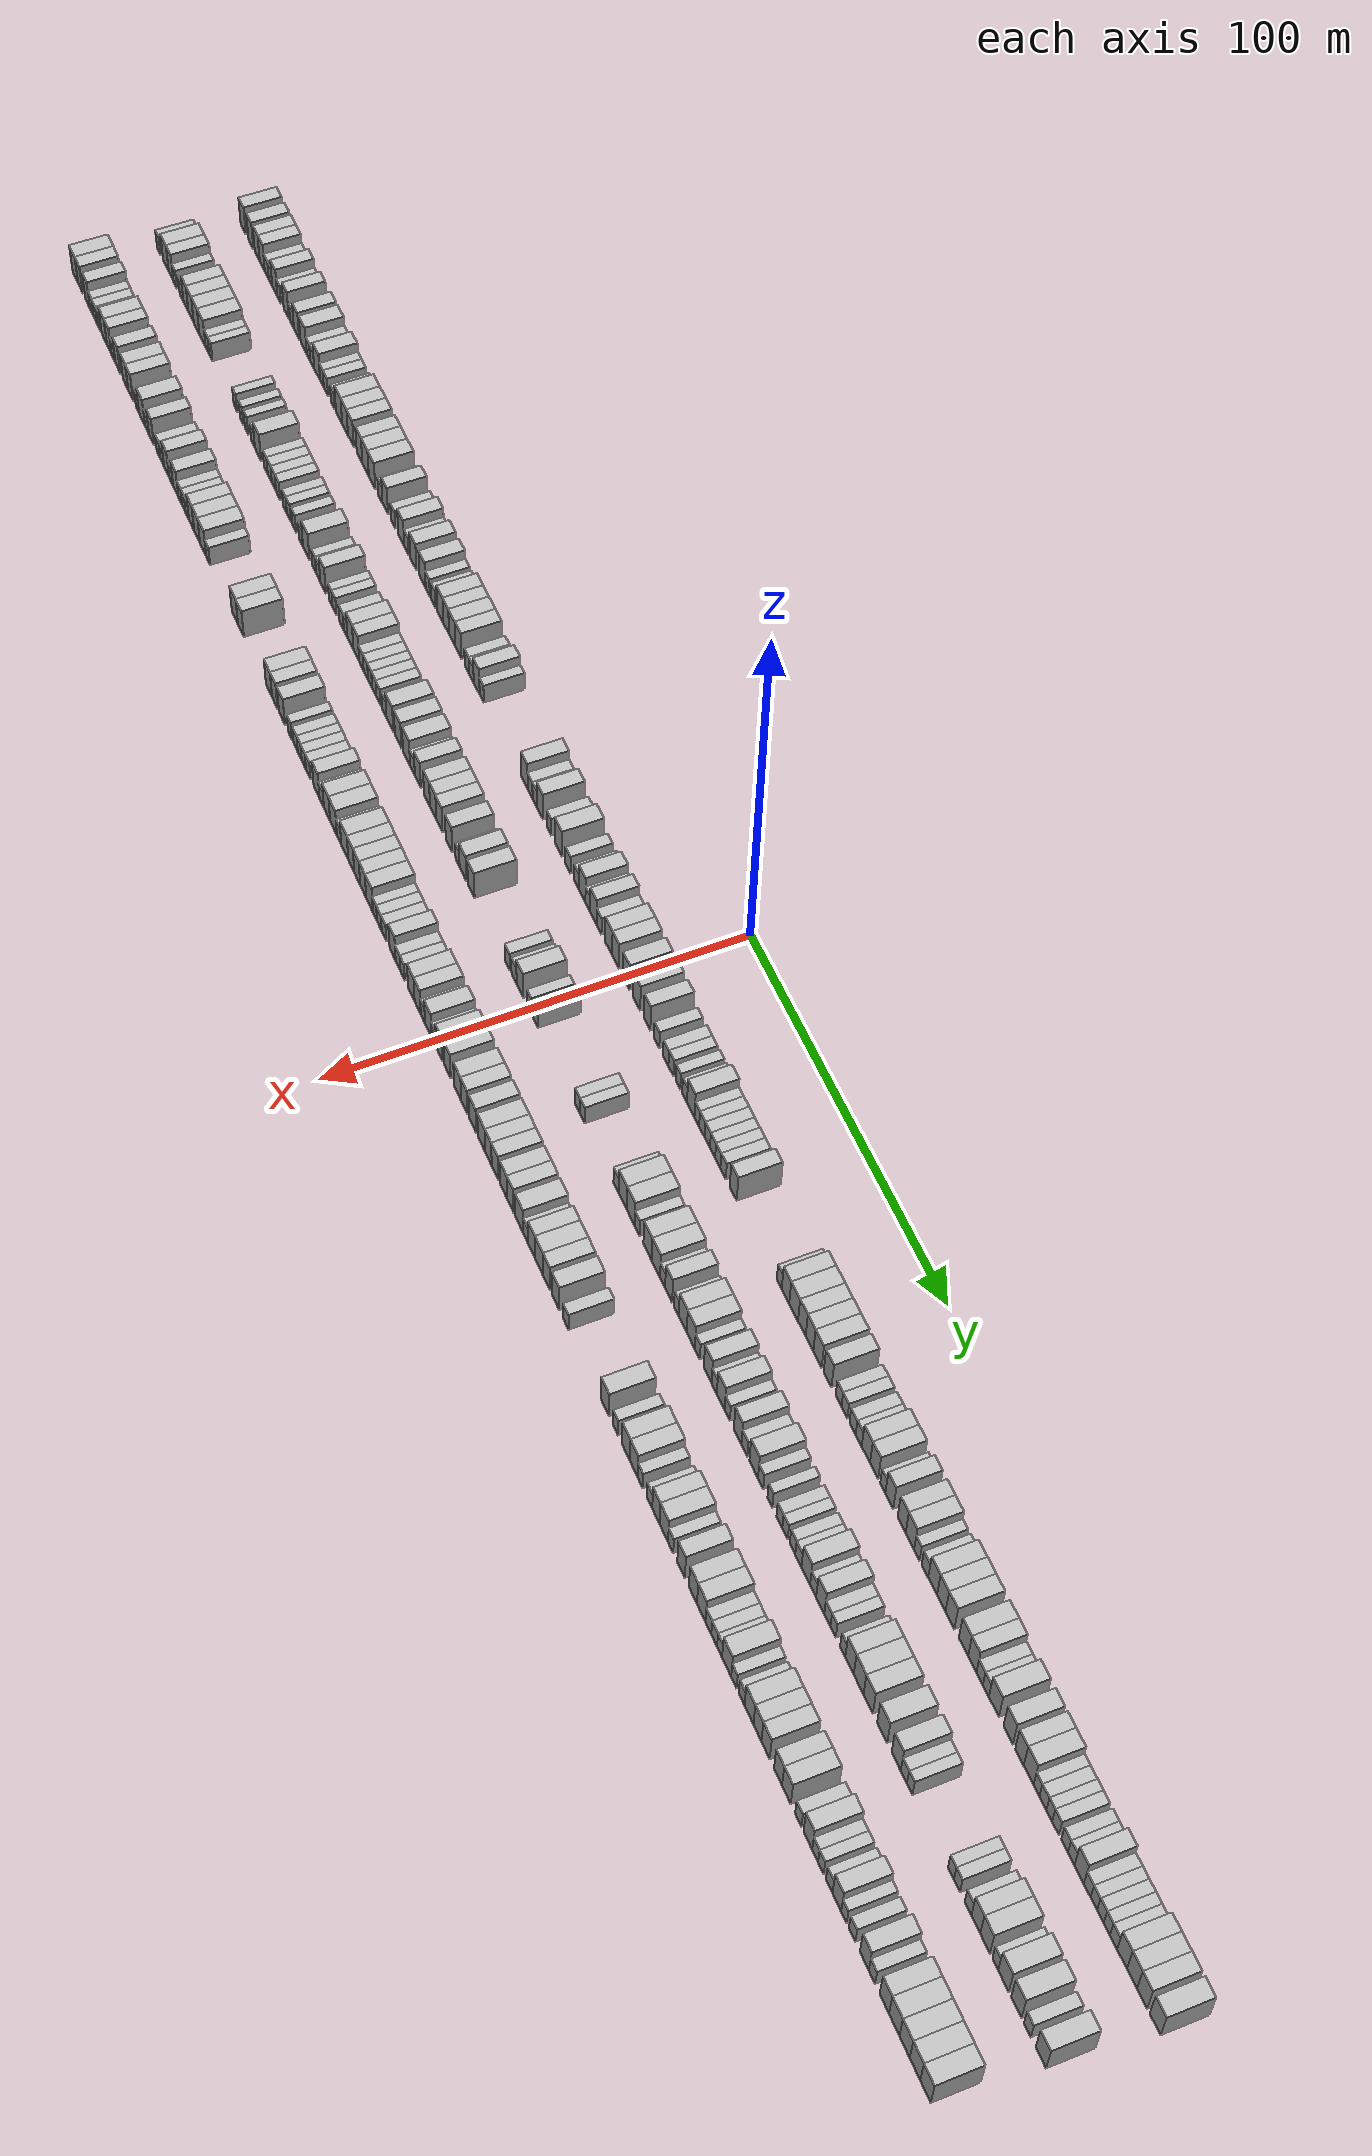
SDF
<sdf version="1.6">
 <world name="default">
  <scene>
   <sky><clouds><speed>12</speed></clouds></sky>
   <ambient>0.4 0.4 0.4 1</ambient>
   <background>0.7 0.7 0.7 1</background>
   <shadows>1</shadows>
  </scene>
  <gravity>0 0 -9.8066</gravity>
  <magnetic_field>6e-06 2.3e-05 -4.2e-05</magnetic_field>
  <physics default="0" name="default_physics" type="ode">
   <ode>
    <solver>
     <type>quick</type>
     <iters>10</iters>
     <sor>1.0</sor>
     <use_dynamic_moi_rescaling>0</use_dynamic_moi_rescaling>
    </solver>
    <constraints>
     <cfm>0</cfm>
     <erp>0.2</erp>
     <contact_max_correcting_vel>100</contact_max_correcting_vel>
     <contact_surface_layer>0.001</contact_surface_layer>
    </constraints>
   </ode>
   <max_step_size>0.004</max_step_size>
   <real_time_factor>1</real_time_factor>
   <real_time_update_rate>250</real_time_update_rate>
  </physics>
  <light name="sun" type="directional">
   <pose>0 0 10 0 0 0</pose>
   <diffuse>0.8 0.8 0.8 1</diffuse>
   <specular>0.2 0.2 0.2 1</specular>
   <attenuation>
    <range>1000</range>
    <constant>0.9</constant>
    <linear>0.01</linear>
    <quadratic>0.001</quadratic>
   </attenuation>
   <direction>-0.5 0.1 -0.9</direction>
  </light>
  <model name="building_1">
   <static>1</static>
   <pose>25.0000 -246.0928 0 0.000000 0.000000 0.000000</pose>
   <link name="link">
    <pose>0 0 4.50 0 0 0</pose>
    <collision name="collision"><geometry><box><size>10.0000 3.8145 9.0000</size></box></geometry></collision>
    <visual name="visual">
     <cast_shadows>0</cast_shadows>
     <geometry><box><size>10.0000 3.8145 9.0000</size></box></geometry>
     <material>
      <script>
       <uri>model://HANNAS_wall/materials/scripts</uri>
       <uri>model://HANNAS_wall/materials/textures</uri>
       <name>vrc/HANNAS_wall</name>
      </script>
     </material>
    </visual>
   </link>
  </model>
  <model name="building_2">
   <static>1</static>
   <pose>25.0000 -240.3374 0 0.000000 0.000000 0.000000</pose>
   <link name="link">
    <pose>0 0 4.50 0 0 0</pose>
    <collision name="collision"><geometry><box><size>10.0000 3.6962 9.0000</size></box></geometry></collision>
    <visual name="visual">
     <cast_shadows>0</cast_shadows>
     <geometry><box><size>10.0000 3.6962 9.0000</size></box></geometry>
     <material>
      <script>
       <uri>model://HANNAS_wall/materials/scripts</uri>
       <uri>model://HANNAS_wall/materials/textures</uri>
       <name>vrc/HANNAS_wall</name>
      </script>
     </material>
    </visual>
   </link>
  </model>
  <model name="building_3">
   <static>1</static>
   <pose>25.0000 -235.6657 0 0.000000 0.000000 0.000000</pose>
   <link name="link">
    <pose>0 0 4.50 0 0 0</pose>
    <collision name="collision"><geometry><box><size>10.0000 3.6471 9.0000</size></box></geometry></collision>
    <visual name="visual">
     <cast_shadows>0</cast_shadows>
     <geometry><box><size>10.0000 3.6471 9.0000</size></box></geometry>
     <material>
      <script>
       <uri>model://HANNAS_wall/materials/scripts</uri>
       <uri>model://HANNAS_wall/materials/textures</uri>
       <name>vrc/HANNAS_wall</name>
      </script>
     </material>
    </visual>
   </link>
  </model>
  <model name="building_4">
   <static>1</static>
   <pose>25.0000 -232.0111 0 0.000000 0.000000 0.000000</pose>
   <link name="link">
    <pose>0 0 4.50 0 0 0</pose>
    <collision name="collision"><geometry><box><size>10.0000 3.6621 9.0000</size></box></geometry></collision>
    <visual name="visual">
     <cast_shadows>0</cast_shadows>
     <geometry><box><size>10.0000 3.6621 9.0000</size></box></geometry>
     <material>
      <script>
       <uri>model://HANNAS_wall/materials/scripts</uri>
       <uri>model://HANNAS_wall/materials/textures</uri>
       <name>vrc/HANNAS_wall</name>
      </script>
     </material>
    </visual>
   </link>
  </model>
  <model name="building_5">
   <static>1</static>
   <pose>25.0000 -228.7073 0 0.000000 0.000000 0.000000</pose>
   <link name="link">
    <pose>0 0 3.00 0 0 0</pose>
    <collision name="collision"><geometry><box><size>10.0000 2.9455 6.0000</size></box></geometry></collision>
    <visual name="visual">
     <cast_shadows>0</cast_shadows>
     <geometry><box><size>10.0000 2.9455 6.0000</size></box></geometry>
     <material>
      <script>
       <uri>model://HANNAS_wall/materials/scripts</uri>
       <uri>model://HANNAS_wall/materials/textures</uri>
       <name>vrc/HANNAS_wall</name>
      </script>
     </material>
    </visual>
   </link>
  </model>
  <model name="building_6">
   <static>1</static>
   <pose>25.0000 -225.9592 0 0.000000 0.000000 0.000000</pose>
   <link name="link">
    <pose>0 0 3.00 0 0 0</pose>
    <collision name="collision"><geometry><box><size>10.0000 2.5508 6.0000</size></box></geometry></collision>
    <visual name="visual">
     <cast_shadows>0</cast_shadows>
     <geometry><box><size>10.0000 2.5508 6.0000</size></box></geometry>
     <material>
      <script>
       <uri>model://HANNAS_wall/materials/scripts</uri>
       <uri>model://HANNAS_wall/materials/textures</uri>
       <name>vrc/HANNAS_wall</name>
      </script>
     </material>
    </visual>
   </link>
  </model>
  <model name="building_7">
   <static>1</static>
   <pose>25.0000 -222.8356 0 0.000000 0.000000 0.000000</pose>
   <link name="link">
    <pose>0 0 4.50 0 0 0</pose>
    <collision name="collision"><geometry><box><size>10.0000 3.6965 9.0000</size></box></geometry></collision>
    <visual name="visual">
     <cast_shadows>0</cast_shadows>
     <geometry><box><size>10.0000 3.6965 9.0000</size></box></geometry>
     <material>
      <script>
       <uri>model://HANNAS_wall/materials/scripts</uri>
       <uri>model://HANNAS_wall/materials/textures</uri>
       <name>vrc/HANNAS_wall</name>
      </script>
     </material>
    </visual>
   </link>
  </model>
  <model name="building_8">
   <static>1</static>
   <pose>25.0000 -219.6797 0 0.000000 0.000000 0.000000</pose>
   <link name="link">
    <pose>0 0 3.00 0 0 0</pose>
    <collision name="collision"><geometry><box><size>10.0000 2.6153 6.0000</size></box></geometry></collision>
    <visual name="visual">
     <cast_shadows>0</cast_shadows>
     <geometry><box><size>10.0000 2.6153 6.0000</size></box></geometry>
     <material>
      <script>
       <uri>model://HANNAS_wall/materials/scripts</uri>
       <uri>model://HANNAS_wall/materials/textures</uri>
       <name>vrc/HANNAS_wall</name>
      </script>
     </material>
    </visual>
   </link>
  </model>
  <model name="building_9">
   <static>1</static>
   <pose>25.0000 -214.5535 0 0.000000 0.000000 0.000000</pose>
   <link name="link">
    <pose>0 0 4.50 0 0 0</pose>
    <collision name="collision"><geometry><box><size>10.0000 3.6370 9.0000</size></box></geometry></collision>
    <visual name="visual">
     <cast_shadows>0</cast_shadows>
     <geometry><box><size>10.0000 3.6370 9.0000</size></box></geometry>
     <material>
      <script>
       <uri>model://HANNAS_wall/materials/scripts</uri>
       <uri>model://HANNAS_wall/materials/textures</uri>
       <name>vrc/HANNAS_wall</name>
      </script>
     </material>
    </visual>
   </link>
  </model>
  <model name="building_10">
   <static>1</static>
   <pose>25.0000 -210.3671 0 0.000000 0.000000 0.000000</pose>
   <link name="link">
    <pose>0 0 3.00 0 0 0</pose>
    <collision name="collision"><geometry><box><size>10.0000 2.7357 6.0000</size></box></geometry></collision>
    <visual name="visual">
     <cast_shadows>0</cast_shadows>
     <geometry><box><size>10.0000 2.7357 6.0000</size></box></geometry>
     <material>
      <script>
       <uri>model://HANNAS_wall/materials/scripts</uri>
       <uri>model://HANNAS_wall/materials/textures</uri>
       <name>vrc/HANNAS_wall</name>
      </script>
     </material>
    </visual>
   </link>
  </model>
  <model name="building_11">
   <static>1</static>
   <pose>25.0000 -207.1221 0 0.000000 0.000000 0.000000</pose>
   <link name="link">
    <pose>0 0 4.50 0 0 0</pose>
    <collision name="collision"><geometry><box><size>10.0000 3.7543 9.0000</size></box></geometry></collision>
    <visual name="visual">
     <cast_shadows>0</cast_shadows>
     <geometry><box><size>10.0000 3.7543 9.0000</size></box></geometry>
     <material>
      <script>
       <uri>model://HANNAS_wall/materials/scripts</uri>
       <uri>model://HANNAS_wall/materials/textures</uri>
       <name>vrc/HANNAS_wall</name>
      </script>
     </material>
    </visual>
   </link>
  </model>
  <model name="building_12">
   <static>1</static>
   <pose>25.0000 -202.0649 0 0.000000 0.000000 0.000000</pose>
   <link name="link">
    <pose>0 0 4.50 0 0 0</pose>
    <collision name="collision"><geometry><box><size>10.0000 4.3602 9.0000</size></box></geometry></collision>
    <visual name="visual">
     <cast_shadows>0</cast_shadows>
     <geometry><box><size>10.0000 4.3602 9.0000</size></box></geometry>
     <material>
      <script>
       <uri>model://HANNAS_wall/materials/scripts</uri>
       <uri>model://HANNAS_wall/materials/textures</uri>
       <name>vrc/HANNAS_wall</name>
      </script>
     </material>
    </visual>
   </link>
  </model>
  <model name="building_13">
   <static>1</static>
   <pose>25.0000 -198.6433 0 0.000000 0.000000 0.000000</pose>
   <link name="link">
    <pose>0 0 3.00 0 0 0</pose>
    <collision name="collision"><geometry><box><size>10.0000 2.4829 6.0000</size></box></geometry></collision>
    <visual name="visual">
     <cast_shadows>0</cast_shadows>
     <geometry><box><size>10.0000 2.4829 6.0000</size></box></geometry>
     <material>
      <script>
       <uri>model://HANNAS_wall/materials/scripts</uri>
       <uri>model://HANNAS_wall/materials/textures</uri>
       <name>vrc/HANNAS_wall</name>
      </script>
     </material>
    </visual>
   </link>
  </model>
  <model name="building_14">
   <static>1</static>
   <pose>25.0000 -195.9856 0 0.000000 0.000000 0.000000</pose>
   <link name="link">
    <pose>0 0 3.00 0 0 0</pose>
    <collision name="collision"><geometry><box><size>10.0000 2.8325 6.0000</size></box></geometry></collision>
    <visual name="visual">
     <cast_shadows>0</cast_shadows>
     <geometry><box><size>10.0000 2.8325 6.0000</size></box></geometry>
     <material>
      <script>
       <uri>model://HANNAS_wall/materials/scripts</uri>
       <uri>model://HANNAS_wall/materials/textures</uri>
       <name>vrc/HANNAS_wall</name>
      </script>
     </material>
    </visual>
   </link>
  </model>
  <model name="building_15">
   <static>1</static>
   <pose>25.0000 -192.4904 0 0.000000 0.000000 0.000000</pose>
   <link name="link">
    <pose>0 0 4.50 0 0 0</pose>
    <collision name="collision"><geometry><box><size>10.0000 4.1579 9.0000</size></box></geometry></collision>
    <visual name="visual">
     <cast_shadows>0</cast_shadows>
     <geometry><box><size>10.0000 4.1579 9.0000</size></box></geometry>
     <material>
      <script>
       <uri>model://HANNAS_wall/materials/scripts</uri>
       <uri>model://HANNAS_wall/materials/textures</uri>
       <name>vrc/HANNAS_wall</name>
      </script>
     </material>
    </visual>
   </link>
  </model>
  <model name="building_16">
   <static>1</static>
   <pose>25.0000 -189.1389 0 0.000000 0.000000 0.000000</pose>
   <link name="link">
    <pose>0 0 3.00 0 0 0</pose>
    <collision name="collision"><geometry><box><size>10.0000 2.5451 6.0000</size></box></geometry></collision>
    <visual name="visual">
     <cast_shadows>0</cast_shadows>
     <geometry><box><size>10.0000 2.5451 6.0000</size></box></geometry>
     <material>
      <script>
       <uri>model://HANNAS_wall/materials/scripts</uri>
       <uri>model://HANNAS_wall/materials/textures</uri>
       <name>vrc/HANNAS_wall</name>
      </script>
     </material>
    </visual>
   </link>
  </model>
  <model name="building_17">
   <static>1</static>
   <pose>25.0000 -186.3680 0 0.000000 0.000000 0.000000</pose>
   <link name="link">
    <pose>0 0 3.00 0 0 0</pose>
    <collision name="collision"><geometry><box><size>10.0000 2.9968 6.0000</size></box></geometry></collision>
    <visual name="visual">
     <cast_shadows>0</cast_shadows>
     <geometry><box><size>10.0000 2.9968 6.0000</size></box></geometry>
     <material>
      <script>
       <uri>model://HANNAS_wall/materials/scripts</uri>
       <uri>model://HANNAS_wall/materials/textures</uri>
       <name>vrc/HANNAS_wall</name>
      </script>
     </material>
    </visual>
   </link>
  </model>
  <model name="building_18">
   <static>1</static>
   <pose>25.0000 -181.6189 0 0.000000 0.000000 0.000000</pose>
   <link name="link">
    <pose>0 0 3.00 0 0 0</pose>
    <collision name="collision"><geometry><box><size>10.0000 2.5014 6.0000</size></box></geometry></collision>
    <visual name="visual">
     <cast_shadows>0</cast_shadows>
     <geometry><box><size>10.0000 2.5014 6.0000</size></box></geometry>
     <material>
      <script>
       <uri>model://HANNAS_wall/materials/scripts</uri>
       <uri>model://HANNAS_wall/materials/textures</uri>
       <name>vrc/HANNAS_wall</name>
      </script>
     </material>
    </visual>
   </link>
  </model>
  <model name="building_19">
   <static>1</static>
   <pose>25.0000 -177.2330 0 0.000000 0.000000 0.000000</pose>
   <link name="link">
    <pose>0 0 4.50 0 0 0</pose>
    <collision name="collision"><geometry><box><size>10.0000 4.2704 9.0000</size></box></geometry></collision>
    <visual name="visual">
     <cast_shadows>0</cast_shadows>
     <geometry><box><size>10.0000 4.2704 9.0000</size></box></geometry>
     <material>
      <script>
       <uri>model://HANNAS_wall/materials/scripts</uri>
       <uri>model://HANNAS_wall/materials/textures</uri>
       <name>vrc/HANNAS_wall</name>
      </script>
     </material>
    </visual>
   </link>
  </model>
  <model name="building_20">
   <static>1</static>
   <pose>25.0000 -173.0918 0 0.000000 0.000000 0.000000</pose>
   <link name="link">
    <pose>0 0 4.50 0 0 0</pose>
    <collision name="collision"><geometry><box><size>10.0000 4.0120 9.0000</size></box></geometry></collision>
    <visual name="visual">
     <cast_shadows>0</cast_shadows>
     <geometry><box><size>10.0000 4.0120 9.0000</size></box></geometry>
     <material>
      <script>
       <uri>model://HANNAS_wall/materials/scripts</uri>
       <uri>model://HANNAS_wall/materials/textures</uri>
       <name>vrc/HANNAS_wall</name>
      </script>
     </material>
    </visual>
   </link>
  </model>
  <model name="building_21">
   <static>1</static>
   <pose>25.0000 -169.0898 0 0.000000 0.000000 0.000000</pose>
   <link name="link">
    <pose>0 0 4.50 0 0 0</pose>
    <collision name="collision"><geometry><box><size>10.0000 3.9919 9.0000</size></box></geometry></collision>
    <visual name="visual">
     <cast_shadows>0</cast_shadows>
     <geometry><box><size>10.0000 3.9919 9.0000</size></box></geometry>
     <material>
      <script>
       <uri>model://HANNAS_wall/materials/scripts</uri>
       <uri>model://HANNAS_wall/materials/textures</uri>
       <name>vrc/HANNAS_wall</name>
      </script>
     </material>
    </visual>
   </link>
  </model>
  <model name="building_22">
   <static>1</static>
   <pose>25.0000 -163.1748 0 0.000000 0.000000 0.000000</pose>
   <link name="link">
    <pose>0 0 4.50 0 0 0</pose>
    <collision name="collision"><geometry><box><size>10.0000 3.8382 9.0000</size></box></geometry></collision>
    <visual name="visual">
     <cast_shadows>0</cast_shadows>
     <geometry><box><size>10.0000 3.8382 9.0000</size></box></geometry>
     <material>
      <script>
       <uri>model://HANNAS_wall/materials/scripts</uri>
       <uri>model://HANNAS_wall/materials/textures</uri>
       <name>vrc/HANNAS_wall</name>
      </script>
     </material>
    </visual>
   </link>
  </model>
  <model name="building_23">
   <static>1</static>
   <pose>25.0000 -159.0883 0 0.000000 0.000000 0.000000</pose>
   <link name="link">
    <pose>0 0 4.50 0 0 0</pose>
    <collision name="collision"><geometry><box><size>10.0000 4.3348 9.0000</size></box></geometry></collision>
    <visual name="visual">
     <cast_shadows>0</cast_shadows>
     <geometry><box><size>10.0000 4.3348 9.0000</size></box></geometry>
     <material>
      <script>
       <uri>model://HANNAS_wall/materials/scripts</uri>
       <uri>model://HANNAS_wall/materials/textures</uri>
       <name>vrc/HANNAS_wall</name>
      </script>
     </material>
    </visual>
   </link>
  </model>
  <model name="building_24">
   <static>1</static>
   <pose>25.0000 -154.7398 0 0.000000 0.000000 0.000000</pose>
   <link name="link">
    <pose>0 0 4.50 0 0 0</pose>
    <collision name="collision"><geometry><box><size>10.0000 4.3622 9.0000</size></box></geometry></collision>
    <visual name="visual">
     <cast_shadows>0</cast_shadows>
     <geometry><box><size>10.0000 4.3622 9.0000</size></box></geometry>
     <material>
      <script>
       <uri>model://HANNAS_wall/materials/scripts</uri>
       <uri>model://HANNAS_wall/materials/textures</uri>
       <name>vrc/HANNAS_wall</name>
      </script>
     </material>
    </visual>
   </link>
  </model>
  <model name="building_25">
   <static>1</static>
   <pose>25.0000 -149.1673 0 0.000000 0.000000 0.000000</pose>
   <link name="link">
    <pose>0 0 3.00 0 0 0</pose>
    <collision name="collision"><geometry><box><size>10.0000 2.7828 6.0000</size></box></geometry></collision>
    <visual name="visual">
     <cast_shadows>0</cast_shadows>
     <geometry><box><size>10.0000 2.7828 6.0000</size></box></geometry>
     <material>
      <script>
       <uri>model://HANNAS_wall/materials/scripts</uri>
       <uri>model://HANNAS_wall/materials/textures</uri>
       <name>vrc/HANNAS_wall</name>
      </script>
     </material>
    </visual>
   </link>
  </model>
  <model name="building_26">
   <static>1</static>
   <pose>25.0000 -145.9105 0 0.000000 0.000000 0.000000</pose>
   <link name="link">
    <pose>0 0 4.50 0 0 0</pose>
    <collision name="collision"><geometry><box><size>10.0000 3.7306 9.0000</size></box></geometry></collision>
    <visual name="visual">
     <cast_shadows>0</cast_shadows>
     <geometry><box><size>10.0000 3.7306 9.0000</size></box></geometry>
     <material>
      <script>
       <uri>model://HANNAS_wall/materials/scripts</uri>
       <uri>model://HANNAS_wall/materials/textures</uri>
       <name>vrc/HANNAS_wall</name>
      </script>
     </material>
    </visual>
   </link>
  </model>
  <model name="building_27">
   <static>1</static>
   <pose>25.0000 -140.6263 0 0.000000 0.000000 0.000000</pose>
   <link name="link">
    <pose>0 0 3.00 0 0 0</pose>
    <collision name="collision"><geometry><box><size>10.0000 2.8379 6.0000</size></box></geometry></collision>
    <visual name="visual">
     <cast_shadows>0</cast_shadows>
     <geometry><box><size>10.0000 2.8379 6.0000</size></box></geometry>
     <material>
      <script>
       <uri>model://HANNAS_wall/materials/scripts</uri>
       <uri>model://HANNAS_wall/materials/textures</uri>
       <name>vrc/HANNAS_wall</name>
      </script>
     </material>
    </visual>
   </link>
  </model>
  <model name="building_28">
   <static>1</static>
   <pose>25.0000 -135.2350 0 0.000000 0.000000 0.000000</pose>
   <link name="link">
    <pose>0 0 4.50 0 0 0</pose>
    <collision name="collision"><geometry><box><size>10.0000 3.9448 9.0000</size></box></geometry></collision>
    <visual name="visual">
     <cast_shadows>0</cast_shadows>
     <geometry><box><size>10.0000 3.9448 9.0000</size></box></geometry>
     <material>
      <script>
       <uri>model://HANNAS_wall/materials/scripts</uri>
       <uri>model://HANNAS_wall/materials/textures</uri>
       <name>vrc/HANNAS_wall</name>
      </script>
     </material>
    </visual>
   </link>
  </model>
  <model name="building_29">
   <static>1</static>
   <pose>25.0000 -131.8254 0 0.000000 0.000000 0.000000</pose>
   <link name="link">
    <pose>0 0 3.00 0 0 0</pose>
    <collision name="collision"><geometry><box><size>10.0000 2.8742 6.0000</size></box></geometry></collision>
    <visual name="visual">
     <cast_shadows>0</cast_shadows>
     <geometry><box><size>10.0000 2.8742 6.0000</size></box></geometry>
     <material>
      <script>
       <uri>model://HANNAS_wall/materials/scripts</uri>
       <uri>model://HANNAS_wall/materials/textures</uri>
       <name>vrc/HANNAS_wall</name>
      </script>
     </material>
    </visual>
   </link>
  </model>
  <model name="building_30">
   <static>1</static>
   <pose>25.0000 -127.3607 0 0.000000 0.000000 0.000000</pose>
   <link name="link">
    <pose>0 0 4.50 0 0 0</pose>
    <collision name="collision"><geometry><box><size>10.0000 4.0552 9.0000</size></box></geometry></collision>
    <visual name="visual">
     <cast_shadows>0</cast_shadows>
     <geometry><box><size>10.0000 4.0552 9.0000</size></box></geometry>
     <material>
      <script>
       <uri>model://HANNAS_wall/materials/scripts</uri>
       <uri>model://HANNAS_wall/materials/textures</uri>
       <name>vrc/HANNAS_wall</name>
      </script>
     </material>
    </visual>
   </link>
  </model>
  <model name="building_31">
   <static>1</static>
   <pose>25.0000 -121.3324 0 0.000000 0.000000 0.000000</pose>
   <link name="link">
    <pose>0 0 4.50 0 0 0</pose>
    <collision name="collision"><geometry><box><size>10.0000 4.0013 9.0000</size></box></geometry></collision>
    <visual name="visual">
     <cast_shadows>0</cast_shadows>
     <geometry><box><size>10.0000 4.0013 9.0000</size></box></geometry>
     <material>
      <script>
       <uri>model://HANNAS_wall/materials/scripts</uri>
       <uri>model://HANNAS_wall/materials/textures</uri>
       <name>vrc/HANNAS_wall</name>
      </script>
     </material>
    </visual>
   </link>
  </model>
  <model name="building_32">
   <static>1</static>
   <pose>25.0000 -117.9784 0 0.000000 0.000000 0.000000</pose>
   <link name="link">
    <pose>0 0 3.00 0 0 0</pose>
    <collision name="collision"><geometry><box><size>10.0000 2.7067 6.0000</size></box></geometry></collision>
    <visual name="visual">
     <cast_shadows>0</cast_shadows>
     <geometry><box><size>10.0000 2.7067 6.0000</size></box></geometry>
     <material>
      <script>
       <uri>model://HANNAS_wall/materials/scripts</uri>
       <uri>model://HANNAS_wall/materials/textures</uri>
       <name>vrc/HANNAS_wall</name>
      </script>
     </material>
    </visual>
   </link>
  </model>
  <model name="building_33">
   <static>1</static>
   <pose>25.0000 -114.2575 0 0.000000 0.000000 0.000000</pose>
   <link name="link">
    <pose>0 0 3.00 0 0 0</pose>
    <collision name="collision"><geometry><box><size>10.0000 2.7352 6.0000</size></box></geometry></collision>
    <visual name="visual">
     <cast_shadows>0</cast_shadows>
     <geometry><box><size>10.0000 2.7352 6.0000</size></box></geometry>
     <material>
      <script>
       <uri>model://HANNAS_wall/materials/scripts</uri>
       <uri>model://HANNAS_wall/materials/textures</uri>
       <name>vrc/HANNAS_wall</name>
      </script>
     </material>
    </visual>
   </link>
  </model>
  <model name="building_34">
   <static>1</static>
   <pose>25.0000 -109.9211 0 0.000000 0.000000 0.000000</pose>
   <link name="link">
    <pose>0 0 4.50 0 0 0</pose>
    <collision name="collision"><geometry><box><size>10.0000 3.9376 9.0000</size></box></geometry></collision>
    <visual name="visual">
     <cast_shadows>0</cast_shadows>
     <geometry><box><size>10.0000 3.9376 9.0000</size></box></geometry>
     <material>
      <script>
       <uri>model://HANNAS_wall/materials/scripts</uri>
       <uri>model://HANNAS_wall/materials/textures</uri>
       <name>vrc/HANNAS_wall</name>
      </script>
     </material>
    </visual>
   </link>
  </model>
  <model name="building_35">
   <static>1</static>
   <pose>25.0000 -106.1404 0 0.000000 0.000000 0.000000</pose>
   <link name="link">
    <pose>0 0 4.50 0 0 0</pose>
    <collision name="collision"><geometry><box><size>10.0000 3.6238 9.0000</size></box></geometry></collision>
    <visual name="visual">
     <cast_shadows>0</cast_shadows>
     <geometry><box><size>10.0000 3.6238 9.0000</size></box></geometry>
     <material>
      <script>
       <uri>model://HANNAS_wall/materials/scripts</uri>
       <uri>model://HANNAS_wall/materials/textures</uri>
       <name>vrc/HANNAS_wall</name>
      </script>
     </material>
    </visual>
   </link>
  </model>
  <model name="building_36">
   <static>1</static>
   <pose>25.0000 -102.3017 0 0.000000 0.000000 0.000000</pose>
   <link name="link">
    <pose>0 0 4.50 0 0 0</pose>
    <collision name="collision"><geometry><box><size>10.0000 4.0537 9.0000</size></box></geometry></collision>
    <visual name="visual">
     <cast_shadows>0</cast_shadows>
     <geometry><box><size>10.0000 4.0537 9.0000</size></box></geometry>
     <material>
      <script>
       <uri>model://HANNAS_wall/materials/scripts</uri>
       <uri>model://HANNAS_wall/materials/textures</uri>
       <name>vrc/HANNAS_wall</name>
      </script>
     </material>
    </visual>
   </link>
  </model>
  <model name="building_37">
   <static>1</static>
   <pose>25.0000 -98.3519 0 0.000000 0.000000 0.000000</pose>
   <link name="link">
    <pose>0 0 4.50 0 0 0</pose>
    <collision name="collision"><geometry><box><size>10.0000 3.8459 9.0000</size></box></geometry></collision>
    <visual name="visual">
     <cast_shadows>0</cast_shadows>
     <geometry><box><size>10.0000 3.8459 9.0000</size></box></geometry>
     <material>
      <script>
       <uri>model://HANNAS_wall/materials/scripts</uri>
       <uri>model://HANNAS_wall/materials/textures</uri>
       <name>vrc/HANNAS_wall</name>
      </script>
     </material>
    </visual>
   </link>
  </model>
  <model name="building_38">
   <static>1</static>
   <pose>25.0000 -93.0518 0 0.000000 0.000000 0.000000</pose>
   <link name="link">
    <pose>0 0 3.00 0 0 0</pose>
    <collision name="collision"><geometry><box><size>10.0000 2.7543 6.0000</size></box></geometry></collision>
    <visual name="visual">
     <cast_shadows>0</cast_shadows>
     <geometry><box><size>10.0000 2.7543 6.0000</size></box></geometry>
     <material>
      <script>
       <uri>model://HANNAS_wall/materials/scripts</uri>
       <uri>model://HANNAS_wall/materials/textures</uri>
       <name>vrc/HANNAS_wall</name>
      </script>
     </material>
    </visual>
   </link>
  </model>
  <model name="building_39">
   <static>1</static>
   <pose>25.0000 -90.2512 0 0.000000 0.000000 0.000000</pose>
   <link name="link">
    <pose>0 0 3.00 0 0 0</pose>
    <collision name="collision"><geometry><box><size>10.0000 2.8469 6.0000</size></box></geometry></collision>
    <visual name="visual">
     <cast_shadows>0</cast_shadows>
     <geometry><box><size>10.0000 2.8469 6.0000</size></box></geometry>
     <material>
      <script>
       <uri>model://HANNAS_wall/materials/scripts</uri>
       <uri>model://HANNAS_wall/materials/textures</uri>
       <name>vrc/HANNAS_wall</name>
      </script>
     </material>
    </visual>
   </link>
  </model>
  <model name="building_40">
   <static>1</static>
   <pose>25.0000 -86.9753 0 0.000000 0.000000 0.000000</pose>
   <link name="link">
    <pose>0 0 4.50 0 0 0</pose>
    <collision name="collision"><geometry><box><size>10.0000 3.7048 9.0000</size></box></geometry></collision>
    <visual name="visual">
     <cast_shadows>0</cast_shadows>
     <geometry><box><size>10.0000 3.7048 9.0000</size></box></geometry>
     <material>
      <script>
       <uri>model://HANNAS_wall/materials/scripts</uri>
       <uri>model://HANNAS_wall/materials/textures</uri>
       <name>vrc/HANNAS_wall</name>
      </script>
     </material>
    </visual>
   </link>
  </model>
  <model name="building_41">
   <static>1</static>
   <pose>25.0000 -83.8453 0 0.000000 0.000000 0.000000</pose>
   <link name="link">
    <pose>0 0 3.00 0 0 0</pose>
    <collision name="collision"><geometry><box><size>10.0000 2.5552 6.0000</size></box></geometry></collision>
    <visual name="visual">
     <cast_shadows>0</cast_shadows>
     <geometry><box><size>10.0000 2.5552 6.0000</size></box></geometry>
     <material>
      <script>
       <uri>model://HANNAS_wall/materials/scripts</uri>
       <uri>model://HANNAS_wall/materials/textures</uri>
       <name>vrc/HANNAS_wall</name>
      </script>
     </material>
    </visual>
   </link>
  </model>
  <model name="building_42">
   <static>1</static>
   <pose>25.0000 -57.7793 0 0.000000 0.000000 0.000000</pose>
   <link name="link">
    <pose>0 0 4.50 0 0 0</pose>
    <collision name="collision"><geometry><box><size>10.0000 3.8590 9.0000</size></box></geometry></collision>
    <visual name="visual">
     <cast_shadows>0</cast_shadows>
     <geometry><box><size>10.0000 3.8590 9.0000</size></box></geometry>
     <material>
      <script>
       <uri>model://HANNAS_wall/materials/scripts</uri>
       <uri>model://HANNAS_wall/materials/textures</uri>
       <name>vrc/HANNAS_wall</name>
      </script>
     </material>
    </visual>
   </link>
  </model>
  <model name="building_43">
   <static>1</static>
   <pose>25.0000 -54.3826 0 0.000000 0.000000 0.000000</pose>
   <link name="link">
    <pose>0 0 3.00 0 0 0</pose>
    <collision name="collision"><geometry><box><size>10.0000 2.9344 6.0000</size></box></geometry></collision>
    <visual name="visual">
     <cast_shadows>0</cast_shadows>
     <geometry><box><size>10.0000 2.9344 6.0000</size></box></geometry>
     <material>
      <script>
       <uri>model://HANNAS_wall/materials/scripts</uri>
       <uri>model://HANNAS_wall/materials/textures</uri>
       <name>vrc/HANNAS_wall</name>
      </script>
     </material>
    </visual>
   </link>
  </model>
  <model name="building_44">
   <static>1</static>
   <pose>25.0000 -51.6898 0 0.000000 0.000000 0.000000</pose>
   <link name="link">
    <pose>0 0 3.00 0 0 0</pose>
    <collision name="collision"><geometry><box><size>10.0000 2.4513 6.0000</size></box></geometry></collision>
    <visual name="visual">
     <cast_shadows>0</cast_shadows>
     <geometry><box><size>10.0000 2.4513 6.0000</size></box></geometry>
     <material>
      <script>
       <uri>model://HANNAS_wall/materials/scripts</uri>
       <uri>model://HANNAS_wall/materials/textures</uri>
       <name>vrc/HANNAS_wall</name>
      </script>
     </material>
    </visual>
   </link>
  </model>
  <model name="building_45">
   <static>1</static>
   <pose>25.0000 -48.5208 0 0.000000 0.000000 0.000000</pose>
   <link name="link">
    <pose>0 0 4.50 0 0 0</pose>
    <collision name="collision"><geometry><box><size>10.0000 3.8866 9.0000</size></box></geometry></collision>
    <visual name="visual">
     <cast_shadows>0</cast_shadows>
     <geometry><box><size>10.0000 3.8866 9.0000</size></box></geometry>
     <material>
      <script>
       <uri>model://HANNAS_wall/materials/scripts</uri>
       <uri>model://HANNAS_wall/materials/textures</uri>
       <name>vrc/HANNAS_wall</name>
      </script>
     </material>
    </visual>
   </link>
  </model>
  <model name="building_46">
   <static>1</static>
   <pose>25.0000 -43.2080 0 0.000000 0.000000 0.000000</pose>
   <link name="link">
    <pose>0 0 3.00 0 0 0</pose>
    <collision name="collision"><geometry><box><size>10.0000 2.7390 6.0000</size></box></geometry></collision>
    <visual name="visual">
     <cast_shadows>0</cast_shadows>
     <geometry><box><size>10.0000 2.7390 6.0000</size></box></geometry>
     <material>
      <script>
       <uri>model://HANNAS_wall/materials/scripts</uri>
       <uri>model://HANNAS_wall/materials/textures</uri>
       <name>vrc/HANNAS_wall</name>
      </script>
     </material>
    </visual>
   </link>
  </model>
  <model name="building_47">
   <static>1</static>
   <pose>25.0000 -37.6801 0 0.000000 0.000000 0.000000</pose>
   <link name="link">
    <pose>0 0 4.50 0 0 0</pose>
    <collision name="collision"><geometry><box><size>10.0000 4.3170 9.0000</size></box></geometry></collision>
    <visual name="visual">
     <cast_shadows>0</cast_shadows>
     <geometry><box><size>10.0000 4.3170 9.0000</size></box></geometry>
     <material>
      <script>
       <uri>model://HANNAS_wall/materials/scripts</uri>
       <uri>model://HANNAS_wall/materials/textures</uri>
       <name>vrc/HANNAS_wall</name>
      </script>
     </material>
    </visual>
   </link>
  </model>
  <model name="building_48">
   <static>1</static>
   <pose>25.0000 -32.0281 0 0.000000 0.000000 0.000000</pose>
   <link name="link">
    <pose>0 0 3.00 0 0 0</pose>
    <collision name="collision"><geometry><box><size>10.0000 2.9870 6.0000</size></box></geometry></collision>
    <visual name="visual">
     <cast_shadows>0</cast_shadows>
     <geometry><box><size>10.0000 2.9870 6.0000</size></box></geometry>
     <material>
      <script>
       <uri>model://HANNAS_wall/materials/scripts</uri>
       <uri>model://HANNAS_wall/materials/textures</uri>
       <name>vrc/HANNAS_wall</name>
      </script>
     </material>
    </visual>
   </link>
  </model>
  <model name="building_49">
   <static>1</static>
   <pose>25.0000 -27.1794 0 0.000000 0.000000 0.000000</pose>
   <link name="link">
    <pose>0 0 3.00 0 0 0</pose>
    <collision name="collision"><geometry><box><size>10.0000 2.7104 6.0000</size></box></geometry></collision>
    <visual name="visual">
     <cast_shadows>0</cast_shadows>
     <geometry><box><size>10.0000 2.7104 6.0000</size></box></geometry>
     <material>
      <script>
       <uri>model://HANNAS_wall/materials/scripts</uri>
       <uri>model://HANNAS_wall/materials/textures</uri>
       <name>vrc/HANNAS_wall</name>
      </script>
     </material>
    </visual>
   </link>
  </model>
  <model name="building_50">
   <static>1</static>
   <pose>25.0000 -23.8731 0 0.000000 0.000000 0.000000</pose>
   <link name="link">
    <pose>0 0 4.50 0 0 0</pose>
    <collision name="collision"><geometry><box><size>10.0000 3.9021 9.0000</size></box></geometry></collision>
    <visual name="visual">
     <cast_shadows>0</cast_shadows>
     <geometry><box><size>10.0000 3.9021 9.0000</size></box></geometry>
     <material>
      <script>
       <uri>model://HANNAS_wall/materials/scripts</uri>
       <uri>model://HANNAS_wall/materials/textures</uri>
       <name>vrc/HANNAS_wall</name>
      </script>
     </material>
    </visual>
   </link>
  </model>
  <model name="building_51">
   <static>1</static>
   <pose>25.0000 -20.5506 0 0.000000 0.000000 0.000000</pose>
   <link name="link">
    <pose>0 0 3.00 0 0 0</pose>
    <collision name="collision"><geometry><box><size>10.0000 2.7430 6.0000</size></box></geometry></collision>
    <visual name="visual">
     <cast_shadows>0</cast_shadows>
     <geometry><box><size>10.0000 2.7430 6.0000</size></box></geometry>
     <material>
      <script>
       <uri>model://HANNAS_wall/materials/scripts</uri>
       <uri>model://HANNAS_wall/materials/textures</uri>
       <name>vrc/HANNAS_wall</name>
      </script>
     </material>
    </visual>
   </link>
  </model>
  <model name="building_52">
   <static>1</static>
   <pose>25.0000 -17.3764 0 0.000000 0.000000 0.000000</pose>
   <link name="link">
    <pose>0 0 4.50 0 0 0</pose>
    <collision name="collision"><geometry><box><size>10.0000 3.6055 9.0000</size></box></geometry></collision>
    <visual name="visual">
     <cast_shadows>0</cast_shadows>
     <geometry><box><size>10.0000 3.6055 9.0000</size></box></geometry>
     <material>
      <script>
       <uri>model://HANNAS_wall/materials/scripts</uri>
       <uri>model://HANNAS_wall/materials/textures</uri>
       <name>vrc/HANNAS_wall</name>
      </script>
     </material>
    </visual>
   </link>
  </model>
  <model name="building_53">
   <static>1</static>
   <pose>25.0000 -14.1619 0 0.000000 0.000000 0.000000</pose>
   <link name="link">
    <pose>0 0 3.00 0 0 0</pose>
    <collision name="collision"><geometry><box><size>10.0000 2.8235 6.0000</size></box></geometry></collision>
    <visual name="visual">
     <cast_shadows>0</cast_shadows>
     <geometry><box><size>10.0000 2.8235 6.0000</size></box></geometry>
     <material>
      <script>
       <uri>model://HANNAS_wall/materials/scripts</uri>
       <uri>model://HANNAS_wall/materials/textures</uri>
       <name>vrc/HANNAS_wall</name>
      </script>
     </material>
    </visual>
   </link>
  </model>
  <model name="building_54">
   <static>1</static>
   <pose>25.0000 -8.7398 0 0.000000 0.000000 0.000000</pose>
   <link name="link">
    <pose>0 0 4.50 0 0 0</pose>
    <collision name="collision"><geometry><box><size>10.0000 4.0207 9.0000</size></box></geometry></collision>
    <visual name="visual">
     <cast_shadows>0</cast_shadows>
     <geometry><box><size>10.0000 4.0207 9.0000</size></box></geometry>
     <material>
      <script>
       <uri>model://HANNAS_wall/materials/scripts</uri>
       <uri>model://HANNAS_wall/materials/textures</uri>
       <name>vrc/HANNAS_wall</name>
      </script>
     </material>
    </visual>
   </link>
  </model>
  <model name="building_55">
   <static>1</static>
   <pose>25.0000 -4.8081 0 0.000000 0.000000 0.000000</pose>
   <link name="link">
    <pose>0 0 4.50 0 0 0</pose>
    <collision name="collision"><geometry><box><size>10.0000 3.8428 9.0000</size></box></geometry></collision>
    <visual name="visual">
     <cast_shadows>0</cast_shadows>
     <geometry><box><size>10.0000 3.8428 9.0000</size></box></geometry>
     <material>
      <script>
       <uri>model://HANNAS_wall/materials/scripts</uri>
       <uri>model://HANNAS_wall/materials/textures</uri>
       <name>vrc/HANNAS_wall</name>
      </script>
     </material>
    </visual>
   </link>
  </model>
  <model name="building_56">
   <static>1</static>
   <pose>25.0000 1.0844 0 0.000000 0.000000 0.000000</pose>
   <link name="link">
    <pose>0 0 4.50 0 0 0</pose>
    <collision name="collision"><geometry><box><size>10.0000 3.9421 9.0000</size></box></geometry></collision>
    <visual name="visual">
     <cast_shadows>0</cast_shadows>
     <geometry><box><size>10.0000 3.9421 9.0000</size></box></geometry>
     <material>
      <script>
       <uri>model://HANNAS_wall/materials/scripts</uri>
       <uri>model://HANNAS_wall/materials/textures</uri>
       <name>vrc/HANNAS_wall</name>
      </script>
     </material>
    </visual>
   </link>
  </model>
  <model name="building_57">
   <static>1</static>
   <pose>25.0000 7.0039 0 0.000000 0.000000 0.000000</pose>
   <link name="link">
    <pose>0 0 4.50 0 0 0</pose>
    <collision name="collision"><geometry><box><size>10.0000 3.8968 9.0000</size></box></geometry></collision>
    <visual name="visual">
     <cast_shadows>0</cast_shadows>
     <geometry><box><size>10.0000 3.8968 9.0000</size></box></geometry>
     <material>
      <script>
       <uri>model://HANNAS_wall/materials/scripts</uri>
       <uri>model://HANNAS_wall/materials/textures</uri>
       <name>vrc/HANNAS_wall</name>
      </script>
     </material>
    </visual>
   </link>
  </model>
  <model name="building_58">
   <static>1</static>
   <pose>25.0000 12.7543 0 0.000000 0.000000 0.000000</pose>
   <link name="link">
    <pose>0 0 4.50 0 0 0</pose>
    <collision name="collision"><geometry><box><size>10.0000 3.6041 9.0000</size></box></geometry></collision>
    <visual name="visual">
     <cast_shadows>0</cast_shadows>
     <geometry><box><size>10.0000 3.6041 9.0000</size></box></geometry>
     <material>
      <script>
       <uri>model://HANNAS_wall/materials/scripts</uri>
       <uri>model://HANNAS_wall/materials/textures</uri>
       <name>vrc/HANNAS_wall</name>
      </script>
     </material>
    </visual>
   </link>
  </model>
  <model name="building_59">
   <static>1</static>
   <pose>25.0000 18.0167 0 0.000000 0.000000 0.000000</pose>
   <link name="link">
    <pose>0 0 3.00 0 0 0</pose>
    <collision name="collision"><geometry><box><size>10.0000 2.9206 6.0000</size></box></geometry></collision>
    <visual name="visual">
     <cast_shadows>0</cast_shadows>
     <geometry><box><size>10.0000 2.9206 6.0000</size></box></geometry>
     <material>
      <script>
       <uri>model://HANNAS_wall/materials/scripts</uri>
       <uri>model://HANNAS_wall/materials/textures</uri>
       <name>vrc/HANNAS_wall</name>
      </script>
     </material>
    </visual>
   </link>
  </model>
  <model name="building_60">
   <static>1</static>
   <pose>25.0000 22.9509 0 0.000000 0.000000 0.000000</pose>
   <link name="link">
    <pose>0 0 3.00 0 0 0</pose>
    <collision name="collision"><geometry><box><size>10.0000 2.9479 6.0000</size></box></geometry></collision>
    <visual name="visual">
     <cast_shadows>0</cast_shadows>
     <geometry><box><size>10.0000 2.9479 6.0000</size></box></geometry>
     <material>
      <script>
       <uri>model://HANNAS_wall/materials/scripts</uri>
       <uri>model://HANNAS_wall/materials/textures</uri>
       <name>vrc/HANNAS_wall</name>
      </script>
     </material>
    </visual>
   </link>
  </model>
  <model name="building_61">
   <static>1</static>
   <pose>25.0000 25.8441 0 0.000000 0.000000 0.000000</pose>
   <link name="link">
    <pose>0 0 3.00 0 0 0</pose>
    <collision name="collision"><geometry><box><size>10.0000 2.8384 6.0000</size></box></geometry></collision>
    <visual name="visual">
     <cast_shadows>0</cast_shadows>
     <geometry><box><size>10.0000 2.8384 6.0000</size></box></geometry>
     <material>
      <script>
       <uri>model://HANNAS_wall/materials/scripts</uri>
       <uri>model://HANNAS_wall/materials/textures</uri>
       <name>vrc/HANNAS_wall</name>
      </script>
     </material>
    </visual>
   </link>
  </model>
  <model name="building_62">
   <static>1</static>
   <pose>25.0000 29.5517 0 0.000000 0.000000 0.000000</pose>
   <link name="link">
    <pose>0 0 3.00 0 0 0</pose>
    <collision name="collision"><geometry><box><size>10.0000 2.5768 6.0000</size></box></geometry></collision>
    <visual name="visual">
     <cast_shadows>0</cast_shadows>
     <geometry><box><size>10.0000 2.5768 6.0000</size></box></geometry>
     <material>
      <script>
       <uri>model://HANNAS_wall/materials/scripts</uri>
       <uri>model://HANNAS_wall/materials/textures</uri>
       <name>vrc/HANNAS_wall</name>
      </script>
     </material>
    </visual>
   </link>
  </model>
  <model name="building_63">
   <static>1</static>
   <pose>25.0000 33.1496 0 0.000000 0.000000 0.000000</pose>
   <link name="link">
    <pose>0 0 3.00 0 0 0</pose>
    <collision name="collision"><geometry><box><size>10.0000 2.6190 6.0000</size></box></geometry></collision>
    <visual name="visual">
     <cast_shadows>0</cast_shadows>
     <geometry><box><size>10.0000 2.6190 6.0000</size></box></geometry>
     <material>
      <script>
       <uri>model://HANNAS_wall/materials/scripts</uri>
       <uri>model://HANNAS_wall/materials/textures</uri>
       <name>vrc/HANNAS_wall</name>
      </script>
     </material>
    </visual>
   </link>
  </model>
  <model name="building_64">
   <static>1</static>
   <pose>25.0000 36.4508 0 0.000000 0.000000 0.000000</pose>
   <link name="link">
    <pose>0 0 4.50 0 0 0</pose>
    <collision name="collision"><geometry><box><size>10.0000 3.9833 9.0000</size></box></geometry></collision>
    <visual name="visual">
     <cast_shadows>0</cast_shadows>
     <geometry><box><size>10.0000 3.9833 9.0000</size></box></geometry>
     <material>
      <script>
       <uri>model://HANNAS_wall/materials/scripts</uri>
       <uri>model://HANNAS_wall/materials/textures</uri>
       <name>vrc/HANNAS_wall</name>
      </script>
     </material>
    </visual>
   </link>
  </model>
  <model name="building_65">
   <static>1</static>
   <pose>25.0000 39.6901 0 0.000000 0.000000 0.000000</pose>
   <link name="link">
    <pose>0 0 3.00 0 0 0</pose>
    <collision name="collision"><geometry><box><size>10.0000 2.4955 6.0000</size></box></geometry></collision>
    <visual name="visual">
     <cast_shadows>0</cast_shadows>
     <geometry><box><size>10.0000 2.4955 6.0000</size></box></geometry>
     <material>
      <script>
       <uri>model://HANNAS_wall/materials/scripts</uri>
       <uri>model://HANNAS_wall/materials/textures</uri>
       <name>vrc/HANNAS_wall</name>
      </script>
     </material>
    </visual>
   </link>
  </model>
  <model name="building_66">
   <static>1</static>
   <pose>25.0000 42.3571 0 0.000000 0.000000 0.000000</pose>
   <link name="link">
    <pose>0 0 3.00 0 0 0</pose>
    <collision name="collision"><geometry><box><size>10.0000 2.8384 6.0000</size></box></geometry></collision>
    <visual name="visual">
     <cast_shadows>0</cast_shadows>
     <geometry><box><size>10.0000 2.8384 6.0000</size></box></geometry>
     <material>
      <script>
       <uri>model://HANNAS_wall/materials/scripts</uri>
       <uri>model://HANNAS_wall/materials/textures</uri>
       <name>vrc/HANNAS_wall</name>
      </script>
     </material>
    </visual>
   </link>
  </model>
  <model name="building_67">
   <static>1</static>
   <pose>25.0000 45.2196 0 0.000000 0.000000 0.000000</pose>
   <link name="link">
    <pose>0 0 3.00 0 0 0</pose>
    <collision name="collision"><geometry><box><size>10.0000 2.8865 6.0000</size></box></geometry></collision>
    <visual name="visual">
     <cast_shadows>0</cast_shadows>
     <geometry><box><size>10.0000 2.8865 6.0000</size></box></geometry>
     <material>
      <script>
       <uri>model://HANNAS_wall/materials/scripts</uri>
       <uri>model://HANNAS_wall/materials/textures</uri>
       <name>vrc/HANNAS_wall</name>
      </script>
     </material>
    </visual>
   </link>
  </model>
  <model name="building_68">
   <static>1</static>
   <pose>25.0000 48.0282 0 0.000000 0.000000 0.000000</pose>
   <link name="link">
    <pose>0 0 3.00 0 0 0</pose>
    <collision name="collision"><geometry><box><size>10.0000 2.7308 6.0000</size></box></geometry></collision>
    <visual name="visual">
     <cast_shadows>0</cast_shadows>
     <geometry><box><size>10.0000 2.7308 6.0000</size></box></geometry>
     <material>
      <script>
       <uri>model://HANNAS_wall/materials/scripts</uri>
       <uri>model://HANNAS_wall/materials/textures</uri>
       <name>vrc/HANNAS_wall</name>
      </script>
     </material>
    </visual>
   </link>
  </model>
  <model name="building_69">
   <static>1</static>
   <pose>25.0000 50.7630 0 0.000000 0.000000 0.000000</pose>
   <link name="link">
    <pose>0 0 3.00 0 0 0</pose>
    <collision name="collision"><geometry><box><size>10.0000 2.7389 6.0000</size></box></geometry></collision>
    <visual name="visual">
     <cast_shadows>0</cast_shadows>
     <geometry><box><size>10.0000 2.7389 6.0000</size></box></geometry>
     <material>
      <script>
       <uri>model://HANNAS_wall/materials/scripts</uri>
       <uri>model://HANNAS_wall/materials/textures</uri>
       <name>vrc/HANNAS_wall</name>
      </script>
     </material>
    </visual>
   </link>
  </model>
  <model name="building_70">
   <static>1</static>
   <pose>25.0000 53.5651 0 0.000000 0.000000 0.000000</pose>
   <link name="link">
    <pose>0 0 3.00 0 0 0</pose>
    <collision name="collision"><geometry><box><size>10.0000 2.8652 6.0000</size></box></geometry></collision>
    <visual name="visual">
     <cast_shadows>0</cast_shadows>
     <geometry><box><size>10.0000 2.8652 6.0000</size></box></geometry>
     <material>
      <script>
       <uri>model://HANNAS_wall/materials/scripts</uri>
       <uri>model://HANNAS_wall/materials/textures</uri>
       <name>vrc/HANNAS_wall</name>
      </script>
     </material>
    </visual>
   </link>
  </model>
  <model name="building_71">
   <static>1</static>
   <pose>25.0000 58.8334 0 0.000000 0.000000 0.000000</pose>
   <link name="link">
    <pose>0 0 4.50 0 0 0</pose>
    <collision name="collision"><geometry><box><size>10.0000 3.6714 9.0000</size></box></geometry></collision>
    <visual name="visual">
     <cast_shadows>0</cast_shadows>
     <geometry><box><size>10.0000 3.6714 9.0000</size></box></geometry>
     <material>
      <script>
       <uri>model://HANNAS_wall/materials/scripts</uri>
       <uri>model://HANNAS_wall/materials/textures</uri>
       <name>vrc/HANNAS_wall</name>
      </script>
     </material>
    </visual>
   </link>
  </model>
  <model name="building_72">
   <static>1</static>
   <pose>25.0000 82.3290 0 0.000000 0.000000 0.000000</pose>
   <link name="link">
    <pose>0 0 3.00 0 0 0</pose>
    <collision name="collision"><geometry><box><size>10.0000 2.4400 6.0000</size></box></geometry></collision>
    <visual name="visual">
     <cast_shadows>0</cast_shadows>
     <geometry><box><size>10.0000 2.4400 6.0000</size></box></geometry>
     <material>
      <script>
       <uri>model://HANNAS_wall/materials/scripts</uri>
       <uri>model://HANNAS_wall/materials/textures</uri>
       <name>vrc/HANNAS_wall</name>
      </script>
     </material>
    </visual>
   </link>
  </model>
  <model name="building_73">
   <static>1</static>
   <pose>25.0000 85.4345 0 0.000000 0.000000 0.000000</pose>
   <link name="link">
    <pose>0 0 4.50 0 0 0</pose>
    <collision name="collision"><geometry><box><size>10.0000 3.7710 9.0000</size></box></geometry></collision>
    <visual name="visual">
     <cast_shadows>0</cast_shadows>
     <geometry><box><size>10.0000 3.7710 9.0000</size></box></geometry>
     <material>
      <script>
       <uri>model://HANNAS_wall/materials/scripts</uri>
       <uri>model://HANNAS_wall/materials/textures</uri>
       <name>vrc/HANNAS_wall</name>
      </script>
     </material>
    </visual>
   </link>
  </model>
  <model name="building_74">
   <static>1</static>
   <pose>25.0000 89.5214 0 0.000000 0.000000 0.000000</pose>
   <link name="link">
    <pose>0 0 4.50 0 0 0</pose>
    <collision name="collision"><geometry><box><size>10.0000 4.4029 9.0000</size></box></geometry></collision>
    <visual name="visual">
     <cast_shadows>0</cast_shadows>
     <geometry><box><size>10.0000 4.4029 9.0000</size></box></geometry>
     <material>
      <script>
       <uri>model://HANNAS_wall/materials/scripts</uri>
       <uri>model://HANNAS_wall/materials/textures</uri>
       <name>vrc/HANNAS_wall</name>
      </script>
     </material>
    </visual>
   </link>
  </model>
  <model name="building_75">
   <static>1</static>
   <pose>25.0000 93.6102 0 0.000000 0.000000 0.000000</pose>
   <link name="link">
    <pose>0 0 4.50 0 0 0</pose>
    <collision name="collision"><geometry><box><size>10.0000 3.7746 9.0000</size></box></geometry></collision>
    <visual name="visual">
     <cast_shadows>0</cast_shadows>
     <geometry><box><size>10.0000 3.7746 9.0000</size></box></geometry>
     <material>
      <script>
       <uri>model://HANNAS_wall/materials/scripts</uri>
       <uri>model://HANNAS_wall/materials/textures</uri>
       <name>vrc/HANNAS_wall</name>
      </script>
     </material>
    </visual>
   </link>
  </model>
  <model name="building_76">
   <static>1</static>
   <pose>25.0000 97.4006 0 0.000000 0.000000 0.000000</pose>
   <link name="link">
    <pose>0 0 4.50 0 0 0</pose>
    <collision name="collision"><geometry><box><size>10.0000 3.8063 9.0000</size></box></geometry></collision>
    <visual name="visual">
     <cast_shadows>0</cast_shadows>
     <geometry><box><size>10.0000 3.8063 9.0000</size></box></geometry>
     <material>
      <script>
       <uri>model://HANNAS_wall/materials/scripts</uri>
       <uri>model://HANNAS_wall/materials/textures</uri>
       <name>vrc/HANNAS_wall</name>
      </script>
     </material>
    </visual>
   </link>
  </model>
  <model name="building_77">
   <static>1</static>
   <pose>25.0000 101.3333 0 0.000000 0.000000 0.000000</pose>
   <link name="link">
    <pose>0 0 4.50 0 0 0</pose>
    <collision name="collision"><geometry><box><size>10.0000 4.0591 9.0000</size></box></geometry></collision>
    <visual name="visual">
     <cast_shadows>0</cast_shadows>
     <geometry><box><size>10.0000 4.0591 9.0000</size></box></geometry>
     <material>
      <script>
       <uri>model://HANNAS_wall/materials/scripts</uri>
       <uri>model://HANNAS_wall/materials/textures</uri>
       <name>vrc/HANNAS_wall</name>
      </script>
     </material>
    </visual>
   </link>
  </model>
  <model name="building_78">
   <static>1</static>
   <pose>25.0000 106.2716 0 0.000000 0.000000 0.000000</pose>
   <link name="link">
    <pose>0 0 4.50 0 0 0</pose>
    <collision name="collision"><geometry><box><size>10.0000 3.8176 9.0000</size></box></geometry></collision>
    <visual name="visual">
     <cast_shadows>0</cast_shadows>
     <geometry><box><size>10.0000 3.8176 9.0000</size></box></geometry>
     <material>
      <script>
       <uri>model://HANNAS_wall/materials/scripts</uri>
       <uri>model://HANNAS_wall/materials/textures</uri>
       <name>vrc/HANNAS_wall</name>
      </script>
     </material>
    </visual>
   </link>
  </model>
  <model name="building_79">
   <static>1</static>
   <pose>25.0000 111.5950 0 0.000000 0.000000 0.000000</pose>
   <link name="link">
    <pose>0 0 3.00 0 0 0</pose>
    <collision name="collision"><geometry><box><size>10.0000 2.8292 6.0000</size></box></geometry></collision>
    <visual name="visual">
     <cast_shadows>0</cast_shadows>
     <geometry><box><size>10.0000 2.8292 6.0000</size></box></geometry>
     <material>
      <script>
       <uri>model://HANNAS_wall/materials/scripts</uri>
       <uri>model://HANNAS_wall/materials/textures</uri>
       <name>vrc/HANNAS_wall</name>
      </script>
     </material>
    </visual>
   </link>
  </model>
  <model name="building_80">
   <static>1</static>
   <pose>25.0000 114.4292 0 0.000000 0.000000 0.000000</pose>
   <link name="link">
    <pose>0 0 3.00 0 0 0</pose>
    <collision name="collision"><geometry><box><size>10.0000 2.8391 6.0000</size></box></geometry></collision>
    <visual name="visual">
     <cast_shadows>0</cast_shadows>
     <geometry><box><size>10.0000 2.8391 6.0000</size></box></geometry>
     <material>
      <script>
       <uri>model://HANNAS_wall/materials/scripts</uri>
       <uri>model://HANNAS_wall/materials/textures</uri>
       <name>vrc/HANNAS_wall</name>
      </script>
     </material>
    </visual>
   </link>
  </model>
  <model name="building_81">
   <static>1</static>
   <pose>25.0000 118.3393 0 0.000000 0.000000 0.000000</pose>
   <link name="link">
    <pose>0 0 3.00 0 0 0</pose>
    <collision name="collision"><geometry><box><size>10.0000 2.9811 6.0000</size></box></geometry></collision>
    <visual name="visual">
     <cast_shadows>0</cast_shadows>
     <geometry><box><size>10.0000 2.9811 6.0000</size></box></geometry>
     <material>
      <script>
       <uri>model://HANNAS_wall/materials/scripts</uri>
       <uri>model://HANNAS_wall/materials/textures</uri>
       <name>vrc/HANNAS_wall</name>
      </script>
     </material>
    </visual>
   </link>
  </model>
  <model name="building_82">
   <static>1</static>
   <pose>25.0000 121.2665 0 0.000000 0.000000 0.000000</pose>
   <link name="link">
    <pose>0 0 3.00 0 0 0</pose>
    <collision name="collision"><geometry><box><size>10.0000 2.8732 6.0000</size></box></geometry></collision>
    <visual name="visual">
     <cast_shadows>0</cast_shadows>
     <geometry><box><size>10.0000 2.8732 6.0000</size></box></geometry>
     <material>
      <script>
       <uri>model://HANNAS_wall/materials/scripts</uri>
       <uri>model://HANNAS_wall/materials/textures</uri>
       <name>vrc/HANNAS_wall</name>
      </script>
     </material>
    </visual>
   </link>
  </model>
  <model name="building_83">
   <static>1</static>
   <pose>25.0000 124.6743 0 0.000000 0.000000 0.000000</pose>
   <link name="link">
    <pose>0 0 4.50 0 0 0</pose>
    <collision name="collision"><geometry><box><size>10.0000 3.9424 9.0000</size></box></geometry></collision>
    <visual name="visual">
     <cast_shadows>0</cast_shadows>
     <geometry><box><size>10.0000 3.9424 9.0000</size></box></geometry>
     <material>
      <script>
       <uri>model://HANNAS_wall/materials/scripts</uri>
       <uri>model://HANNAS_wall/materials/textures</uri>
       <name>vrc/HANNAS_wall</name>
      </script>
     </material>
    </visual>
   </link>
  </model>
  <model name="building_84">
   <static>1</static>
   <pose>25.0000 128.5680 0 0.000000 0.000000 0.000000</pose>
   <link name="link">
    <pose>0 0 4.50 0 0 0</pose>
    <collision name="collision"><geometry><box><size>10.0000 3.8451 9.0000</size></box></geometry></collision>
    <visual name="visual">
     <cast_shadows>0</cast_shadows>
     <geometry><box><size>10.0000 3.8451 9.0000</size></box></geometry>
     <material>
      <script>
       <uri>model://HANNAS_wall/materials/scripts</uri>
       <uri>model://HANNAS_wall/materials/textures</uri>
       <name>vrc/HANNAS_wall</name>
      </script>
     </material>
    </visual>
   </link>
  </model>
  <model name="building_85">
   <static>1</static>
   <pose>25.0000 132.7024 0 0.000000 0.000000 0.000000</pose>
   <link name="link">
    <pose>0 0 3.00 0 0 0</pose>
    <collision name="collision"><geometry><box><size>10.0000 2.4239 6.0000</size></box></geometry></collision>
    <visual name="visual">
     <cast_shadows>0</cast_shadows>
     <geometry><box><size>10.0000 2.4239 6.0000</size></box></geometry>
     <material>
      <script>
       <uri>model://HANNAS_wall/materials/scripts</uri>
       <uri>model://HANNAS_wall/materials/textures</uri>
       <name>vrc/HANNAS_wall</name>
      </script>
     </material>
    </visual>
   </link>
  </model>
  <model name="building_86">
   <static>1</static>
   <pose>25.0000 135.7550 0 0.000000 0.000000 0.000000</pose>
   <link name="link">
    <pose>0 0 4.50 0 0 0</pose>
    <collision name="collision"><geometry><box><size>10.0000 3.6813 9.0000</size></box></geometry></collision>
    <visual name="visual">
     <cast_shadows>0</cast_shadows>
     <geometry><box><size>10.0000 3.6813 9.0000</size></box></geometry>
     <material>
      <script>
       <uri>model://HANNAS_wall/materials/scripts</uri>
       <uri>model://HANNAS_wall/materials/textures</uri>
       <name>vrc/HANNAS_wall</name>
      </script>
     </material>
    </visual>
   </link>
  </model>
  <model name="building_87">
   <static>1</static>
   <pose>25.0000 141.4812 0 0.000000 0.000000 0.000000</pose>
   <link name="link">
    <pose>0 0 4.50 0 0 0</pose>
    <collision name="collision"><geometry><box><size>10.0000 3.7710 9.0000</size></box></geometry></collision>
    <visual name="visual">
     <cast_shadows>0</cast_shadows>
     <geometry><box><size>10.0000 3.7710 9.0000</size></box></geometry>
     <material>
      <script>
       <uri>model://HANNAS_wall/materials/scripts</uri>
       <uri>model://HANNAS_wall/materials/textures</uri>
       <name>vrc/HANNAS_wall</name>
      </script>
     </material>
    </visual>
   </link>
  </model>
  <model name="building_88">
   <static>1</static>
   <pose>25.0000 145.3287 0 0.000000 0.000000 0.000000</pose>
   <link name="link">
    <pose>0 0 4.50 0 0 0</pose>
    <collision name="collision"><geometry><box><size>10.0000 3.9241 9.0000</size></box></geometry></collision>
    <visual name="visual">
     <cast_shadows>0</cast_shadows>
     <geometry><box><size>10.0000 3.9241 9.0000</size></box></geometry>
     <material>
      <script>
       <uri>model://HANNAS_wall/materials/scripts</uri>
       <uri>model://HANNAS_wall/materials/textures</uri>
       <name>vrc/HANNAS_wall</name>
      </script>
     </material>
    </visual>
   </link>
  </model>
  <model name="building_89">
   <static>1</static>
   <pose>25.0000 148.5356 0 0.000000 0.000000 0.000000</pose>
   <link name="link">
    <pose>0 0 3.00 0 0 0</pose>
    <collision name="collision"><geometry><box><size>10.0000 2.4896 6.0000</size></box></geometry></collision>
    <visual name="visual">
     <cast_shadows>0</cast_shadows>
     <geometry><box><size>10.0000 2.4896 6.0000</size></box></geometry>
     <material>
      <script>
       <uri>model://HANNAS_wall/materials/scripts</uri>
       <uri>model://HANNAS_wall/materials/textures</uri>
       <name>vrc/HANNAS_wall</name>
      </script>
     </material>
    </visual>
   </link>
  </model>
  <model name="building_90">
   <static>1</static>
   <pose>25.0000 152.2532 0 0.000000 0.000000 0.000000</pose>
   <link name="link">
    <pose>0 0 3.00 0 0 0</pose>
    <collision name="collision"><geometry><box><size>10.0000 2.9456 6.0000</size></box></geometry></collision>
    <visual name="visual">
     <cast_shadows>0</cast_shadows>
     <geometry><box><size>10.0000 2.9456 6.0000</size></box></geometry>
     <material>
      <script>
       <uri>model://HANNAS_wall/materials/scripts</uri>
       <uri>model://HANNAS_wall/materials/textures</uri>
       <name>vrc/HANNAS_wall</name>
      </script>
     </material>
    </visual>
   </link>
  </model>
  <model name="building_91">
   <static>1</static>
   <pose>25.0000 155.7516 0 0.000000 0.000000 0.000000</pose>
   <link name="link">
    <pose>0 0 4.50 0 0 0</pose>
    <collision name="collision"><geometry><box><size>10.0000 4.0513 9.0000</size></box></geometry></collision>
    <visual name="visual">
     <cast_shadows>0</cast_shadows>
     <geometry><box><size>10.0000 4.0513 9.0000</size></box></geometry>
     <material>
      <script>
       <uri>model://HANNAS_wall/materials/scripts</uri>
       <uri>model://HANNAS_wall/materials/textures</uri>
       <name>vrc/HANNAS_wall</name>
      </script>
     </material>
    </visual>
   </link>
  </model>
  <model name="building_92">
   <static>1</static>
   <pose>25.0000 159.6972 0 0.000000 0.000000 0.000000</pose>
   <link name="link">
    <pose>0 0 4.50 0 0 0</pose>
    <collision name="collision"><geometry><box><size>10.0000 3.8400 9.0000</size></box></geometry></collision>
    <visual name="visual">
     <cast_shadows>0</cast_shadows>
     <geometry><box><size>10.0000 3.8400 9.0000</size></box></geometry>
     <material>
      <script>
       <uri>model://HANNAS_wall/materials/scripts</uri>
       <uri>model://HANNAS_wall/materials/textures</uri>
       <name>vrc/HANNAS_wall</name>
      </script>
     </material>
    </visual>
   </link>
  </model>
  <model name="building_93">
   <static>1</static>
   <pose>25.0000 163.6050 0 0.000000 0.000000 0.000000</pose>
   <link name="link">
    <pose>0 0 4.50 0 0 0</pose>
    <collision name="collision"><geometry><box><size>10.0000 3.9756 9.0000</size></box></geometry></collision>
    <visual name="visual">
     <cast_shadows>0</cast_shadows>
     <geometry><box><size>10.0000 3.9756 9.0000</size></box></geometry>
     <material>
      <script>
       <uri>model://HANNAS_wall/materials/scripts</uri>
       <uri>model://HANNAS_wall/materials/textures</uri>
       <name>vrc/HANNAS_wall</name>
      </script>
     </material>
    </visual>
   </link>
  </model>
  <model name="building_94">
   <static>1</static>
   <pose>25.0000 169.6519 0 0.000000 0.000000 0.000000</pose>
   <link name="link">
    <pose>0 0 4.50 0 0 0</pose>
    <collision name="collision"><geometry><box><size>10.0000 4.1182 9.0000</size></box></geometry></collision>
    <visual name="visual">
     <cast_shadows>0</cast_shadows>
     <geometry><box><size>10.0000 4.1182 9.0000</size></box></geometry>
     <material>
      <script>
       <uri>model://HANNAS_wall/materials/scripts</uri>
       <uri>model://HANNAS_wall/materials/textures</uri>
       <name>vrc/HANNAS_wall</name>
      </script>
     </material>
    </visual>
   </link>
  </model>
  <model name="building_95">
   <static>1</static>
   <pose>25.0000 173.5696 0 0.000000 0.000000 0.000000</pose>
   <link name="link">
    <pose>0 0 4.50 0 0 0</pose>
    <collision name="collision"><geometry><box><size>10.0000 3.7172 9.0000</size></box></geometry></collision>
    <visual name="visual">
     <cast_shadows>0</cast_shadows>
     <geometry><box><size>10.0000 3.7172 9.0000</size></box></geometry>
     <material>
      <script>
       <uri>model://HANNAS_wall/materials/scripts</uri>
       <uri>model://HANNAS_wall/materials/textures</uri>
       <name>vrc/HANNAS_wall</name>
      </script>
     </material>
    </visual>
   </link>
  </model>
  <model name="building_96">
   <static>1</static>
   <pose>25.0000 176.8529 0 0.000000 0.000000 0.000000</pose>
   <link name="link">
    <pose>0 0 3.00 0 0 0</pose>
    <collision name="collision"><geometry><box><size>10.0000 2.8495 6.0000</size></box></geometry></collision>
    <visual name="visual">
     <cast_shadows>0</cast_shadows>
     <geometry><box><size>10.0000 2.8495 6.0000</size></box></geometry>
     <material>
      <script>
       <uri>model://HANNAS_wall/materials/scripts</uri>
       <uri>model://HANNAS_wall/materials/textures</uri>
       <name>vrc/HANNAS_wall</name>
      </script>
     </material>
    </visual>
   </link>
  </model>
  <model name="building_97">
   <static>1</static>
   <pose>25.0000 179.6041 0 0.000000 0.000000 0.000000</pose>
   <link name="link">
    <pose>0 0 3.00 0 0 0</pose>
    <collision name="collision"><geometry><box><size>10.0000 2.6528 6.0000</size></box></geometry></collision>
    <visual name="visual">
     <cast_shadows>0</cast_shadows>
     <geometry><box><size>10.0000 2.6528 6.0000</size></box></geometry>
     <material>
      <script>
       <uri>model://HANNAS_wall/materials/scripts</uri>
       <uri>model://HANNAS_wall/materials/textures</uri>
       <name>vrc/HANNAS_wall</name>
      </script>
     </material>
    </visual>
   </link>
  </model>
  <model name="building_98">
   <static>1</static>
   <pose>25.0000 183.1309 0 0.000000 0.000000 0.000000</pose>
   <link name="link">
    <pose>0 0 4.50 0 0 0</pose>
    <collision name="collision"><geometry><box><size>10.0000 4.4007 9.0000</size></box></geometry></collision>
    <visual name="visual">
     <cast_shadows>0</cast_shadows>
     <geometry><box><size>10.0000 4.4007 9.0000</size></box></geometry>
     <material>
      <script>
       <uri>model://HANNAS_wall/materials/scripts</uri>
       <uri>model://HANNAS_wall/materials/textures</uri>
       <name>vrc/HANNAS_wall</name>
      </script>
     </material>
    </visual>
   </link>
  </model>
  <model name="building_99">
   <static>1</static>
   <pose>25.0000 189.3693 0 0.000000 0.000000 0.000000</pose>
   <link name="link">
    <pose>0 0 4.50 0 0 0</pose>
    <collision name="collision"><geometry><box><size>10.0000 4.0761 9.0000</size></box></geometry></collision>
    <visual name="visual">
     <cast_shadows>0</cast_shadows>
     <geometry><box><size>10.0000 4.0761 9.0000</size></box></geometry>
     <material>
      <script>
       <uri>model://HANNAS_wall/materials/scripts</uri>
       <uri>model://HANNAS_wall/materials/textures</uri>
       <name>vrc/HANNAS_wall</name>
      </script>
     </material>
    </visual>
   </link>
  </model>
  <model name="building_100">
   <static>1</static>
   <pose>25.0000 194.2313 0 0.000000 0.000000 0.000000</pose>
   <link name="link">
    <pose>0 0 4.50 0 0 0</pose>
    <collision name="collision"><geometry><box><size>10.0000 3.6480 9.0000</size></box></geometry></collision>
    <visual name="visual">
     <cast_shadows>0</cast_shadows>
     <geometry><box><size>10.0000 3.6480 9.0000</size></box></geometry>
     <material>
      <script>
       <uri>model://HANNAS_wall/materials/scripts</uri>
       <uri>model://HANNAS_wall/materials/textures</uri>
       <name>vrc/HANNAS_wall</name>
      </script>
     </material>
    </visual>
   </link>
  </model>
  <model name="building_101">
   <static>1</static>
   <pose>25.0000 198.1783 0 0.000000 0.000000 0.000000</pose>
   <link name="link">
    <pose>0 0 4.50 0 0 0</pose>
    <collision name="collision"><geometry><box><size>10.0000 4.2460 9.0000</size></box></geometry></collision>
    <visual name="visual">
     <cast_shadows>0</cast_shadows>
     <geometry><box><size>10.0000 4.2460 9.0000</size></box></geometry>
     <material>
      <script>
       <uri>model://HANNAS_wall/materials/scripts</uri>
       <uri>model://HANNAS_wall/materials/textures</uri>
       <name>vrc/HANNAS_wall</name>
      </script>
     </material>
    </visual>
   </link>
  </model>
  <model name="building_102">
   <static>1</static>
   <pose>25.0000 201.5499 0 0.000000 0.000000 0.000000</pose>
   <link name="link">
    <pose>0 0 3.00 0 0 0</pose>
    <collision name="collision"><geometry><box><size>10.0000 2.4973 6.0000</size></box></geometry></collision>
    <visual name="visual">
     <cast_shadows>0</cast_shadows>
     <geometry><box><size>10.0000 2.4973 6.0000</size></box></geometry>
     <material>
      <script>
       <uri>model://HANNAS_wall/materials/scripts</uri>
       <uri>model://HANNAS_wall/materials/textures</uri>
       <name>vrc/HANNAS_wall</name>
      </script>
     </material>
    </visual>
   </link>
  </model>
  <model name="building_103">
   <static>1</static>
   <pose>25.0000 204.2657 0 0.000000 0.000000 0.000000</pose>
   <link name="link">
    <pose>0 0 3.00 0 0 0</pose>
    <collision name="collision"><geometry><box><size>10.0000 2.9342 6.0000</size></box></geometry></collision>
    <visual name="visual">
     <cast_shadows>0</cast_shadows>
     <geometry><box><size>10.0000 2.9342 6.0000</size></box></geometry>
     <material>
      <script>
       <uri>model://HANNAS_wall/materials/scripts</uri>
       <uri>model://HANNAS_wall/materials/textures</uri>
       <name>vrc/HANNAS_wall</name>
      </script>
     </material>
    </visual>
   </link>
  </model>
  <model name="building_104">
   <static>1</static>
   <pose>25.0000 206.9601 0 0.000000 0.000000 0.000000</pose>
   <link name="link">
    <pose>0 0 3.00 0 0 0</pose>
    <collision name="collision"><geometry><box><size>10.0000 2.4547 6.0000</size></box></geometry></collision>
    <visual name="visual">
     <cast_shadows>0</cast_shadows>
     <geometry><box><size>10.0000 2.4547 6.0000</size></box></geometry>
     <material>
      <script>
       <uri>model://HANNAS_wall/materials/scripts</uri>
       <uri>model://HANNAS_wall/materials/textures</uri>
       <name>vrc/HANNAS_wall</name>
      </script>
     </material>
    </visual>
   </link>
  </model>
  <model name="building_105">
   <static>1</static>
   <pose>25.0000 209.6056 0 0.000000 0.000000 0.000000</pose>
   <link name="link">
    <pose>0 0 3.00 0 0 0</pose>
    <collision name="collision"><geometry><box><size>10.0000 2.8363 6.0000</size></box></geometry></collision>
    <visual name="visual">
     <cast_shadows>0</cast_shadows>
     <geometry><box><size>10.0000 2.8363 6.0000</size></box></geometry>
     <material>
      <script>
       <uri>model://HANNAS_wall/materials/scripts</uri>
       <uri>model://HANNAS_wall/materials/textures</uri>
       <name>vrc/HANNAS_wall</name>
      </script>
     </material>
    </visual>
   </link>
  </model>
  <model name="building_106">
   <static>1</static>
   <pose>25.0000 213.4160 0 0.000000 0.000000 0.000000</pose>
   <link name="link">
    <pose>0 0 3.00 0 0 0</pose>
    <collision name="collision"><geometry><box><size>10.0000 2.7846 6.0000</size></box></geometry></collision>
    <visual name="visual">
     <cast_shadows>0</cast_shadows>
     <geometry><box><size>10.0000 2.7846 6.0000</size></box></geometry>
     <material>
      <script>
       <uri>model://HANNAS_wall/materials/scripts</uri>
       <uri>model://HANNAS_wall/materials/textures</uri>
       <name>vrc/HANNAS_wall</name>
      </script>
     </material>
    </visual>
   </link>
  </model>
  <model name="building_107">
   <static>1</static>
   <pose>25.0000 216.1859 0 0.000000 0.000000 0.000000</pose>
   <link name="link">
    <pose>0 0 3.00 0 0 0</pose>
    <collision name="collision"><geometry><box><size>10.0000 2.7551 6.0000</size></box></geometry></collision>
    <visual name="visual">
     <cast_shadows>0</cast_shadows>
     <geometry><box><size>10.0000 2.7551 6.0000</size></box></geometry>
     <material>
      <script>
       <uri>model://HANNAS_wall/materials/scripts</uri>
       <uri>model://HANNAS_wall/materials/textures</uri>
       <name>vrc/HANNAS_wall</name>
      </script>
     </material>
    </visual>
   </link>
  </model>
  <model name="building_108">
   <static>1</static>
   <pose>25.0000 219.4975 0 0.000000 0.000000 0.000000</pose>
   <link name="link">
    <pose>0 0 4.50 0 0 0</pose>
    <collision name="collision"><geometry><box><size>10.0000 3.8681 9.0000</size></box></geometry></collision>
    <visual name="visual">
     <cast_shadows>0</cast_shadows>
     <geometry><box><size>10.0000 3.8681 9.0000</size></box></geometry>
     <material>
      <script>
       <uri>model://HANNAS_wall/materials/scripts</uri>
       <uri>model://HANNAS_wall/materials/textures</uri>
       <name>vrc/HANNAS_wall</name>
      </script>
     </material>
    </visual>
   </link>
  </model>
  <model name="building_109">
   <static>1</static>
   <pose>25.0000 222.8464 0 0.000000 0.000000 0.000000</pose>
   <link name="link">
    <pose>0 0 3.00 0 0 0</pose>
    <collision name="collision"><geometry><box><size>10.0000 2.8297 6.0000</size></box></geometry></collision>
    <visual name="visual">
     <cast_shadows>0</cast_shadows>
     <geometry><box><size>10.0000 2.8297 6.0000</size></box></geometry>
     <material>
      <script>
       <uri>model://HANNAS_wall/materials/scripts</uri>
       <uri>model://HANNAS_wall/materials/textures</uri>
       <name>vrc/HANNAS_wall</name>
      </script>
     </material>
    </visual>
   </link>
  </model>
  <model name="building_110">
   <static>1</static>
   <pose>25.0000 225.6006 0 0.000000 0.000000 0.000000</pose>
   <link name="link">
    <pose>0 0 3.00 0 0 0</pose>
    <collision name="collision"><geometry><box><size>10.0000 2.6788 6.0000</size></box></geometry></collision>
    <visual name="visual">
     <cast_shadows>0</cast_shadows>
     <geometry><box><size>10.0000 2.6788 6.0000</size></box></geometry>
     <material>
      <script>
       <uri>model://HANNAS_wall/materials/scripts</uri>
       <uri>model://HANNAS_wall/materials/textures</uri>
       <name>vrc/HANNAS_wall</name>
      </script>
     </material>
    </visual>
   </link>
  </model>
  <model name="building_111">
   <static>1</static>
   <pose>25.0000 228.2930 0 0.000000 0.000000 0.000000</pose>
   <link name="link">
    <pose>0 0 3.00 0 0 0</pose>
    <collision name="collision"><geometry><box><size>10.0000 2.7061 6.0000</size></box></geometry></collision>
    <visual name="visual">
     <cast_shadows>0</cast_shadows>
     <geometry><box><size>10.0000 2.7061 6.0000</size></box></geometry>
     <material>
      <script>
       <uri>model://HANNAS_wall/materials/scripts</uri>
       <uri>model://HANNAS_wall/materials/textures</uri>
       <name>vrc/HANNAS_wall</name>
      </script>
     </material>
    </visual>
   </link>
  </model>
  <model name="building_112">
   <static>1</static>
   <pose>25.0000 230.8920 0 0.000000 0.000000 0.000000</pose>
   <link name="link">
    <pose>0 0 3.00 0 0 0</pose>
    <collision name="collision"><geometry><box><size>10.0000 2.4918 6.0000</size></box></geometry></collision>
    <visual name="visual">
     <cast_shadows>0</cast_shadows>
     <geometry><box><size>10.0000 2.4918 6.0000</size></box></geometry>
     <material>
      <script>
       <uri>model://HANNAS_wall/materials/scripts</uri>
       <uri>model://HANNAS_wall/materials/textures</uri>
       <name>vrc/HANNAS_wall</name>
      </script>
     </material>
    </visual>
   </link>
  </model>
  <model name="building_113">
   <static>1</static>
   <pose>25.0000 233.6374 0 0.000000 0.000000 0.000000</pose>
   <link name="link">
    <pose>0 0 3.00 0 0 0</pose>
    <collision name="collision"><geometry><box><size>10.0000 2.9990 6.0000</size></box></geometry></collision>
    <visual name="visual">
     <cast_shadows>0</cast_shadows>
     <geometry><box><size>10.0000 2.9990 6.0000</size></box></geometry>
     <material>
      <script>
       <uri>model://HANNAS_wall/materials/scripts</uri>
       <uri>model://HANNAS_wall/materials/textures</uri>
       <name>vrc/HANNAS_wall</name>
      </script>
     </material>
    </visual>
   </link>
  </model>
  <model name="building_114">
   <static>1</static>
   <pose>25.0000 237.1135 0 0.000000 0.000000 0.000000</pose>
   <link name="link">
    <pose>0 0 4.50 0 0 0</pose>
    <collision name="collision"><geometry><box><size>10.0000 3.9532 9.0000</size></box></geometry></collision>
    <visual name="visual">
     <cast_shadows>0</cast_shadows>
     <geometry><box><size>10.0000 3.9532 9.0000</size></box></geometry>
     <material>
      <script>
       <uri>model://HANNAS_wall/materials/scripts</uri>
       <uri>model://HANNAS_wall/materials/textures</uri>
       <name>vrc/HANNAS_wall</name>
      </script>
     </material>
    </visual>
   </link>
  </model>
  <model name="building_115">
   <static>1</static>
   <pose>25.0000 241.1163 0 0.000000 0.000000 0.000000</pose>
   <link name="link">
    <pose>0 0 4.50 0 0 0</pose>
    <collision name="collision"><geometry><box><size>10.0000 4.0525 9.0000</size></box></geometry></collision>
    <visual name="visual">
     <cast_shadows>0</cast_shadows>
     <geometry><box><size>10.0000 4.0525 9.0000</size></box></geometry>
     <material>
      <script>
       <uri>model://HANNAS_wall/materials/scripts</uri>
       <uri>model://HANNAS_wall/materials/textures</uri>
       <name>vrc/HANNAS_wall</name>
      </script>
     </material>
    </visual>
   </link>
  </model>
  <model name="building_116">
   <static>1</static>
   <pose>25.0000 245.1663 0 0.000000 0.000000 0.000000</pose>
   <link name="link">
    <pose>0 0 4.50 0 0 0</pose>
    <collision name="collision"><geometry><box><size>10.0000 4.0475 9.0000</size></box></geometry></collision>
    <visual name="visual">
     <cast_shadows>0</cast_shadows>
     <geometry><box><size>10.0000 4.0475 9.0000</size></box></geometry>
     <material>
      <script>
       <uri>model://HANNAS_wall/materials/scripts</uri>
       <uri>model://HANNAS_wall/materials/textures</uri>
       <name>vrc/HANNAS_wall</name>
      </script>
     </material>
    </visual>
   </link>
  </model>
  <model name="building_117">
   <static>1</static>
   <pose>25.0000 250.3710 0 0.000000 0.000000 0.000000</pose>
   <link name="link">
    <pose>0 0 4.50 0 0 0</pose>
    <collision name="collision"><geometry><box><size>10.0000 4.3619 9.0000</size></box></geometry></collision>
    <visual name="visual">
     <cast_shadows>0</cast_shadows>
     <geometry><box><size>10.0000 4.3619 9.0000</size></box></geometry>
     <material>
      <script>
       <uri>model://HANNAS_wall/materials/scripts</uri>
       <uri>model://HANNAS_wall/materials/textures</uri>
       <name>vrc/HANNAS_wall</name>
      </script>
     </material>
    </visual>
   </link>
  </model>
  <model name="building_118">
   <static>1</static>
   <pose>47.0000 -246.6379 0 0.000000 0.000000 0.000000</pose>
   <link name="link">
    <pose>0 0 3.00 0 0 0</pose>
    <collision name="collision"><geometry><box><size>10.0000 2.7242 6.0000</size></box></geometry></collision>
    <visual name="visual">
     <cast_shadows>0</cast_shadows>
     <geometry><box><size>10.0000 2.7242 6.0000</size></box></geometry>
     <material>
      <script>
       <uri>model://HANNAS_wall/materials/scripts</uri>
       <uri>model://HANNAS_wall/materials/textures</uri>
       <name>vrc/HANNAS_wall</name>
      </script>
     </material>
    </visual>
   </link>
  </model>
  <model name="building_119">
   <static>1</static>
   <pose>47.0000 -241.1770 0 0.000000 0.000000 0.000000</pose>
   <link name="link">
    <pose>0 0 4.50 0 0 0</pose>
    <collision name="collision"><geometry><box><size>10.0000 4.1976 9.0000</size></box></geometry></collision>
    <visual name="visual">
     <cast_shadows>0</cast_shadows>
     <geometry><box><size>10.0000 4.1976 9.0000</size></box></geometry>
     <material>
      <script>
       <uri>model://HANNAS_wall/materials/scripts</uri>
       <uri>model://HANNAS_wall/materials/textures</uri>
       <name>vrc/HANNAS_wall</name>
      </script>
     </material>
    </visual>
   </link>
  </model>
  <model name="building_120">
   <static>1</static>
   <pose>47.0000 -237.2765 0 0.000000 0.000000 0.000000</pose>
   <link name="link">
    <pose>0 0 4.50 0 0 0</pose>
    <collision name="collision"><geometry><box><size>10.0000 3.6033 9.0000</size></box></geometry></collision>
    <visual name="visual">
     <cast_shadows>0</cast_shadows>
     <geometry><box><size>10.0000 3.6033 9.0000</size></box></geometry>
     <material>
      <script>
       <uri>model://HANNAS_wall/materials/scripts</uri>
       <uri>model://HANNAS_wall/materials/textures</uri>
       <name>vrc/HANNAS_wall</name>
      </script>
     </material>
    </visual>
   </link>
  </model>
  <model name="building_121">
   <static>1</static>
   <pose>47.0000 -234.1276 0 0.000000 0.000000 0.000000</pose>
   <link name="link">
    <pose>0 0 3.00 0 0 0</pose>
    <collision name="collision"><geometry><box><size>10.0000 2.6944 6.0000</size></box></geometry></collision>
    <visual name="visual">
     <cast_shadows>0</cast_shadows>
     <geometry><box><size>10.0000 2.6944 6.0000</size></box></geometry>
     <material>
      <script>
       <uri>model://HANNAS_wall/materials/scripts</uri>
       <uri>model://HANNAS_wall/materials/textures</uri>
       <name>vrc/HANNAS_wall</name>
      </script>
     </material>
    </visual>
   </link>
  </model>
  <model name="building_122">
   <static>1</static>
   <pose>47.0000 -229.3101 0 0.000000 0.000000 0.000000</pose>
   <link name="link">
    <pose>0 0 3.00 0 0 0</pose>
    <collision name="collision"><geometry><box><size>10.0000 2.9406 6.0000</size></box></geometry></collision>
    <visual name="visual">
     <cast_shadows>0</cast_shadows>
     <geometry><box><size>10.0000 2.9406 6.0000</size></box></geometry>
     <material>
      <script>
       <uri>model://HANNAS_wall/materials/scripts</uri>
       <uri>model://HANNAS_wall/materials/textures</uri>
       <name>vrc/HANNAS_wall</name>
      </script>
     </material>
    </visual>
   </link>
  </model>
  <model name="building_123">
   <static>1</static>
   <pose>47.0000 -225.9829 0 0.000000 0.000000 0.000000</pose>
   <link name="link">
    <pose>0 0 4.50 0 0 0</pose>
    <collision name="collision"><geometry><box><size>10.0000 3.7139 9.0000</size></box></geometry></collision>
    <visual name="visual">
     <cast_shadows>0</cast_shadows>
     <geometry><box><size>10.0000 3.7139 9.0000</size></box></geometry>
     <material>
      <script>
       <uri>model://HANNAS_wall/materials/scripts</uri>
       <uri>model://HANNAS_wall/materials/textures</uri>
       <name>vrc/HANNAS_wall</name>
      </script>
     </material>
    </visual>
   </link>
  </model>
  <model name="building_124">
   <static>1</static>
   <pose>47.0000 -222.1419 0 0.000000 0.000000 0.000000</pose>
   <link name="link">
    <pose>0 0 4.50 0 0 0</pose>
    <collision name="collision"><geometry><box><size>10.0000 3.9681 9.0000</size></box></geometry></collision>
    <visual name="visual">
     <cast_shadows>0</cast_shadows>
     <geometry><box><size>10.0000 3.9681 9.0000</size></box></geometry>
     <material>
      <script>
       <uri>model://HANNAS_wall/materials/scripts</uri>
       <uri>model://HANNAS_wall/materials/textures</uri>
       <name>vrc/HANNAS_wall</name>
      </script>
     </material>
    </visual>
   </link>
  </model>
  <model name="building_125">
   <static>1</static>
   <pose>47.0000 -218.0190 0 0.000000 0.000000 0.000000</pose>
   <link name="link">
    <pose>0 0 4.50 0 0 0</pose>
    <collision name="collision"><geometry><box><size>10.0000 4.2778 9.0000</size></box></geometry></collision>
    <visual name="visual">
     <cast_shadows>0</cast_shadows>
     <geometry><box><size>10.0000 4.2778 9.0000</size></box></geometry>
     <material>
      <script>
       <uri>model://HANNAS_wall/materials/scripts</uri>
       <uri>model://HANNAS_wall/materials/textures</uri>
       <name>vrc/HANNAS_wall</name>
      </script>
     </material>
    </visual>
   </link>
  </model>
  <model name="building_126">
   <static>1</static>
   <pose>47.0000 -213.6345 0 0.000000 0.000000 0.000000</pose>
   <link name="link">
    <pose>0 0 4.50 0 0 0</pose>
    <collision name="collision"><geometry><box><size>10.0000 4.4910 9.0000</size></box></geometry></collision>
    <visual name="visual">
     <cast_shadows>0</cast_shadows>
     <geometry><box><size>10.0000 4.4910 9.0000</size></box></geometry>
     <material>
      <script>
       <uri>model://HANNAS_wall/materials/scripts</uri>
       <uri>model://HANNAS_wall/materials/textures</uri>
       <name>vrc/HANNAS_wall</name>
      </script>
     </material>
    </visual>
   </link>
  </model>
  <model name="building_127">
   <static>1</static>
   <pose>47.0000 -210.0616 0 0.000000 0.000000 0.000000</pose>
   <link name="link">
    <pose>0 0 3.00 0 0 0</pose>
    <collision name="collision"><geometry><box><size>10.0000 2.6549 6.0000</size></box></geometry></collision>
    <visual name="visual">
     <cast_shadows>0</cast_shadows>
     <geometry><box><size>10.0000 2.6549 6.0000</size></box></geometry>
     <material>
      <script>
       <uri>model://HANNAS_wall/materials/scripts</uri>
       <uri>model://HANNAS_wall/materials/textures</uri>
       <name>vrc/HANNAS_wall</name>
      </script>
     </material>
    </visual>
   </link>
  </model>
  <model name="building_128">
   <static>1</static>
   <pose>47.0000 -207.5198 0 0.000000 0.000000 0.000000</pose>
   <link name="link">
    <pose>0 0 3.00 0 0 0</pose>
    <collision name="collision"><geometry><box><size>10.0000 2.4287 6.0000</size></box></geometry></collision>
    <visual name="visual">
     <cast_shadows>0</cast_shadows>
     <geometry><box><size>10.0000 2.4287 6.0000</size></box></geometry>
     <material>
      <script>
       <uri>model://HANNAS_wall/materials/scripts</uri>
       <uri>model://HANNAS_wall/materials/textures</uri>
       <name>vrc/HANNAS_wall</name>
      </script>
     </material>
    </visual>
   </link>
  </model>
  <model name="building_129">
   <static>1</static>
   <pose>47.0000 -189.5593 0 0.000000 0.000000 0.000000</pose>
   <link name="link">
    <pose>0 0 3.00 0 0 0</pose>
    <collision name="collision"><geometry><box><size>10.0000 2.4974 6.0000</size></box></geometry></collision>
    <visual name="visual">
     <cast_shadows>0</cast_shadows>
     <geometry><box><size>10.0000 2.4974 6.0000</size></box></geometry>
     <material>
      <script>
       <uri>model://HANNAS_wall/materials/scripts</uri>
       <uri>model://HANNAS_wall/materials/textures</uri>
       <name>vrc/HANNAS_wall</name>
      </script>
     </material>
    </visual>
   </link>
  </model>
  <model name="building_130">
   <static>1</static>
   <pose>47.0000 -185.0377 0 0.000000 0.000000 0.000000</pose>
   <link name="link">
    <pose>0 0 3.00 0 0 0</pose>
    <collision name="collision"><geometry><box><size>10.0000 2.5457 6.0000</size></box></geometry></collision>
    <visual name="visual">
     <cast_shadows>0</cast_shadows>
     <geometry><box><size>10.0000 2.5457 6.0000</size></box></geometry>
     <material>
      <script>
       <uri>model://HANNAS_wall/materials/scripts</uri>
       <uri>model://HANNAS_wall/materials/textures</uri>
       <name>vrc/HANNAS_wall</name>
      </script>
     </material>
    </visual>
   </link>
  </model>
  <model name="building_131">
   <static>1</static>
   <pose>47.0000 -181.5389 0 0.000000 0.000000 0.000000</pose>
   <link name="link">
    <pose>0 0 3.00 0 0 0</pose>
    <collision name="collision"><geometry><box><size>10.0000 2.4518 6.0000</size></box></geometry></collision>
    <visual name="visual">
     <cast_shadows>0</cast_shadows>
     <geometry><box><size>10.0000 2.4518 6.0000</size></box></geometry>
     <material>
      <script>
       <uri>model://HANNAS_wall/materials/scripts</uri>
       <uri>model://HANNAS_wall/materials/textures</uri>
       <name>vrc/HANNAS_wall</name>
      </script>
     </material>
    </visual>
   </link>
  </model>
  <model name="building_132">
   <static>1</static>
   <pose>47.0000 -176.9565 0 0.000000 0.000000 0.000000</pose>
   <link name="link">
    <pose>0 0 3.00 0 0 0</pose>
    <collision name="collision"><geometry><box><size>10.0000 2.7130 6.0000</size></box></geometry></collision>
    <visual name="visual">
     <cast_shadows>0</cast_shadows>
     <geometry><box><size>10.0000 2.7130 6.0000</size></box></geometry>
     <material>
      <script>
       <uri>model://HANNAS_wall/materials/scripts</uri>
       <uri>model://HANNAS_wall/materials/textures</uri>
       <name>vrc/HANNAS_wall</name>
      </script>
     </material>
    </visual>
   </link>
  </model>
  <model name="building_133">
   <static>1</static>
   <pose>47.0000 -173.3848 0 0.000000 0.000000 0.000000</pose>
   <link name="link">
    <pose>0 0 4.50 0 0 0</pose>
    <collision name="collision"><geometry><box><size>10.0000 4.4305 9.0000</size></box></geometry></collision>
    <visual name="visual">
     <cast_shadows>0</cast_shadows>
     <geometry><box><size>10.0000 4.4305 9.0000</size></box></geometry>
     <material>
      <script>
       <uri>model://HANNAS_wall/materials/scripts</uri>
       <uri>model://HANNAS_wall/materials/textures</uri>
       <name>vrc/HANNAS_wall</name>
      </script>
     </material>
    </visual>
   </link>
  </model>
  <model name="building_134">
   <static>1</static>
   <pose>47.0000 -167.8490 0 0.000000 0.000000 0.000000</pose>
   <link name="link">
    <pose>0 0 3.00 0 0 0</pose>
    <collision name="collision"><geometry><box><size>10.0000 2.6410 6.0000</size></box></geometry></collision>
    <visual name="visual">
     <cast_shadows>0</cast_shadows>
     <geometry><box><size>10.0000 2.6410 6.0000</size></box></geometry>
     <material>
      <script>
       <uri>model://HANNAS_wall/materials/scripts</uri>
       <uri>model://HANNAS_wall/materials/textures</uri>
       <name>vrc/HANNAS_wall</name>
      </script>
     </material>
    </visual>
   </link>
  </model>
  <model name="building_135">
   <static>1</static>
   <pose>47.0000 -165.0572 0 0.000000 0.000000 0.000000</pose>
   <link name="link">
    <pose>0 0 3.00 0 0 0</pose>
    <collision name="collision"><geometry><box><size>10.0000 2.9426 6.0000</size></box></geometry></collision>
    <visual name="visual">
     <cast_shadows>0</cast_shadows>
     <geometry><box><size>10.0000 2.9426 6.0000</size></box></geometry>
     <material>
      <script>
       <uri>model://HANNAS_wall/materials/scripts</uri>
       <uri>model://HANNAS_wall/materials/textures</uri>
       <name>vrc/HANNAS_wall</name>
      </script>
     </material>
    </visual>
   </link>
  </model>
  <model name="building_136">
   <static>1</static>
   <pose>47.0000 -162.1556 0 0.000000 0.000000 0.000000</pose>
   <link name="link">
    <pose>0 0 3.00 0 0 0</pose>
    <collision name="collision"><geometry><box><size>10.0000 2.8607 6.0000</size></box></geometry></collision>
    <visual name="visual">
     <cast_shadows>0</cast_shadows>
     <geometry><box><size>10.0000 2.8607 6.0000</size></box></geometry>
     <material>
      <script>
       <uri>model://HANNAS_wall/materials/scripts</uri>
       <uri>model://HANNAS_wall/materials/textures</uri>
       <name>vrc/HANNAS_wall</name>
      </script>
     </material>
    </visual>
   </link>
  </model>
  <model name="building_137">
   <static>1</static>
   <pose>47.0000 -159.2585 0 0.000000 0.000000 0.000000</pose>
   <link name="link">
    <pose>0 0 3.00 0 0 0</pose>
    <collision name="collision"><geometry><box><size>10.0000 2.9335 6.0000</size></box></geometry></collision>
    <visual name="visual">
     <cast_shadows>0</cast_shadows>
     <geometry><box><size>10.0000 2.9335 6.0000</size></box></geometry>
     <material>
      <script>
       <uri>model://HANNAS_wall/materials/scripts</uri>
       <uri>model://HANNAS_wall/materials/textures</uri>
       <name>vrc/HANNAS_wall</name>
      </script>
     </material>
    </visual>
   </link>
  </model>
  <model name="building_138">
   <static>1</static>
   <pose>47.0000 -154.4668 0 0.000000 0.000000 0.000000</pose>
   <link name="link">
    <pose>0 0 3.00 0 0 0</pose>
    <collision name="collision"><geometry><box><size>10.0000 2.6499 6.0000</size></box></geometry></collision>
    <visual name="visual">
     <cast_shadows>0</cast_shadows>
     <geometry><box><size>10.0000 2.6499 6.0000</size></box></geometry>
     <material>
      <script>
       <uri>model://HANNAS_wall/materials/scripts</uri>
       <uri>model://HANNAS_wall/materials/textures</uri>
       <name>vrc/HANNAS_wall</name>
      </script>
     </material>
    </visual>
   </link>
  </model>
  <model name="building_139">
   <static>1</static>
   <pose>47.0000 -151.7974 0 0.000000 0.000000 0.000000</pose>
   <link name="link">
    <pose>0 0 3.00 0 0 0</pose>
    <collision name="collision"><geometry><box><size>10.0000 2.6889 6.0000</size></box></geometry></collision>
    <visual name="visual">
     <cast_shadows>0</cast_shadows>
     <geometry><box><size>10.0000 2.6889 6.0000</size></box></geometry>
     <material>
      <script>
       <uri>model://HANNAS_wall/materials/scripts</uri>
       <uri>model://HANNAS_wall/materials/textures</uri>
       <name>vrc/HANNAS_wall</name>
      </script>
     </material>
    </visual>
   </link>
  </model>
  <model name="building_140">
   <static>1</static>
   <pose>47.0000 -148.0960 0 0.000000 0.000000 0.000000</pose>
   <link name="link">
    <pose>0 0 3.00 0 0 0</pose>
    <collision name="collision"><geometry><box><size>10.0000 2.7138 6.0000</size></box></geometry></collision>
    <visual name="visual">
     <cast_shadows>0</cast_shadows>
     <geometry><box><size>10.0000 2.7138 6.0000</size></box></geometry>
     <material>
      <script>
       <uri>model://HANNAS_wall/materials/scripts</uri>
       <uri>model://HANNAS_wall/materials/textures</uri>
       <name>vrc/HANNAS_wall</name>
      </script>
     </material>
    </visual>
   </link>
  </model>
  <model name="building_141">
   <static>1</static>
   <pose>47.0000 -143.4165 0 0.000000 0.000000 0.000000</pose>
   <link name="link">
    <pose>0 0 3.00 0 0 0</pose>
    <collision name="collision"><geometry><box><size>10.0000 2.6453 6.0000</size></box></geometry></collision>
    <visual name="visual">
     <cast_shadows>0</cast_shadows>
     <geometry><box><size>10.0000 2.6453 6.0000</size></box></geometry>
     <material>
      <script>
       <uri>model://HANNAS_wall/materials/scripts</uri>
       <uri>model://HANNAS_wall/materials/textures</uri>
       <name>vrc/HANNAS_wall</name>
      </script>
     </material>
    </visual>
   </link>
  </model>
  <model name="building_142">
   <static>1</static>
   <pose>47.0000 -139.8525 0 0.000000 0.000000 0.000000</pose>
   <link name="link">
    <pose>0 0 4.50 0 0 0</pose>
    <collision name="collision"><geometry><box><size>10.0000 4.4826 9.0000</size></box></geometry></collision>
    <visual name="visual">
     <cast_shadows>0</cast_shadows>
     <geometry><box><size>10.0000 4.4826 9.0000</size></box></geometry>
     <material>
      <script>
       <uri>model://HANNAS_wall/materials/scripts</uri>
       <uri>model://HANNAS_wall/materials/textures</uri>
       <name>vrc/HANNAS_wall</name>
      </script>
     </material>
    </visual>
   </link>
  </model>
  <model name="building_143">
   <static>1</static>
   <pose>47.0000 -134.3795 0 0.000000 0.000000 0.000000</pose>
   <link name="link">
    <pose>0 0 3.00 0 0 0</pose>
    <collision name="collision"><geometry><box><size>10.0000 2.4635 6.0000</size></box></geometry></collision>
    <visual name="visual">
     <cast_shadows>0</cast_shadows>
     <geometry><box><size>10.0000 2.4635 6.0000</size></box></geometry>
     <material>
      <script>
       <uri>model://HANNAS_wall/materials/scripts</uri>
       <uri>model://HANNAS_wall/materials/textures</uri>
       <name>vrc/HANNAS_wall</name>
      </script>
     </material>
    </visual>
   </link>
  </model>
  <model name="building_144">
   <static>1</static>
   <pose>47.0000 -131.7147 0 0.000000 0.000000 0.000000</pose>
   <link name="link">
    <pose>0 0 3.00 0 0 0</pose>
    <collision name="collision"><geometry><box><size>10.0000 2.8660 6.0000</size></box></geometry></collision>
    <visual name="visual">
     <cast_shadows>0</cast_shadows>
     <geometry><box><size>10.0000 2.8660 6.0000</size></box></geometry>
     <material>
      <script>
       <uri>model://HANNAS_wall/materials/scripts</uri>
       <uri>model://HANNAS_wall/materials/textures</uri>
       <name>vrc/HANNAS_wall</name>
      </script>
     </material>
    </visual>
   </link>
  </model>
  <model name="building_145">
   <static>1</static>
   <pose>47.0000 -128.4107 0 0.000000 0.000000 0.000000</pose>
   <link name="link">
    <pose>0 0 4.50 0 0 0</pose>
    <collision name="collision"><geometry><box><size>10.0000 3.7419 9.0000</size></box></geometry></collision>
    <visual name="visual">
     <cast_shadows>0</cast_shadows>
     <geometry><box><size>10.0000 3.7419 9.0000</size></box></geometry>
     <material>
      <script>
       <uri>model://HANNAS_wall/materials/scripts</uri>
       <uri>model://HANNAS_wall/materials/textures</uri>
       <name>vrc/HANNAS_wall</name>
      </script>
     </material>
    </visual>
   </link>
  </model>
  <model name="building_146">
   <static>1</static>
   <pose>47.0000 -123.3210 0 0.000000 0.000000 0.000000</pose>
   <link name="link">
    <pose>0 0 3.00 0 0 0</pose>
    <collision name="collision"><geometry><box><size>10.0000 2.4374 6.0000</size></box></geometry></collision>
    <visual name="visual">
     <cast_shadows>0</cast_shadows>
     <geometry><box><size>10.0000 2.4374 6.0000</size></box></geometry>
     <material>
      <script>
       <uri>model://HANNAS_wall/materials/scripts</uri>
       <uri>model://HANNAS_wall/materials/textures</uri>
       <name>vrc/HANNAS_wall</name>
      </script>
     </material>
    </visual>
   </link>
  </model>
  <model name="building_147">
   <static>1</static>
   <pose>47.0000 -120.7961 0 0.000000 0.000000 0.000000</pose>
   <link name="link">
    <pose>0 0 3.00 0 0 0</pose>
    <collision name="collision"><geometry><box><size>10.0000 2.6125 6.0000</size></box></geometry></collision>
    <visual name="visual">
     <cast_shadows>0</cast_shadows>
     <geometry><box><size>10.0000 2.6125 6.0000</size></box></geometry>
     <material>
      <script>
       <uri>model://HANNAS_wall/materials/scripts</uri>
       <uri>model://HANNAS_wall/materials/textures</uri>
       <name>vrc/HANNAS_wall</name>
      </script>
     </material>
    </visual>
   </link>
  </model>
  <model name="building_148">
   <static>1</static>
   <pose>47.0000 -116.0344 0 0.000000 0.000000 0.000000</pose>
   <link name="link">
    <pose>0 0 3.00 0 0 0</pose>
    <collision name="collision"><geometry><box><size>10.0000 2.9110 6.0000</size></box></geometry></collision>
    <visual name="visual">
     <cast_shadows>0</cast_shadows>
     <geometry><box><size>10.0000 2.9110 6.0000</size></box></geometry>
     <material>
      <script>
       <uri>model://HANNAS_wall/materials/scripts</uri>
       <uri>model://HANNAS_wall/materials/textures</uri>
       <name>vrc/HANNAS_wall</name>
      </script>
     </material>
    </visual>
   </link>
  </model>
  <model name="building_149">
   <static>1</static>
   <pose>47.0000 -113.3781 0 0.000000 0.000000 0.000000</pose>
   <link name="link">
    <pose>0 0 3.00 0 0 0</pose>
    <collision name="collision"><geometry><box><size>10.0000 2.4015 6.0000</size></box></geometry></collision>
    <visual name="visual">
     <cast_shadows>0</cast_shadows>
     <geometry><box><size>10.0000 2.4015 6.0000</size></box></geometry>
     <material>
      <script>
       <uri>model://HANNAS_wall/materials/scripts</uri>
       <uri>model://HANNAS_wall/materials/textures</uri>
       <name>vrc/HANNAS_wall</name>
      </script>
     </material>
    </visual>
   </link>
  </model>
  <model name="building_150">
   <static>1</static>
   <pose>47.0000 -110.2010 0 0.000000 0.000000 0.000000</pose>
   <link name="link">
    <pose>0 0 4.50 0 0 0</pose>
    <collision name="collision"><geometry><box><size>10.0000 3.9528 9.0000</size></box></geometry></collision>
    <visual name="visual">
     <cast_shadows>0</cast_shadows>
     <geometry><box><size>10.0000 3.9528 9.0000</size></box></geometry>
     <material>
      <script>
       <uri>model://HANNAS_wall/materials/scripts</uri>
       <uri>model://HANNAS_wall/materials/textures</uri>
       <name>vrc/HANNAS_wall</name>
      </script>
     </material>
    </visual>
   </link>
  </model>
  <model name="building_151">
   <static>1</static>
   <pose>47.0000 -106.3253 0 0.000000 0.000000 0.000000</pose>
   <link name="link">
    <pose>0 0 4.50 0 0 0</pose>
    <collision name="collision"><geometry><box><size>10.0000 3.7985 9.0000</size></box></geometry></collision>
    <visual name="visual">
     <cast_shadows>0</cast_shadows>
     <geometry><box><size>10.0000 3.7985 9.0000</size></box></geometry>
     <material>
      <script>
       <uri>model://HANNAS_wall/materials/scripts</uri>
       <uri>model://HANNAS_wall/materials/textures</uri>
       <name>vrc/HANNAS_wall</name>
      </script>
     </material>
    </visual>
   </link>
  </model>
  <model name="building_152">
   <static>1</static>
   <pose>47.0000 -103.0340 0 0.000000 0.000000 0.000000</pose>
   <link name="link">
    <pose>0 0 3.00 0 0 0</pose>
    <collision name="collision"><geometry><box><size>10.0000 2.7840 6.0000</size></box></geometry></collision>
    <visual name="visual">
     <cast_shadows>0</cast_shadows>
     <geometry><box><size>10.0000 2.7840 6.0000</size></box></geometry>
     <material>
      <script>
       <uri>model://HANNAS_wall/materials/scripts</uri>
       <uri>model://HANNAS_wall/materials/textures</uri>
       <name>vrc/HANNAS_wall</name>
      </script>
     </material>
    </visual>
   </link>
  </model>
  <model name="building_153">
   <static>1</static>
   <pose>47.0000 -100.1801 0 0.000000 0.000000 0.000000</pose>
   <link name="link">
    <pose>0 0 3.00 0 0 0</pose>
    <collision name="collision"><geometry><box><size>10.0000 2.9239 6.0000</size></box></geometry></collision>
    <visual name="visual">
     <cast_shadows>0</cast_shadows>
     <geometry><box><size>10.0000 2.9239 6.0000</size></box></geometry>
     <material>
      <script>
       <uri>model://HANNAS_wall/materials/scripts</uri>
       <uri>model://HANNAS_wall/materials/textures</uri>
       <name>vrc/HANNAS_wall</name>
      </script>
     </material>
    </visual>
   </link>
  </model>
  <model name="building_154">
   <static>1</static>
   <pose>47.0000 -97.4170 0 0.000000 0.000000 0.000000</pose>
   <link name="link">
    <pose>0 0 3.00 0 0 0</pose>
    <collision name="collision"><geometry><box><size>10.0000 2.6022 6.0000</size></box></geometry></collision>
    <visual name="visual">
     <cast_shadows>0</cast_shadows>
     <geometry><box><size>10.0000 2.6022 6.0000</size></box></geometry>
     <material>
      <script>
       <uri>model://HANNAS_wall/materials/scripts</uri>
       <uri>model://HANNAS_wall/materials/textures</uri>
       <name>vrc/HANNAS_wall</name>
      </script>
     </material>
    </visual>
   </link>
  </model>
  <model name="building_155">
   <static>1</static>
   <pose>47.0000 -94.7061 0 0.000000 0.000000 0.000000</pose>
   <link name="link">
    <pose>0 0 3.00 0 0 0</pose>
    <collision name="collision"><geometry><box><size>10.0000 2.8196 6.0000</size></box></geometry></collision>
    <visual name="visual">
     <cast_shadows>0</cast_shadows>
     <geometry><box><size>10.0000 2.8196 6.0000</size></box></geometry>
     <material>
      <script>
       <uri>model://HANNAS_wall/materials/scripts</uri>
       <uri>model://HANNAS_wall/materials/textures</uri>
       <name>vrc/HANNAS_wall</name>
      </script>
     </material>
    </visual>
   </link>
  </model>
  <model name="building_156">
   <static>1</static>
   <pose>47.0000 -91.8565 0 0.000000 0.000000 0.000000</pose>
   <link name="link">
    <pose>0 0 3.00 0 0 0</pose>
    <collision name="collision"><geometry><box><size>10.0000 2.8797 6.0000</size></box></geometry></collision>
    <visual name="visual">
     <cast_shadows>0</cast_shadows>
     <geometry><box><size>10.0000 2.8797 6.0000</size></box></geometry>
     <material>
      <script>
       <uri>model://HANNAS_wall/materials/scripts</uri>
       <uri>model://HANNAS_wall/materials/textures</uri>
       <name>vrc/HANNAS_wall</name>
      </script>
     </material>
    </visual>
   </link>
  </model>
  <model name="building_157">
   <static>1</static>
   <pose>47.0000 -88.1163 0 0.000000 0.000000 0.000000</pose>
   <link name="link">
    <pose>0 0 3.00 0 0 0</pose>
    <collision name="collision"><geometry><box><size>10.0000 2.6007 6.0000</size></box></geometry></collision>
    <visual name="visual">
     <cast_shadows>0</cast_shadows>
     <geometry><box><size>10.0000 2.6007 6.0000</size></box></geometry>
     <material>
      <script>
       <uri>model://HANNAS_wall/materials/scripts</uri>
       <uri>model://HANNAS_wall/materials/textures</uri>
       <name>vrc/HANNAS_wall</name>
      </script>
     </material>
    </visual>
   </link>
  </model>
  <model name="building_158">
   <static>1</static>
   <pose>47.0000 -84.6212 0 0.000000 0.000000 0.000000</pose>
   <link name="link">
    <pose>0 0 4.50 0 0 0</pose>
    <collision name="collision"><geometry><box><size>10.0000 4.3895 9.0000</size></box></geometry></collision>
    <visual name="visual">
     <cast_shadows>0</cast_shadows>
     <geometry><box><size>10.0000 4.3895 9.0000</size></box></geometry>
     <material>
      <script>
       <uri>model://HANNAS_wall/materials/scripts</uri>
       <uri>model://HANNAS_wall/materials/textures</uri>
       <name>vrc/HANNAS_wall</name>
      </script>
     </material>
    </visual>
   </link>
  </model>
  <model name="building_159">
   <static>1</static>
   <pose>47.0000 -79.3556 0 0.000000 0.000000 0.000000</pose>
   <link name="link">
    <pose>0 0 4.50 0 0 0</pose>
    <collision name="collision"><geometry><box><size>10.0000 4.1417 9.0000</size></box></geometry></collision>
    <visual name="visual">
     <cast_shadows>0</cast_shadows>
     <geometry><box><size>10.0000 4.1417 9.0000</size></box></geometry>
     <material>
      <script>
       <uri>model://HANNAS_wall/materials/scripts</uri>
       <uri>model://HANNAS_wall/materials/textures</uri>
       <name>vrc/HANNAS_wall</name>
      </script>
     </material>
    </visual>
   </link>
  </model>
  <model name="building_160">
   <static>1</static>
   <pose>47.0000 -74.0515 0 0.000000 0.000000 0.000000</pose>
   <link name="link">
    <pose>0 0 4.50 0 0 0</pose>
    <collision name="collision"><geometry><box><size>10.0000 4.4664 9.0000</size></box></geometry></collision>
    <visual name="visual">
     <cast_shadows>0</cast_shadows>
     <geometry><box><size>10.0000 4.4664 9.0000</size></box></geometry>
     <material>
      <script>
       <uri>model://HANNAS_wall/materials/scripts</uri>
       <uri>model://HANNAS_wall/materials/textures</uri>
       <name>vrc/HANNAS_wall</name>
      </script>
     </material>
    </visual>
   </link>
  </model>
  <model name="building_161">
   <static>1</static>
   <pose>47.0000 -70.3211 0 0.000000 0.000000 0.000000</pose>
   <link name="link">
    <pose>0 0 3.00 0 0 0</pose>
    <collision name="collision"><geometry><box><size>10.0000 2.9943 6.0000</size></box></geometry></collision>
    <visual name="visual">
     <cast_shadows>0</cast_shadows>
     <geometry><box><size>10.0000 2.9943 6.0000</size></box></geometry>
     <material>
      <script>
       <uri>model://HANNAS_wall/materials/scripts</uri>
       <uri>model://HANNAS_wall/materials/textures</uri>
       <name>vrc/HANNAS_wall</name>
      </script>
     </material>
    </visual>
   </link>
  </model>
  <model name="building_162">
   <static>1</static>
   <pose>47.0000 -66.9714 0 0.000000 0.000000 0.000000</pose>
   <link name="link">
    <pose>0 0 4.50 0 0 0</pose>
    <collision name="collision"><geometry><box><size>10.0000 3.7052 9.0000</size></box></geometry></collision>
    <visual name="visual">
     <cast_shadows>0</cast_shadows>
     <geometry><box><size>10.0000 3.7052 9.0000</size></box></geometry>
     <material>
      <script>
       <uri>model://HANNAS_wall/materials/scripts</uri>
       <uri>model://HANNAS_wall/materials/textures</uri>
       <name>vrc/HANNAS_wall</name>
      </script>
     </material>
    </visual>
   </link>
  </model>
  <model name="building_163">
   <static>1</static>
   <pose>47.0000 -61.2421 0 0.000000 0.000000 0.000000</pose>
   <link name="link">
    <pose>0 0 4.50 0 0 0</pose>
    <collision name="collision"><geometry><box><size>10.0000 3.7534 9.0000</size></box></geometry></collision>
    <visual name="visual">
     <cast_shadows>0</cast_shadows>
     <geometry><box><size>10.0000 3.7534 9.0000</size></box></geometry>
     <material>
      <script>
       <uri>model://HANNAS_wall/materials/scripts</uri>
       <uri>model://HANNAS_wall/materials/textures</uri>
       <name>vrc/HANNAS_wall</name>
      </script>
     </material>
    </visual>
   </link>
  </model>
  <model name="building_164">
   <static>1</static>
   <pose>47.0000 -57.4415 0 0.000000 0.000000 0.000000</pose>
   <link name="link">
    <pose>0 0 4.50 0 0 0</pose>
    <collision name="collision"><geometry><box><size>10.0000 3.8479 9.0000</size></box></geometry></collision>
    <visual name="visual">
     <cast_shadows>0</cast_shadows>
     <geometry><box><size>10.0000 3.8479 9.0000</size></box></geometry>
     <material>
      <script>
       <uri>model://HANNAS_wall/materials/scripts</uri>
       <uri>model://HANNAS_wall/materials/textures</uri>
       <name>vrc/HANNAS_wall</name>
      </script>
     </material>
    </visual>
   </link>
  </model>
  <model name="building_165">
   <static>1</static>
   <pose>47.0000 -53.6020 0 0.000000 0.000000 0.000000</pose>
   <link name="link">
    <pose>0 0 4.50 0 0 0</pose>
    <collision name="collision"><geometry><box><size>10.0000 3.8311 9.0000</size></box></geometry></collision>
    <visual name="visual">
     <cast_shadows>0</cast_shadows>
     <geometry><box><size>10.0000 3.8311 9.0000</size></box></geometry>
     <material>
      <script>
       <uri>model://HANNAS_wall/materials/scripts</uri>
       <uri>model://HANNAS_wall/materials/textures</uri>
       <name>vrc/HANNAS_wall</name>
      </script>
     </material>
    </visual>
   </link>
  </model>
  <model name="building_166">
   <static>1</static>
   <pose>47.0000 -47.7171 0 0.000000 0.000000 0.000000</pose>
   <link name="link">
    <pose>0 0 4.50 0 0 0</pose>
    <collision name="collision"><geometry><box><size>10.0000 3.9387 9.0000</size></box></geometry></collision>
    <visual name="visual">
     <cast_shadows>0</cast_shadows>
     <geometry><box><size>10.0000 3.9387 9.0000</size></box></geometry>
     <material>
      <script>
       <uri>model://HANNAS_wall/materials/scripts</uri>
       <uri>model://HANNAS_wall/materials/textures</uri>
       <name>vrc/HANNAS_wall</name>
      </script>
     </material>
    </visual>
   </link>
  </model>
  <model name="building_167">
   <static>1</static>
   <pose>47.0000 -42.5212 0 0.000000 0.000000 0.000000</pose>
   <link name="link">
    <pose>0 0 3.00 0 0 0</pose>
    <collision name="collision"><geometry><box><size>10.0000 2.4531 6.0000</size></box></geometry></collision>
    <visual name="visual">
     <cast_shadows>0</cast_shadows>
     <geometry><box><size>10.0000 2.4531 6.0000</size></box></geometry>
     <material>
      <script>
       <uri>model://HANNAS_wall/materials/scripts</uri>
       <uri>model://HANNAS_wall/materials/textures</uri>
       <name>vrc/HANNAS_wall</name>
      </script>
     </material>
    </visual>
   </link>
  </model>
  <model name="building_168">
   <static>1</static>
   <pose>47.0000 -39.2783 0 0.000000 0.000000 0.000000</pose>
   <link name="link">
    <pose>0 0 4.50 0 0 0</pose>
    <collision name="collision"><geometry><box><size>10.0000 4.0327 9.0000</size></box></geometry></collision>
    <visual name="visual">
     <cast_shadows>0</cast_shadows>
     <geometry><box><size>10.0000 4.0327 9.0000</size></box></geometry>
     <material>
      <script>
       <uri>model://HANNAS_wall/materials/scripts</uri>
       <uri>model://HANNAS_wall/materials/textures</uri>
       <name>vrc/HANNAS_wall</name>
      </script>
     </material>
    </visual>
   </link>
  </model>
  <model name="building_169">
   <static>1</static>
   <pose>47.0000 -34.2605 0 0.000000 0.000000 0.000000</pose>
   <link name="link">
    <pose>0 0 4.50 0 0 0</pose>
    <collision name="collision"><geometry><box><size>10.0000 4.0029 9.0000</size></box></geometry></collision>
    <visual name="visual">
     <cast_shadows>0</cast_shadows>
     <geometry><box><size>10.0000 4.0029 9.0000</size></box></geometry>
     <material>
      <script>
       <uri>model://HANNAS_wall/materials/scripts</uri>
       <uri>model://HANNAS_wall/materials/textures</uri>
       <name>vrc/HANNAS_wall</name>
      </script>
     </material>
    </visual>
   </link>
  </model>
  <model name="building_170">
   <static>1</static>
   <pose>47.0000 -12.8790 0 0.000000 0.000000 0.000000</pose>
   <link name="link">
    <pose>0 0 3.00 0 0 0</pose>
    <collision name="collision"><geometry><box><size>10.0000 2.9200 6.0000</size></box></geometry></collision>
    <visual name="visual">
     <cast_shadows>0</cast_shadows>
     <geometry><box><size>10.0000 2.9200 6.0000</size></box></geometry>
     <material>
      <script>
       <uri>model://HANNAS_wall/materials/scripts</uri>
       <uri>model://HANNAS_wall/materials/textures</uri>
       <name>vrc/HANNAS_wall</name>
      </script>
     </material>
    </visual>
   </link>
  </model>
  <model name="building_171">
   <static>1</static>
   <pose>47.0000 -8.9310 0 0.000000 0.000000 0.000000</pose>
   <link name="link">
    <pose>0 0 3.00 0 0 0</pose>
    <collision name="collision"><geometry><box><size>10.0000 2.9759 6.0000</size></box></geometry></collision>
    <visual name="visual">
     <cast_shadows>0</cast_shadows>
     <geometry><box><size>10.0000 2.9759 6.0000</size></box></geometry>
     <material>
      <script>
       <uri>model://HANNAS_wall/materials/scripts</uri>
       <uri>model://HANNAS_wall/materials/textures</uri>
       <name>vrc/HANNAS_wall</name>
      </script>
     </material>
    </visual>
   </link>
  </model>
  <model name="building_172">
   <static>1</static>
   <pose>47.0000 -5.4634 0 0.000000 0.000000 0.000000</pose>
   <link name="link">
    <pose>0 0 4.50 0 0 0</pose>
    <collision name="collision"><geometry><box><size>10.0000 3.9594 9.0000</size></box></geometry></collision>
    <visual name="visual">
     <cast_shadows>0</cast_shadows>
     <geometry><box><size>10.0000 3.9594 9.0000</size></box></geometry>
     <material>
      <script>
       <uri>model://HANNAS_wall/materials/scripts</uri>
       <uri>model://HANNAS_wall/materials/textures</uri>
       <name>vrc/HANNAS_wall</name>
      </script>
     </material>
    </visual>
   </link>
  </model>
  <model name="building_173">
   <static>1</static>
   <pose>47.0000 -0.2046 0 0.000000 0.000000 0.000000</pose>
   <link name="link">
    <pose>0 0 3.00 0 0 0</pose>
    <collision name="collision"><geometry><box><size>10.0000 2.5582 6.0000</size></box></geometry></collision>
    <visual name="visual">
     <cast_shadows>0</cast_shadows>
     <geometry><box><size>10.0000 2.5582 6.0000</size></box></geometry>
     <material>
      <script>
       <uri>model://HANNAS_wall/materials/scripts</uri>
       <uri>model://HANNAS_wall/materials/textures</uri>
       <name>vrc/HANNAS_wall</name>
      </script>
     </material>
    </visual>
   </link>
  </model>
  <model name="building_174">
   <static>1</static>
   <pose>47.0000 3.4943 0 0.000000 0.000000 0.000000</pose>
   <link name="link">
    <pose>0 0 3.00 0 0 0</pose>
    <collision name="collision"><geometry><box><size>10.0000 2.8395 6.0000</size></box></geometry></collision>
    <visual name="visual">
     <cast_shadows>0</cast_shadows>
     <geometry><box><size>10.0000 2.8395 6.0000</size></box></geometry>
     <material>
      <script>
       <uri>model://HANNAS_wall/materials/scripts</uri>
       <uri>model://HANNAS_wall/materials/textures</uri>
       <name>vrc/HANNAS_wall</name>
      </script>
     </material>
    </visual>
   </link>
  </model>
  <model name="building_175">
   <static>1</static>
   <pose>47.0000 27.0960 0 0.000000 0.000000 0.000000</pose>
   <link name="link">
    <pose>0 0 3.00 0 0 0</pose>
    <collision name="collision"><geometry><box><size>10.0000 2.7879 6.0000</size></box></geometry></collision>
    <visual name="visual">
     <cast_shadows>0</cast_shadows>
     <geometry><box><size>10.0000 2.7879 6.0000</size></box></geometry>
     <material>
      <script>
       <uri>model://HANNAS_wall/materials/scripts</uri>
       <uri>model://HANNAS_wall/materials/textures</uri>
       <name>vrc/HANNAS_wall</name>
      </script>
     </material>
    </visual>
   </link>
  </model>
  <model name="building_176">
   <static>1</static>
   <pose>47.0000 29.8046 0 0.000000 0.000000 0.000000</pose>
   <link name="link">
    <pose>0 0 3.00 0 0 0</pose>
    <collision name="collision"><geometry><box><size>10.0000 2.6294 6.0000</size></box></geometry></collision>
    <visual name="visual">
     <cast_shadows>0</cast_shadows>
     <geometry><box><size>10.0000 2.6294 6.0000</size></box></geometry>
     <material>
      <script>
       <uri>model://HANNAS_wall/materials/scripts</uri>
       <uri>model://HANNAS_wall/materials/textures</uri>
       <name>vrc/HANNAS_wall</name>
      </script>
     </material>
    </visual>
   </link>
  </model>
  <model name="building_177">
   <static>1</static>
   <pose>47.0000 48.2622 0 0.000000 0.000000 0.000000</pose>
   <link name="link">
    <pose>0 0 3.00 0 0 0</pose>
    <collision name="collision"><geometry><box><size>10.0000 2.7619 6.0000</size></box></geometry></collision>
    <visual name="visual">
     <cast_shadows>0</cast_shadows>
     <geometry><box><size>10.0000 2.7619 6.0000</size></box></geometry>
     <material>
      <script>
       <uri>model://HANNAS_wall/materials/scripts</uri>
       <uri>model://HANNAS_wall/materials/textures</uri>
       <name>vrc/HANNAS_wall</name>
      </script>
     </material>
    </visual>
   </link>
  </model>
  <model name="building_178">
   <static>1</static>
   <pose>47.0000 51.8512 0 0.000000 0.000000 0.000000</pose>
   <link name="link">
    <pose>0 0 4.50 0 0 0</pose>
    <collision name="collision"><geometry><box><size>10.0000 4.4161 9.0000</size></box></geometry></collision>
    <visual name="visual">
     <cast_shadows>0</cast_shadows>
     <geometry><box><size>10.0000 4.4161 9.0000</size></box></geometry>
     <material>
      <script>
       <uri>model://HANNAS_wall/materials/scripts</uri>
       <uri>model://HANNAS_wall/materials/textures</uri>
       <name>vrc/HANNAS_wall</name>
      </script>
     </material>
    </visual>
   </link>
  </model>
  <model name="building_179">
   <static>1</static>
   <pose>47.0000 56.1920 0 0.000000 0.000000 0.000000</pose>
   <link name="link">
    <pose>0 0 4.50 0 0 0</pose>
    <collision name="collision"><geometry><box><size>10.0000 4.2655 9.0000</size></box></geometry></collision>
    <visual name="visual">
     <cast_shadows>0</cast_shadows>
     <geometry><box><size>10.0000 4.2655 9.0000</size></box></geometry>
     <material>
      <script>
       <uri>model://HANNAS_wall/materials/scripts</uri>
       <uri>model://HANNAS_wall/materials/textures</uri>
       <name>vrc/HANNAS_wall</name>
      </script>
     </material>
    </visual>
   </link>
  </model>
  <model name="building_180">
   <static>1</static>
   <pose>47.0000 59.6289 0 0.000000 0.000000 0.000000</pose>
   <link name="link">
    <pose>0 0 3.00 0 0 0</pose>
    <collision name="collision"><geometry><box><size>10.0000 2.6082 6.0000</size></box></geometry></collision>
    <visual name="visual">
     <cast_shadows>0</cast_shadows>
     <geometry><box><size>10.0000 2.6082 6.0000</size></box></geometry>
     <material>
      <script>
       <uri>model://HANNAS_wall/materials/scripts</uri>
       <uri>model://HANNAS_wall/materials/textures</uri>
       <name>vrc/HANNAS_wall</name>
      </script>
     </material>
    </visual>
   </link>
  </model>
  <model name="building_181">
   <static>1</static>
   <pose>47.0000 65.0912 0 0.000000 0.000000 0.000000</pose>
   <link name="link">
    <pose>0 0 4.50 0 0 0</pose>
    <collision name="collision"><geometry><box><size>10.0000 4.3164 9.0000</size></box></geometry></collision>
    <visual name="visual">
     <cast_shadows>0</cast_shadows>
     <geometry><box><size>10.0000 4.3164 9.0000</size></box></geometry>
     <material>
      <script>
       <uri>model://HANNAS_wall/materials/scripts</uri>
       <uri>model://HANNAS_wall/materials/textures</uri>
       <name>vrc/HANNAS_wall</name>
      </script>
     </material>
    </visual>
   </link>
  </model>
  <model name="building_182">
   <static>1</static>
   <pose>47.0000 69.4834 0 0.000000 0.000000 0.000000</pose>
   <link name="link">
    <pose>0 0 4.50 0 0 0</pose>
    <collision name="collision"><geometry><box><size>10.0000 4.4679 9.0000</size></box></geometry></collision>
    <visual name="visual">
     <cast_shadows>0</cast_shadows>
     <geometry><box><size>10.0000 4.4679 9.0000</size></box></geometry>
     <material>
      <script>
       <uri>model://HANNAS_wall/materials/scripts</uri>
       <uri>model://HANNAS_wall/materials/textures</uri>
       <name>vrc/HANNAS_wall</name>
      </script>
     </material>
    </visual>
   </link>
  </model>
  <model name="building_183">
   <static>1</static>
   <pose>47.0000 73.0306 0 0.000000 0.000000 0.000000</pose>
   <link name="link">
    <pose>0 0 3.00 0 0 0</pose>
    <collision name="collision"><geometry><box><size>10.0000 2.6266 6.0000</size></box></geometry></collision>
    <visual name="visual">
     <cast_shadows>0</cast_shadows>
     <geometry><box><size>10.0000 2.6266 6.0000</size></box></geometry>
     <material>
      <script>
       <uri>model://HANNAS_wall/materials/scripts</uri>
       <uri>model://HANNAS_wall/materials/textures</uri>
       <name>vrc/HANNAS_wall</name>
      </script>
     </material>
    </visual>
   </link>
  </model>
  <model name="building_184">
   <static>1</static>
   <pose>47.0000 76.1785 0 0.000000 0.000000 0.000000</pose>
   <link name="link">
    <pose>0 0 4.50 0 0 0</pose>
    <collision name="collision"><geometry><box><size>10.0000 3.6692 9.0000</size></box></geometry></collision>
    <visual name="visual">
     <cast_shadows>0</cast_shadows>
     <geometry><box><size>10.0000 3.6692 9.0000</size></box></geometry>
     <material>
      <script>
       <uri>model://HANNAS_wall/materials/scripts</uri>
       <uri>model://HANNAS_wall/materials/textures</uri>
       <name>vrc/HANNAS_wall</name>
      </script>
     </material>
    </visual>
   </link>
  </model>
  <model name="building_185">
   <static>1</static>
   <pose>47.0000 80.2340 0 0.000000 0.000000 0.000000</pose>
   <link name="link">
    <pose>0 0 3.00 0 0 0</pose>
    <collision name="collision"><geometry><box><size>10.0000 2.4418 6.0000</size></box></geometry></collision>
    <visual name="visual">
     <cast_shadows>0</cast_shadows>
     <geometry><box><size>10.0000 2.4418 6.0000</size></box></geometry>
     <material>
      <script>
       <uri>model://HANNAS_wall/materials/scripts</uri>
       <uri>model://HANNAS_wall/materials/textures</uri>
       <name>vrc/HANNAS_wall</name>
      </script>
     </material>
    </visual>
   </link>
  </model>
  <model name="building_186">
   <static>1</static>
   <pose>47.0000 83.5110 0 0.000000 0.000000 0.000000</pose>
   <link name="link">
    <pose>0 0 4.50 0 0 0</pose>
    <collision name="collision"><geometry><box><size>10.0000 4.1122 9.0000</size></box></geometry></collision>
    <visual name="visual">
     <cast_shadows>0</cast_shadows>
     <geometry><box><size>10.0000 4.1122 9.0000</size></box></geometry>
     <material>
      <script>
       <uri>model://HANNAS_wall/materials/scripts</uri>
       <uri>model://HANNAS_wall/materials/textures</uri>
       <name>vrc/HANNAS_wall</name>
      </script>
     </material>
    </visual>
   </link>
  </model>
  <model name="building_187">
   <static>1</static>
   <pose>47.0000 87.6630 0 0.000000 0.000000 0.000000</pose>
   <link name="link">
    <pose>0 0 4.50 0 0 0</pose>
    <collision name="collision"><geometry><box><size>10.0000 4.1918 9.0000</size></box></geometry></collision>
    <visual name="visual">
     <cast_shadows>0</cast_shadows>
     <geometry><box><size>10.0000 4.1918 9.0000</size></box></geometry>
     <material>
      <script>
       <uri>model://HANNAS_wall/materials/scripts</uri>
       <uri>model://HANNAS_wall/materials/textures</uri>
       <name>vrc/HANNAS_wall</name>
      </script>
     </material>
    </visual>
   </link>
  </model>
  <model name="building_188">
   <static>1</static>
   <pose>47.0000 91.0342 0 0.000000 0.000000 0.000000</pose>
   <link name="link">
    <pose>0 0 3.00 0 0 0</pose>
    <collision name="collision"><geometry><box><size>10.0000 2.5507 6.0000</size></box></geometry></collision>
    <visual name="visual">
     <cast_shadows>0</cast_shadows>
     <geometry><box><size>10.0000 2.5507 6.0000</size></box></geometry>
     <material>
      <script>
       <uri>model://HANNAS_wall/materials/scripts</uri>
       <uri>model://HANNAS_wall/materials/textures</uri>
       <name>vrc/HANNAS_wall</name>
      </script>
     </material>
    </visual>
   </link>
  </model>
  <model name="building_189">
   <static>1</static>
   <pose>47.0000 96.2801 0 0.000000 0.000000 0.000000</pose>
   <link name="link">
    <pose>0 0 4.50 0 0 0</pose>
    <collision name="collision"><geometry><box><size>10.0000 3.9411 9.0000</size></box></geometry></collision>
    <visual name="visual">
     <cast_shadows>0</cast_shadows>
     <geometry><box><size>10.0000 3.9411 9.0000</size></box></geometry>
     <material>
      <script>
       <uri>model://HANNAS_wall/materials/scripts</uri>
       <uri>model://HANNAS_wall/materials/textures</uri>
       <name>vrc/HANNAS_wall</name>
      </script>
     </material>
    </visual>
   </link>
  </model>
  <model name="building_190">
   <static>1</static>
   <pose>47.0000 99.5739 0 0.000000 0.000000 0.000000</pose>
   <link name="link">
    <pose>0 0 3.00 0 0 0</pose>
    <collision name="collision"><geometry><box><size>10.0000 2.6464 6.0000</size></box></geometry></collision>
    <visual name="visual">
     <cast_shadows>0</cast_shadows>
     <geometry><box><size>10.0000 2.6464 6.0000</size></box></geometry>
     <material>
      <script>
       <uri>model://HANNAS_wall/materials/scripts</uri>
       <uri>model://HANNAS_wall/materials/textures</uri>
       <name>vrc/HANNAS_wall</name>
      </script>
     </material>
    </visual>
   </link>
  </model>
  <model name="building_191">
   <static>1</static>
   <pose>47.0000 102.8625 0 0.000000 0.000000 0.000000</pose>
   <link name="link">
    <pose>0 0 4.50 0 0 0</pose>
    <collision name="collision"><geometry><box><size>10.0000 3.9309 9.0000</size></box></geometry></collision>
    <visual name="visual">
     <cast_shadows>0</cast_shadows>
     <geometry><box><size>10.0000 3.9309 9.0000</size></box></geometry>
     <material>
      <script>
       <uri>model://HANNAS_wall/materials/scripts</uri>
       <uri>model://HANNAS_wall/materials/textures</uri>
       <name>vrc/HANNAS_wall</name>
      </script>
     </material>
    </visual>
   </link>
  </model>
  <model name="building_192">
   <static>1</static>
   <pose>47.0000 106.1463 0 0.000000 0.000000 0.000000</pose>
   <link name="link">
    <pose>0 0 3.00 0 0 0</pose>
    <collision name="collision"><geometry><box><size>10.0000 2.6366 6.0000</size></box></geometry></collision>
    <visual name="visual">
     <cast_shadows>0</cast_shadows>
     <geometry><box><size>10.0000 2.6366 6.0000</size></box></geometry>
     <material>
      <script>
       <uri>model://HANNAS_wall/materials/scripts</uri>
       <uri>model://HANNAS_wall/materials/textures</uri>
       <name>vrc/HANNAS_wall</name>
      </script>
     </material>
    </visual>
   </link>
  </model>
  <model name="building_193">
   <static>1</static>
   <pose>47.0000 111.3453 0 0.000000 0.000000 0.000000</pose>
   <link name="link">
    <pose>0 0 4.50 0 0 0</pose>
    <collision name="collision"><geometry><box><size>10.0000 3.7614 9.0000</size></box></geometry></collision>
    <visual name="visual">
     <cast_shadows>0</cast_shadows>
     <geometry><box><size>10.0000 3.7614 9.0000</size></box></geometry>
     <material>
      <script>
       <uri>model://HANNAS_wall/materials/scripts</uri>
       <uri>model://HANNAS_wall/materials/textures</uri>
       <name>vrc/HANNAS_wall</name>
      </script>
     </material>
    </visual>
   </link>
  </model>
  <model name="building_194">
   <static>1</static>
   <pose>47.0000 114.7005 0 0.000000 0.000000 0.000000</pose>
   <link name="link">
    <pose>0 0 3.00 0 0 0</pose>
    <collision name="collision"><geometry><box><size>10.0000 2.9491 6.0000</size></box></geometry></collision>
    <visual name="visual">
     <cast_shadows>0</cast_shadows>
     <geometry><box><size>10.0000 2.9491 6.0000</size></box></geometry>
     <material>
      <script>
       <uri>model://HANNAS_wall/materials/scripts</uri>
       <uri>model://HANNAS_wall/materials/textures</uri>
       <name>vrc/HANNAS_wall</name>
      </script>
     </material>
    </visual>
   </link>
  </model>
  <model name="building_195">
   <static>1</static>
   <pose>47.0000 119.2922 0 0.000000 0.000000 0.000000</pose>
   <link name="link">
    <pose>0 0 4.50 0 0 0</pose>
    <collision name="collision"><geometry><box><size>10.0000 4.2342 9.0000</size></box></geometry></collision>
    <visual name="visual">
     <cast_shadows>0</cast_shadows>
     <geometry><box><size>10.0000 4.2342 9.0000</size></box></geometry>
     <material>
      <script>
       <uri>model://HANNAS_wall/materials/scripts</uri>
       <uri>model://HANNAS_wall/materials/textures</uri>
       <name>vrc/HANNAS_wall</name>
      </script>
     </material>
    </visual>
   </link>
  </model>
  <model name="building_196">
   <static>1</static>
   <pose>47.0000 122.7007 0 0.000000 0.000000 0.000000</pose>
   <link name="link">
    <pose>0 0 3.00 0 0 0</pose>
    <collision name="collision"><geometry><box><size>10.0000 2.5828 6.0000</size></box></geometry></collision>
    <visual name="visual">
     <cast_shadows>0</cast_shadows>
     <geometry><box><size>10.0000 2.5828 6.0000</size></box></geometry>
     <material>
      <script>
       <uri>model://HANNAS_wall/materials/scripts</uri>
       <uri>model://HANNAS_wall/materials/textures</uri>
       <name>vrc/HANNAS_wall</name>
      </script>
     </material>
    </visual>
   </link>
  </model>
  <model name="building_197">
   <static>1</static>
   <pose>47.0000 127.2000 0 0.000000 0.000000 0.000000</pose>
   <link name="link">
    <pose>0 0 3.00 0 0 0</pose>
    <collision name="collision"><geometry><box><size>10.0000 2.4159 6.0000</size></box></geometry></collision>
    <visual name="visual">
     <cast_shadows>0</cast_shadows>
     <geometry><box><size>10.0000 2.4159 6.0000</size></box></geometry>
     <material>
      <script>
       <uri>model://HANNAS_wall/materials/scripts</uri>
       <uri>model://HANNAS_wall/materials/textures</uri>
       <name>vrc/HANNAS_wall</name>
      </script>
     </material>
    </visual>
   </link>
  </model>
  <model name="building_198">
   <static>1</static>
   <pose>47.0000 131.8202 0 0.000000 0.000000 0.000000</pose>
   <link name="link">
    <pose>0 0 3.00 0 0 0</pose>
    <collision name="collision"><geometry><box><size>10.0000 2.8245 6.0000</size></box></geometry></collision>
    <visual name="visual">
     <cast_shadows>0</cast_shadows>
     <geometry><box><size>10.0000 2.8245 6.0000</size></box></geometry>
     <material>
      <script>
       <uri>model://HANNAS_wall/materials/scripts</uri>
       <uri>model://HANNAS_wall/materials/textures</uri>
       <name>vrc/HANNAS_wall</name>
      </script>
     </material>
    </visual>
   </link>
  </model>
  <model name="building_199">
   <static>1</static>
   <pose>47.0000 134.5304 0 0.000000 0.000000 0.000000</pose>
   <link name="link">
    <pose>0 0 3.00 0 0 0</pose>
    <collision name="collision"><geometry><box><size>10.0000 2.5958 6.0000</size></box></geometry></collision>
    <visual name="visual">
     <cast_shadows>0</cast_shadows>
     <geometry><box><size>10.0000 2.5958 6.0000</size></box></geometry>
     <material>
      <script>
       <uri>model://HANNAS_wall/materials/scripts</uri>
       <uri>model://HANNAS_wall/materials/textures</uri>
       <name>vrc/HANNAS_wall</name>
      </script>
     </material>
    </visual>
   </link>
  </model>
  <model name="building_200">
   <static>1</static>
   <pose>47.0000 138.1471 0 0.000000 0.000000 0.000000</pose>
   <link name="link">
    <pose>0 0 3.00 0 0 0</pose>
    <collision name="collision"><geometry><box><size>10.0000 2.6376 6.0000</size></box></geometry></collision>
    <visual name="visual">
     <cast_shadows>0</cast_shadows>
     <geometry><box><size>10.0000 2.6376 6.0000</size></box></geometry>
     <material>
      <script>
       <uri>model://HANNAS_wall/materials/scripts</uri>
       <uri>model://HANNAS_wall/materials/textures</uri>
       <name>vrc/HANNAS_wall</name>
      </script>
     </material>
    </visual>
   </link>
  </model>
  <model name="building_201">
   <static>1</static>
   <pose>47.0000 140.9285 0 0.000000 0.000000 0.000000</pose>
   <link name="link">
    <pose>0 0 3.00 0 0 0</pose>
    <collision name="collision"><geometry><box><size>10.0000 2.9251 6.0000</size></box></geometry></collision>
    <visual name="visual">
     <cast_shadows>0</cast_shadows>
     <geometry><box><size>10.0000 2.9251 6.0000</size></box></geometry>
     <material>
      <script>
       <uri>model://HANNAS_wall/materials/scripts</uri>
       <uri>model://HANNAS_wall/materials/textures</uri>
       <name>vrc/HANNAS_wall</name>
      </script>
     </material>
    </visual>
   </link>
  </model>
  <model name="building_202">
   <static>1</static>
   <pose>47.0000 144.4499 0 0.000000 0.000000 0.000000</pose>
   <link name="link">
    <pose>0 0 4.50 0 0 0</pose>
    <collision name="collision"><geometry><box><size>10.0000 4.1177 9.0000</size></box></geometry></collision>
    <visual name="visual">
     <cast_shadows>0</cast_shadows>
     <geometry><box><size>10.0000 4.1177 9.0000</size></box></geometry>
     <material>
      <script>
       <uri>model://HANNAS_wall/materials/scripts</uri>
       <uri>model://HANNAS_wall/materials/textures</uri>
       <name>vrc/HANNAS_wall</name>
      </script>
     </material>
    </visual>
   </link>
  </model>
  <model name="building_203">
   <static>1</static>
   <pose>47.0000 147.9357 0 0.000000 0.000000 0.000000</pose>
   <link name="link">
    <pose>0 0 3.00 0 0 0</pose>
    <collision name="collision"><geometry><box><size>10.0000 2.8539 6.0000</size></box></geometry></collision>
    <visual name="visual">
     <cast_shadows>0</cast_shadows>
     <geometry><box><size>10.0000 2.8539 6.0000</size></box></geometry>
     <material>
      <script>
       <uri>model://HANNAS_wall/materials/scripts</uri>
       <uri>model://HANNAS_wall/materials/textures</uri>
       <name>vrc/HANNAS_wall</name>
      </script>
     </material>
    </visual>
   </link>
  </model>
  <model name="building_204">
   <static>1</static>
   <pose>47.0000 151.2907 0 0.000000 0.000000 0.000000</pose>
   <link name="link">
    <pose>0 0 4.50 0 0 0</pose>
    <collision name="collision"><geometry><box><size>10.0000 3.8561 9.0000</size></box></geometry></collision>
    <visual name="visual">
     <cast_shadows>0</cast_shadows>
     <geometry><box><size>10.0000 3.8561 9.0000</size></box></geometry>
     <material>
      <script>
       <uri>model://HANNAS_wall/materials/scripts</uri>
       <uri>model://HANNAS_wall/materials/textures</uri>
       <name>vrc/HANNAS_wall</name>
      </script>
     </material>
    </visual>
   </link>
  </model>
  <model name="building_205">
   <static>1</static>
   <pose>47.0000 154.6485 0 0.000000 0.000000 0.000000</pose>
   <link name="link">
    <pose>0 0 3.00 0 0 0</pose>
    <collision name="collision"><geometry><box><size>10.0000 2.8597 6.0000</size></box></geometry></collision>
    <visual name="visual">
     <cast_shadows>0</cast_shadows>
     <geometry><box><size>10.0000 2.8597 6.0000</size></box></geometry>
     <material>
      <script>
       <uri>model://HANNAS_wall/materials/scripts</uri>
       <uri>model://HANNAS_wall/materials/textures</uri>
       <name>vrc/HANNAS_wall</name>
      </script>
     </material>
    </visual>
   </link>
  </model>
  <model name="building_206">
   <static>1</static>
   <pose>47.0000 157.3305 0 0.000000 0.000000 0.000000</pose>
   <link name="link">
    <pose>0 0 3.00 0 0 0</pose>
    <collision name="collision"><geometry><box><size>10.0000 2.5042 6.0000</size></box></geometry></collision>
    <visual name="visual">
     <cast_shadows>0</cast_shadows>
     <geometry><box><size>10.0000 2.5042 6.0000</size></box></geometry>
     <material>
      <script>
       <uri>model://HANNAS_wall/materials/scripts</uri>
       <uri>model://HANNAS_wall/materials/textures</uri>
       <name>vrc/HANNAS_wall</name>
      </script>
     </material>
    </visual>
   </link>
  </model>
  <model name="building_207">
   <static>1</static>
   <pose>47.0000 161.7939 0 0.000000 0.000000 0.000000</pose>
   <link name="link">
    <pose>0 0 3.00 0 0 0</pose>
    <collision name="collision"><geometry><box><size>10.0000 2.4228 6.0000</size></box></geometry></collision>
    <visual name="visual">
     <cast_shadows>0</cast_shadows>
     <geometry><box><size>10.0000 2.4228 6.0000</size></box></geometry>
     <material>
      <script>
       <uri>model://HANNAS_wall/materials/scripts</uri>
       <uri>model://HANNAS_wall/materials/textures</uri>
       <name>vrc/HANNAS_wall</name>
      </script>
     </material>
    </visual>
   </link>
  </model>
  <model name="building_208">
   <static>1</static>
   <pose>47.0000 164.9672 0 0.000000 0.000000 0.000000</pose>
   <link name="link">
    <pose>0 0 4.50 0 0 0</pose>
    <collision name="collision"><geometry><box><size>10.0000 3.9237 9.0000</size></box></geometry></collision>
    <visual name="visual">
     <cast_shadows>0</cast_shadows>
     <geometry><box><size>10.0000 3.9237 9.0000</size></box></geometry>
     <material>
      <script>
       <uri>model://HANNAS_wall/materials/scripts</uri>
       <uri>model://HANNAS_wall/materials/textures</uri>
       <name>vrc/HANNAS_wall</name>
      </script>
     </material>
    </visual>
   </link>
  </model>
  <model name="building_209">
   <static>1</static>
   <pose>47.0000 169.1634 0 0.000000 0.000000 0.000000</pose>
   <link name="link">
    <pose>0 0 4.50 0 0 0</pose>
    <collision name="collision"><geometry><box><size>10.0000 4.4689 9.0000</size></box></geometry></collision>
    <visual name="visual">
     <cast_shadows>0</cast_shadows>
     <geometry><box><size>10.0000 4.4689 9.0000</size></box></geometry>
     <material>
      <script>
       <uri>model://HANNAS_wall/materials/scripts</uri>
       <uri>model://HANNAS_wall/materials/textures</uri>
       <name>vrc/HANNAS_wall</name>
      </script>
     </material>
    </visual>
   </link>
  </model>
  <model name="building_210">
   <static>1</static>
   <pose>47.0000 173.5225 0 0.000000 0.000000 0.000000</pose>
   <link name="link">
    <pose>0 0 4.50 0 0 0</pose>
    <collision name="collision"><geometry><box><size>10.0000 4.2493 9.0000</size></box></geometry></collision>
    <visual name="visual">
     <cast_shadows>0</cast_shadows>
     <geometry><box><size>10.0000 4.2493 9.0000</size></box></geometry>
     <material>
      <script>
       <uri>model://HANNAS_wall/materials/scripts</uri>
       <uri>model://HANNAS_wall/materials/textures</uri>
       <name>vrc/HANNAS_wall</name>
      </script>
     </material>
    </visual>
   </link>
  </model>
  <model name="building_211">
   <static>1</static>
   <pose>47.0000 179.8951 0 0.000000 0.000000 0.000000</pose>
   <link name="link">
    <pose>0 0 4.50 0 0 0</pose>
    <collision name="collision"><geometry><box><size>10.0000 4.4960 9.0000</size></box></geometry></collision>
    <visual name="visual">
     <cast_shadows>0</cast_shadows>
     <geometry><box><size>10.0000 4.4960 9.0000</size></box></geometry>
     <material>
      <script>
       <uri>model://HANNAS_wall/materials/scripts</uri>
       <uri>model://HANNAS_wall/materials/textures</uri>
       <name>vrc/HANNAS_wall</name>
      </script>
     </material>
    </visual>
   </link>
  </model>
  <model name="building_212">
   <static>1</static>
   <pose>47.0000 186.1924 0 0.000000 0.000000 0.000000</pose>
   <link name="link">
    <pose>0 0 4.50 0 0 0</pose>
    <collision name="collision"><geometry><box><size>10.0000 4.0985 9.0000</size></box></geometry></collision>
    <visual name="visual">
     <cast_shadows>0</cast_shadows>
     <geometry><box><size>10.0000 4.0985 9.0000</size></box></geometry>
     <material>
      <script>
       <uri>model://HANNAS_wall/materials/scripts</uri>
       <uri>model://HANNAS_wall/materials/textures</uri>
       <name>vrc/HANNAS_wall</name>
      </script>
     </material>
    </visual>
   </link>
  </model>
  <model name="building_213">
   <static>1</static>
   <pose>47.0000 189.6324 0 0.000000 0.000000 0.000000</pose>
   <link name="link">
    <pose>0 0 3.00 0 0 0</pose>
    <collision name="collision"><geometry><box><size>10.0000 2.7817 6.0000</size></box></geometry></collision>
    <visual name="visual">
     <cast_shadows>0</cast_shadows>
     <geometry><box><size>10.0000 2.7817 6.0000</size></box></geometry>
     <material>
      <script>
       <uri>model://HANNAS_wall/materials/scripts</uri>
       <uri>model://HANNAS_wall/materials/textures</uri>
       <name>vrc/HANNAS_wall</name>
      </script>
     </material>
    </visual>
   </link>
  </model>
  <model name="building_214">
   <static>1</static>
   <pose>47.0000 192.2493 0 0.000000 0.000000 0.000000</pose>
   <link name="link">
    <pose>0 0 3.00 0 0 0</pose>
    <collision name="collision"><geometry><box><size>10.0000 2.4520 6.0000</size></box></geometry></collision>
    <visual name="visual">
     <cast_shadows>0</cast_shadows>
     <geometry><box><size>10.0000 2.4520 6.0000</size></box></geometry>
     <material>
      <script>
       <uri>model://HANNAS_wall/materials/scripts</uri>
       <uri>model://HANNAS_wall/materials/textures</uri>
       <name>vrc/HANNAS_wall</name>
      </script>
     </material>
    </visual>
   </link>
  </model>
  <model name="building_215">
   <static>1</static>
   <pose>47.0000 210.3008 0 0.000000 0.000000 0.000000</pose>
   <link name="link">
    <pose>0 0 3.00 0 0 0</pose>
    <collision name="collision"><geometry><box><size>10.0000 2.5504 6.0000</size></box></geometry></collision>
    <visual name="visual">
     <cast_shadows>0</cast_shadows>
     <geometry><box><size>10.0000 2.5504 6.0000</size></box></geometry>
     <material>
      <script>
       <uri>model://HANNAS_wall/materials/scripts</uri>
       <uri>model://HANNAS_wall/materials/textures</uri>
       <name>vrc/HANNAS_wall</name>
      </script>
     </material>
    </visual>
   </link>
  </model>
  <model name="building_216">
   <static>1</static>
   <pose>47.0000 212.9019 0 0.000000 0.000000 0.000000</pose>
   <link name="link">
    <pose>0 0 3.00 0 0 0</pose>
    <collision name="collision"><geometry><box><size>10.0000 2.6519 6.0000</size></box></geometry></collision>
    <visual name="visual">
     <cast_shadows>0</cast_shadows>
     <geometry><box><size>10.0000 2.6519 6.0000</size></box></geometry>
     <material>
      <script>
       <uri>model://HANNAS_wall/materials/scripts</uri>
       <uri>model://HANNAS_wall/materials/textures</uri>
       <name>vrc/HANNAS_wall</name>
      </script>
     </material>
    </visual>
   </link>
  </model>
  <model name="building_217">
   <static>1</static>
   <pose>47.0000 217.6690 0 0.000000 0.000000 0.000000</pose>
   <link name="link">
    <pose>0 0 3.00 0 0 0</pose>
    <collision name="collision"><geometry><box><size>10.0000 2.8822 6.0000</size></box></geometry></collision>
    <visual name="visual">
     <cast_shadows>0</cast_shadows>
     <geometry><box><size>10.0000 2.8822 6.0000</size></box></geometry>
     <material>
      <script>
       <uri>model://HANNAS_wall/materials/scripts</uri>
       <uri>model://HANNAS_wall/materials/textures</uri>
       <name>vrc/HANNAS_wall</name>
      </script>
     </material>
    </visual>
   </link>
  </model>
  <model name="building_218">
   <static>1</static>
   <pose>47.0000 220.9915 0 0.000000 0.000000 0.000000</pose>
   <link name="link">
    <pose>0 0 4.50 0 0 0</pose>
    <collision name="collision"><geometry><box><size>10.0000 3.7628 9.0000</size></box></geometry></collision>
    <visual name="visual">
     <cast_shadows>0</cast_shadows>
     <geometry><box><size>10.0000 3.7628 9.0000</size></box></geometry>
     <material>
      <script>
       <uri>model://HANNAS_wall/materials/scripts</uri>
       <uri>model://HANNAS_wall/materials/textures</uri>
       <name>vrc/HANNAS_wall</name>
      </script>
     </material>
    </visual>
   </link>
  </model>
  <model name="building_219">
   <static>1</static>
   <pose>47.0000 224.9384 0 0.000000 0.000000 0.000000</pose>
   <link name="link">
    <pose>0 0 4.50 0 0 0</pose>
    <collision name="collision"><geometry><box><size>10.0000 4.1309 9.0000</size></box></geometry></collision>
    <visual name="visual">
     <cast_shadows>0</cast_shadows>
     <geometry><box><size>10.0000 4.1309 9.0000</size></box></geometry>
     <material>
      <script>
       <uri>model://HANNAS_wall/materials/scripts</uri>
       <uri>model://HANNAS_wall/materials/textures</uri>
       <name>vrc/HANNAS_wall</name>
      </script>
     </material>
    </visual>
   </link>
  </model>
  <model name="building_220">
   <static>1</static>
   <pose>47.0000 229.2308 0 0.000000 0.000000 0.000000</pose>
   <link name="link">
    <pose>0 0 3.00 0 0 0</pose>
    <collision name="collision"><geometry><box><size>10.0000 2.4540 6.0000</size></box></geometry></collision>
    <visual name="visual">
     <cast_shadows>0</cast_shadows>
     <geometry><box><size>10.0000 2.4540 6.0000</size></box></geometry>
     <material>
      <script>
       <uri>model://HANNAS_wall/materials/scripts</uri>
       <uri>model://HANNAS_wall/materials/textures</uri>
       <name>vrc/HANNAS_wall</name>
      </script>
     </material>
    </visual>
   </link>
  </model>
  <model name="building_221">
   <static>1</static>
   <pose>47.0000 232.6651 0 0.000000 0.000000 0.000000</pose>
   <link name="link">
    <pose>0 0 4.50 0 0 0</pose>
    <collision name="collision"><geometry><box><size>10.0000 4.4146 9.0000</size></box></geometry></collision>
    <visual name="visual">
     <cast_shadows>0</cast_shadows>
     <geometry><box><size>10.0000 4.4146 9.0000</size></box></geometry>
     <material>
      <script>
       <uri>model://HANNAS_wall/materials/scripts</uri>
       <uri>model://HANNAS_wall/materials/textures</uri>
       <name>vrc/HANNAS_wall</name>
      </script>
     </material>
    </visual>
   </link>
  </model>
  <model name="building_222">
   <static>1</static>
   <pose>47.0000 238.0241 0 0.000000 0.000000 0.000000</pose>
   <link name="link">
    <pose>0 0 4.50 0 0 0</pose>
    <collision name="collision"><geometry><box><size>10.0000 4.3033 9.0000</size></box></geometry></collision>
    <visual name="visual">
     <cast_shadows>0</cast_shadows>
     <geometry><box><size>10.0000 4.3033 9.0000</size></box></geometry>
     <material>
      <script>
       <uri>model://HANNAS_wall/materials/scripts</uri>
       <uri>model://HANNAS_wall/materials/textures</uri>
       <name>vrc/HANNAS_wall</name>
      </script>
     </material>
    </visual>
   </link>
  </model>
  <model name="building_223">
   <static>1</static>
   <pose>47.0000 242.6001 0 0.000000 0.000000 0.000000</pose>
   <link name="link">
    <pose>0 0 3.00 0 0 0</pose>
    <collision name="collision"><geometry><box><size>10.0000 2.8487 6.0000</size></box></geometry></collision>
    <visual name="visual">
     <cast_shadows>0</cast_shadows>
     <geometry><box><size>10.0000 2.8487 6.0000</size></box></geometry>
     <material>
      <script>
       <uri>model://HANNAS_wall/materials/scripts</uri>
       <uri>model://HANNAS_wall/materials/textures</uri>
       <name>vrc/HANNAS_wall</name>
      </script>
     </material>
    </visual>
   </link>
  </model>
  <model name="building_224">
   <static>1</static>
   <pose>47.0000 248.1379 0 0.000000 0.000000 0.000000</pose>
   <link name="link">
    <pose>0 0 4.50 0 0 0</pose>
    <collision name="collision"><geometry><box><size>10.0000 4.2270 9.0000</size></box></geometry></collision>
    <visual name="visual">
     <cast_shadows>0</cast_shadows>
     <geometry><box><size>10.0000 4.2270 9.0000</size></box></geometry>
     <material>
      <script>
       <uri>model://HANNAS_wall/materials/scripts</uri>
       <uri>model://HANNAS_wall/materials/textures</uri>
       <name>vrc/HANNAS_wall</name>
      </script>
     </material>
    </visual>
   </link>
  </model>
  <model name="building_225">
   <static>1</static>
   <pose>69.0000 -245.8222 0 0.000000 0.000000 0.000000</pose>
   <link name="link">
    <pose>0 0 4.50 0 0 0</pose>
    <collision name="collision"><geometry><box><size>10.0000 4.3555 9.0000</size></box></geometry></collision>
    <visual name="visual">
     <cast_shadows>0</cast_shadows>
     <geometry><box><size>10.0000 4.3555 9.0000</size></box></geometry>
     <material>
      <script>
       <uri>model://HANNAS_wall/materials/scripts</uri>
       <uri>model://HANNAS_wall/materials/textures</uri>
       <name>vrc/HANNAS_wall</name>
      </script>
     </material>
    </visual>
   </link>
  </model>
  <model name="building_226">
   <static>1</static>
   <pose>69.0000 -241.7785 0 0.000000 0.000000 0.000000</pose>
   <link name="link">
    <pose>0 0 4.50 0 0 0</pose>
    <collision name="collision"><geometry><box><size>10.0000 3.7319 9.0000</size></box></geometry></collision>
    <visual name="visual">
     <cast_shadows>0</cast_shadows>
     <geometry><box><size>10.0000 3.7319 9.0000</size></box></geometry>
     <material>
      <script>
       <uri>model://HANNAS_wall/materials/scripts</uri>
       <uri>model://HANNAS_wall/materials/textures</uri>
       <name>vrc/HANNAS_wall</name>
      </script>
     </material>
    </visual>
   </link>
  </model>
  <model name="building_227">
   <static>1</static>
   <pose>69.0000 -236.0793 0 0.000000 0.000000 0.000000</pose>
   <link name="link">
    <pose>0 0 4.50 0 0 0</pose>
    <collision name="collision"><geometry><box><size>10.0000 3.6665 9.0000</size></box></geometry></collision>
    <visual name="visual">
     <cast_shadows>0</cast_shadows>
     <geometry><box><size>10.0000 3.6665 9.0000</size></box></geometry>
     <material>
      <script>
       <uri>model://HANNAS_wall/materials/scripts</uri>
       <uri>model://HANNAS_wall/materials/textures</uri>
       <name>vrc/HANNAS_wall</name>
      </script>
     </material>
    </visual>
   </link>
  </model>
  <model name="building_228">
   <static>1</static>
   <pose>69.0000 -232.8501 0 0.000000 0.000000 0.000000</pose>
   <link name="link">
    <pose>0 0 3.00 0 0 0</pose>
    <collision name="collision"><geometry><box><size>10.0000 2.7920 6.0000</size></box></geometry></collision>
    <visual name="visual">
     <cast_shadows>0</cast_shadows>
     <geometry><box><size>10.0000 2.7920 6.0000</size></box></geometry>
     <material>
      <script>
       <uri>model://HANNAS_wall/materials/scripts</uri>
       <uri>model://HANNAS_wall/materials/textures</uri>
       <name>vrc/HANNAS_wall</name>
      </script>
     </material>
    </visual>
   </link>
  </model>
  <model name="building_229">
   <static>1</static>
   <pose>69.0000 -230.0400 0 0.000000 0.000000 0.000000</pose>
   <link name="link">
    <pose>0 0 3.00 0 0 0</pose>
    <collision name="collision"><geometry><box><size>10.0000 2.8282 6.0000</size></box></geometry></collision>
    <visual name="visual">
     <cast_shadows>0</cast_shadows>
     <geometry><box><size>10.0000 2.8282 6.0000</size></box></geometry>
     <material>
      <script>
       <uri>model://HANNAS_wall/materials/scripts</uri>
       <uri>model://HANNAS_wall/materials/textures</uri>
       <name>vrc/HANNAS_wall</name>
      </script>
     </material>
    </visual>
   </link>
  </model>
  <model name="building_230">
   <static>1</static>
   <pose>69.0000 -227.4124 0 0.000000 0.000000 0.000000</pose>
   <link name="link">
    <pose>0 0 3.00 0 0 0</pose>
    <collision name="collision"><geometry><box><size>10.0000 2.4270 6.0000</size></box></geometry></collision>
    <visual name="visual">
     <cast_shadows>0</cast_shadows>
     <geometry><box><size>10.0000 2.4270 6.0000</size></box></geometry>
     <material>
      <script>
       <uri>model://HANNAS_wall/materials/scripts</uri>
       <uri>model://HANNAS_wall/materials/textures</uri>
       <name>vrc/HANNAS_wall</name>
      </script>
     </material>
    </visual>
   </link>
  </model>
  <model name="building_231">
   <static>1</static>
   <pose>69.0000 -223.1530 0 0.000000 0.000000 0.000000</pose>
   <link name="link">
    <pose>0 0 4.50 0 0 0</pose>
    <collision name="collision"><geometry><box><size>10.0000 4.0917 9.0000</size></box></geometry></collision>
    <visual name="visual">
     <cast_shadows>0</cast_shadows>
     <geometry><box><size>10.0000 4.0917 9.0000</size></box></geometry>
     <material>
      <script>
       <uri>model://HANNAS_wall/materials/scripts</uri>
       <uri>model://HANNAS_wall/materials/textures</uri>
       <name>vrc/HANNAS_wall</name>
      </script>
     </material>
    </visual>
   </link>
  </model>
  <model name="building_232">
   <static>1</static>
   <pose>69.0000 -219.2875 0 0.000000 0.000000 0.000000</pose>
   <link name="link">
    <pose>0 0 4.50 0 0 0</pose>
    <collision name="collision"><geometry><box><size>10.0000 3.6393 9.0000</size></box></geometry></collision>
    <visual name="visual">
     <cast_shadows>0</cast_shadows>
     <geometry><box><size>10.0000 3.6393 9.0000</size></box></geometry>
     <material>
      <script>
       <uri>model://HANNAS_wall/materials/scripts</uri>
       <uri>model://HANNAS_wall/materials/textures</uri>
       <name>vrc/HANNAS_wall</name>
      </script>
     </material>
    </visual>
   </link>
  </model>
  <model name="building_233">
   <static>1</static>
   <pose>69.0000 -216.0091 0 0.000000 0.000000 0.000000</pose>
   <link name="link">
    <pose>0 0 3.00 0 0 0</pose>
    <collision name="collision"><geometry><box><size>10.0000 2.9176 6.0000</size></box></geometry></collision>
    <visual name="visual">
     <cast_shadows>0</cast_shadows>
     <geometry><box><size>10.0000 2.9176 6.0000</size></box></geometry>
     <material>
      <script>
       <uri>model://HANNAS_wall/materials/scripts</uri>
       <uri>model://HANNAS_wall/materials/textures</uri>
       <name>vrc/HANNAS_wall</name>
      </script>
     </material>
    </visual>
   </link>
  </model>
  <model name="building_234">
   <static>1</static>
   <pose>69.0000 -212.6821 0 0.000000 0.000000 0.000000</pose>
   <link name="link">
    <pose>0 0 4.50 0 0 0</pose>
    <collision name="collision"><geometry><box><size>10.0000 3.7363 9.0000</size></box></geometry></collision>
    <visual name="visual">
     <cast_shadows>0</cast_shadows>
     <geometry><box><size>10.0000 3.7363 9.0000</size></box></geometry>
     <material>
      <script>
       <uri>model://HANNAS_wall/materials/scripts</uri>
       <uri>model://HANNAS_wall/materials/textures</uri>
       <name>vrc/HANNAS_wall</name>
      </script>
     </material>
    </visual>
   </link>
  </model>
  <model name="building_235">
   <static>1</static>
   <pose>69.0000 -206.8278 0 0.000000 0.000000 0.000000</pose>
   <link name="link">
    <pose>0 0 4.50 0 0 0</pose>
    <collision name="collision"><geometry><box><size>10.0000 3.9723 9.0000</size></box></geometry></collision>
    <visual name="visual">
     <cast_shadows>0</cast_shadows>
     <geometry><box><size>10.0000 3.9723 9.0000</size></box></geometry>
     <material>
      <script>
       <uri>model://HANNAS_wall/materials/scripts</uri>
       <uri>model://HANNAS_wall/materials/textures</uri>
       <name>vrc/HANNAS_wall</name>
      </script>
     </material>
    </visual>
   </link>
  </model>
  <model name="building_236">
   <static>1</static>
   <pose>69.0000 -202.9564 0 0.000000 0.000000 0.000000</pose>
   <link name="link">
    <pose>0 0 4.50 0 0 0</pose>
    <collision name="collision"><geometry><box><size>10.0000 3.7705 9.0000</size></box></geometry></collision>
    <visual name="visual">
     <cast_shadows>0</cast_shadows>
     <geometry><box><size>10.0000 3.7705 9.0000</size></box></geometry>
     <material>
      <script>
       <uri>model://HANNAS_wall/materials/scripts</uri>
       <uri>model://HANNAS_wall/materials/textures</uri>
       <name>vrc/HANNAS_wall</name>
      </script>
     </material>
    </visual>
   </link>
  </model>
  <model name="building_237">
   <static>1</static>
   <pose>69.0000 -197.8340 0 0.000000 0.000000 0.000000</pose>
   <link name="link">
    <pose>0 0 3.00 0 0 0</pose>
    <collision name="collision"><geometry><box><size>10.0000 2.4742 6.0000</size></box></geometry></collision>
    <visual name="visual">
     <cast_shadows>0</cast_shadows>
     <geometry><box><size>10.0000 2.4742 6.0000</size></box></geometry>
     <material>
      <script>
       <uri>model://HANNAS_wall/materials/scripts</uri>
       <uri>model://HANNAS_wall/materials/textures</uri>
       <name>vrc/HANNAS_wall</name>
      </script>
     </material>
    </visual>
   </link>
  </model>
  <model name="building_238">
   <static>1</static>
   <pose>69.0000 -194.3706 0 0.000000 0.000000 0.000000</pose>
   <link name="link">
    <pose>0 0 4.50 0 0 0</pose>
    <collision name="collision"><geometry><box><size>10.0000 4.4526 9.0000</size></box></geometry></collision>
    <visual name="visual">
     <cast_shadows>0</cast_shadows>
     <geometry><box><size>10.0000 4.4526 9.0000</size></box></geometry>
     <material>
      <script>
       <uri>model://HANNAS_wall/materials/scripts</uri>
       <uri>model://HANNAS_wall/materials/textures</uri>
       <name>vrc/HANNAS_wall</name>
      </script>
     </material>
    </visual>
   </link>
  </model>
  <model name="building_239">
   <static>1</static>
   <pose>69.0000 -190.6718 0 0.000000 0.000000 0.000000</pose>
   <link name="link">
    <pose>0 0 3.00 0 0 0</pose>
    <collision name="collision"><geometry><box><size>10.0000 2.9450 6.0000</size></box></geometry></collision>
    <visual name="visual">
     <cast_shadows>0</cast_shadows>
     <geometry><box><size>10.0000 2.9450 6.0000</size></box></geometry>
     <material>
      <script>
       <uri>model://HANNAS_wall/materials/scripts</uri>
       <uri>model://HANNAS_wall/materials/textures</uri>
       <name>vrc/HANNAS_wall</name>
      </script>
     </material>
    </visual>
   </link>
  </model>
  <model name="building_240">
   <static>1</static>
   <pose>69.0000 -187.3633 0 0.000000 0.000000 0.000000</pose>
   <link name="link">
    <pose>0 0 4.50 0 0 0</pose>
    <collision name="collision"><geometry><box><size>10.0000 3.6721 9.0000</size></box></geometry></collision>
    <visual name="visual">
     <cast_shadows>0</cast_shadows>
     <geometry><box><size>10.0000 3.6721 9.0000</size></box></geometry>
     <material>
      <script>
       <uri>model://HANNAS_wall/materials/scripts</uri>
       <uri>model://HANNAS_wall/materials/textures</uri>
       <name>vrc/HANNAS_wall</name>
      </script>
     </material>
    </visual>
   </link>
  </model>
  <model name="building_241">
   <static>1</static>
   <pose>69.0000 -182.1819 0 0.000000 0.000000 0.000000</pose>
   <link name="link">
    <pose>0 0 3.00 0 0 0</pose>
    <collision name="collision"><geometry><box><size>10.0000 2.6907 6.0000</size></box></geometry></collision>
    <visual name="visual">
     <cast_shadows>0</cast_shadows>
     <geometry><box><size>10.0000 2.6907 6.0000</size></box></geometry>
     <material>
      <script>
       <uri>model://HANNAS_wall/materials/scripts</uri>
       <uri>model://HANNAS_wall/materials/textures</uri>
       <name>vrc/HANNAS_wall</name>
      </script>
     </material>
    </visual>
   </link>
  </model>
  <model name="building_242">
   <static>1</static>
   <pose>69.0000 -179.4400 0 0.000000 0.000000 0.000000</pose>
   <link name="link">
    <pose>0 0 3.00 0 0 0</pose>
    <collision name="collision"><geometry><box><size>10.0000 2.7930 6.0000</size></box></geometry></collision>
    <visual name="visual">
     <cast_shadows>0</cast_shadows>
     <geometry><box><size>10.0000 2.7930 6.0000</size></box></geometry>
     <material>
      <script>
       <uri>model://HANNAS_wall/materials/scripts</uri>
       <uri>model://HANNAS_wall/materials/textures</uri>
       <name>vrc/HANNAS_wall</name>
      </script>
     </material>
    </visual>
   </link>
  </model>
  <model name="building_243">
   <static>1</static>
   <pose>69.0000 -176.1895 0 0.000000 0.000000 0.000000</pose>
   <link name="link">
    <pose>0 0 4.50 0 0 0</pose>
    <collision name="collision"><geometry><box><size>10.0000 3.7081 9.0000</size></box></geometry></collision>
    <visual name="visual">
     <cast_shadows>0</cast_shadows>
     <geometry><box><size>10.0000 3.7081 9.0000</size></box></geometry>
     <material>
      <script>
       <uri>model://HANNAS_wall/materials/scripts</uri>
       <uri>model://HANNAS_wall/materials/textures</uri>
       <name>vrc/HANNAS_wall</name>
      </script>
     </material>
    </visual>
   </link>
  </model>
  <model name="building_244">
   <static>1</static>
   <pose>69.0000 -172.8770 0 0.000000 0.000000 0.000000</pose>
   <link name="link">
    <pose>0 0 3.00 0 0 0</pose>
    <collision name="collision"><geometry><box><size>10.0000 2.9168 6.0000</size></box></geometry></collision>
    <visual name="visual">
     <cast_shadows>0</cast_shadows>
     <geometry><box><size>10.0000 2.9168 6.0000</size></box></geometry>
     <material>
      <script>
       <uri>model://HANNAS_wall/materials/scripts</uri>
       <uri>model://HANNAS_wall/materials/textures</uri>
       <name>vrc/HANNAS_wall</name>
      </script>
     </material>
    </visual>
   </link>
  </model>
  <model name="building_245">
   <static>1</static>
   <pose>69.0000 -169.4599 0 0.000000 0.000000 0.000000</pose>
   <link name="link">
    <pose>0 0 4.50 0 0 0</pose>
    <collision name="collision"><geometry><box><size>10.0000 3.9175 9.0000</size></box></geometry></collision>
    <visual name="visual">
     <cast_shadows>0</cast_shadows>
     <geometry><box><size>10.0000 3.9175 9.0000</size></box></geometry>
     <material>
      <script>
       <uri>model://HANNAS_wall/materials/scripts</uri>
       <uri>model://HANNAS_wall/materials/textures</uri>
       <name>vrc/HANNAS_wall</name>
      </script>
     </material>
    </visual>
   </link>
  </model>
  <model name="building_246">
   <static>1</static>
   <pose>69.0000 -166.1444 0 0.000000 0.000000 0.000000</pose>
   <link name="link">
    <pose>0 0 3.00 0 0 0</pose>
    <collision name="collision"><geometry><box><size>10.0000 2.7136 6.0000</size></box></geometry></collision>
    <visual name="visual">
     <cast_shadows>0</cast_shadows>
     <geometry><box><size>10.0000 2.7136 6.0000</size></box></geometry>
     <material>
      <script>
       <uri>model://HANNAS_wall/materials/scripts</uri>
       <uri>model://HANNAS_wall/materials/textures</uri>
       <name>vrc/HANNAS_wall</name>
      </script>
     </material>
    </visual>
   </link>
  </model>
  <model name="building_247">
   <static>1</static>
   <pose>69.0000 -163.5739 0 0.000000 0.000000 0.000000</pose>
   <link name="link">
    <pose>0 0 3.00 0 0 0</pose>
    <collision name="collision"><geometry><box><size>10.0000 2.4272 6.0000</size></box></geometry></collision>
    <visual name="visual">
     <cast_shadows>0</cast_shadows>
     <geometry><box><size>10.0000 2.4272 6.0000</size></box></geometry>
     <material>
      <script>
       <uri>model://HANNAS_wall/materials/scripts</uri>
       <uri>model://HANNAS_wall/materials/textures</uri>
       <name>vrc/HANNAS_wall</name>
      </script>
     </material>
    </visual>
   </link>
  </model>
  <model name="building_248">
   <static>1</static>
   <pose>69.0000 -161.1556 0 0.000000 0.000000 0.000000</pose>
   <link name="link">
    <pose>0 0 3.00 0 0 0</pose>
    <collision name="collision"><geometry><box><size>10.0000 2.4094 6.0000</size></box></geometry></collision>
    <visual name="visual">
     <cast_shadows>0</cast_shadows>
     <geometry><box><size>10.0000 2.4094 6.0000</size></box></geometry>
     <material>
      <script>
       <uri>model://HANNAS_wall/materials/scripts</uri>
       <uri>model://HANNAS_wall/materials/textures</uri>
       <name>vrc/HANNAS_wall</name>
      </script>
     </material>
    </visual>
   </link>
  </model>
  <model name="building_249">
   <static>1</static>
   <pose>69.0000 -158.0881 0 0.000000 0.000000 0.000000</pose>
   <link name="link">
    <pose>0 0 4.50 0 0 0</pose>
    <collision name="collision"><geometry><box><size>10.0000 3.7256 9.0000</size></box></geometry></collision>
    <visual name="visual">
     <cast_shadows>0</cast_shadows>
     <geometry><box><size>10.0000 3.7256 9.0000</size></box></geometry>
     <material>
      <script>
       <uri>model://HANNAS_wall/materials/scripts</uri>
       <uri>model://HANNAS_wall/materials/textures</uri>
       <name>vrc/HANNAS_wall</name>
      </script>
     </material>
    </visual>
   </link>
  </model>
  <model name="building_250">
   <static>1</static>
   <pose>69.0000 -154.1380 0 0.000000 0.000000 0.000000</pose>
   <link name="link">
    <pose>0 0 4.50 0 0 0</pose>
    <collision name="collision"><geometry><box><size>10.0000 4.1744 9.0000</size></box></geometry></collision>
    <visual name="visual">
     <cast_shadows>0</cast_shadows>
     <geometry><box><size>10.0000 4.1744 9.0000</size></box></geometry>
     <material>
      <script>
       <uri>model://HANNAS_wall/materials/scripts</uri>
       <uri>model://HANNAS_wall/materials/textures</uri>
       <name>vrc/HANNAS_wall</name>
      </script>
     </material>
    </visual>
   </link>
  </model>
  <model name="building_251">
   <static>1</static>
   <pose>69.0000 -149.8443 0 0.000000 0.000000 0.000000</pose>
   <link name="link">
    <pose>0 0 4.50 0 0 0</pose>
    <collision name="collision"><geometry><box><size>10.0000 4.4131 9.0000</size></box></geometry></collision>
    <visual name="visual">
     <cast_shadows>0</cast_shadows>
     <geometry><box><size>10.0000 4.4131 9.0000</size></box></geometry>
     <material>
      <script>
       <uri>model://HANNAS_wall/materials/scripts</uri>
       <uri>model://HANNAS_wall/materials/textures</uri>
       <name>vrc/HANNAS_wall</name>
      </script>
     </material>
    </visual>
   </link>
  </model>
  <model name="building_252">
   <static>1</static>
   <pose>69.0000 -146.2536 0 0.000000 0.000000 0.000000</pose>
   <link name="link">
    <pose>0 0 3.00 0 0 0</pose>
    <collision name="collision"><geometry><box><size>10.0000 2.7682 6.0000</size></box></geometry></collision>
    <visual name="visual">
     <cast_shadows>0</cast_shadows>
     <geometry><box><size>10.0000 2.7682 6.0000</size></box></geometry>
     <material>
      <script>
       <uri>model://HANNAS_wall/materials/scripts</uri>
       <uri>model://HANNAS_wall/materials/textures</uri>
       <name>vrc/HANNAS_wall</name>
      </script>
     </material>
    </visual>
   </link>
  </model>
  <model name="building_253">
   <static>1</static>
   <pose>69.0000 -127.5063 0 0.000000 0.000000 0.000000</pose>
   <link name="link">
    <pose>0 0 4.50 0 0 0</pose>
    <collision name="collision"><geometry><box><size>10.0000 4.2421 9.0000</size></box></geometry></collision>
    <visual name="visual">
     <cast_shadows>0</cast_shadows>
     <geometry><box><size>10.0000 4.2421 9.0000</size></box></geometry>
     <material>
      <script>
       <uri>model://HANNAS_wall/materials/scripts</uri>
       <uri>model://HANNAS_wall/materials/textures</uri>
       <name>vrc/HANNAS_wall</name>
      </script>
     </material>
    </visual>
   </link>
  </model>
  <model name="building_254">
   <static>1</static>
   <pose>69.0000 -123.3706 0 0.000000 0.000000 0.000000</pose>
   <link name="link">
    <pose>0 0 4.50 0 0 0</pose>
    <collision name="collision"><geometry><box><size>10.0000 4.0293 9.0000</size></box></geometry></collision>
    <visual name="visual">
     <cast_shadows>0</cast_shadows>
     <geometry><box><size>10.0000 4.0293 9.0000</size></box></geometry>
     <material>
      <script>
       <uri>model://HANNAS_wall/materials/scripts</uri>
       <uri>model://HANNAS_wall/materials/textures</uri>
       <name>vrc/HANNAS_wall</name>
      </script>
     </material>
    </visual>
   </link>
  </model>
  <model name="building_255">
   <static>1</static>
   <pose>69.0000 -104.1983 0 0.000000 0.000000 0.000000</pose>
   <link name="link">
    <pose>0 0 4.50 0 0 0</pose>
    <collision name="collision"><geometry><box><size>10.0000 4.1050 9.0000</size></box></geometry></collision>
    <visual name="visual">
     <cast_shadows>0</cast_shadows>
     <geometry><box><size>10.0000 4.1050 9.0000</size></box></geometry>
     <material>
      <script>
       <uri>model://HANNAS_wall/materials/scripts</uri>
       <uri>model://HANNAS_wall/materials/textures</uri>
       <name>vrc/HANNAS_wall</name>
      </script>
     </material>
    </visual>
   </link>
  </model>
  <model name="building_256">
   <static>1</static>
   <pose>69.0000 -100.3123 0 0.000000 0.000000 0.000000</pose>
   <link name="link">
    <pose>0 0 4.50 0 0 0</pose>
    <collision name="collision"><geometry><box><size>10.0000 3.6670 9.0000</size></box></geometry></collision>
    <visual name="visual">
     <cast_shadows>0</cast_shadows>
     <geometry><box><size>10.0000 3.6670 9.0000</size></box></geometry>
     <material>
      <script>
       <uri>model://HANNAS_wall/materials/scripts</uri>
       <uri>model://HANNAS_wall/materials/textures</uri>
       <name>vrc/HANNAS_wall</name>
      </script>
     </material>
    </visual>
   </link>
  </model>
  <model name="building_257">
   <static>1</static>
   <pose>69.0000 -95.4937 0 0.000000 0.000000 0.000000</pose>
   <link name="link">
    <pose>0 0 4.50 0 0 0</pose>
    <collision name="collision"><geometry><box><size>10.0000 3.9702 9.0000</size></box></geometry></collision>
    <visual name="visual">
     <cast_shadows>0</cast_shadows>
     <geometry><box><size>10.0000 3.9702 9.0000</size></box></geometry>
     <material>
      <script>
       <uri>model://HANNAS_wall/materials/scripts</uri>
       <uri>model://HANNAS_wall/materials/textures</uri>
       <name>vrc/HANNAS_wall</name>
      </script>
     </material>
    </visual>
   </link>
  </model>
  <model name="building_258">
   <static>1</static>
   <pose>69.0000 -90.1927 0 0.000000 0.000000 0.000000</pose>
   <link name="link">
    <pose>0 0 3.00 0 0 0</pose>
    <collision name="collision"><geometry><box><size>10.0000 2.6319 6.0000</size></box></geometry></collision>
    <visual name="visual">
     <cast_shadows>0</cast_shadows>
     <geometry><box><size>10.0000 2.6319 6.0000</size></box></geometry>
     <material>
      <script>
       <uri>model://HANNAS_wall/materials/scripts</uri>
       <uri>model://HANNAS_wall/materials/textures</uri>
       <name>vrc/HANNAS_wall</name>
      </script>
     </material>
    </visual>
   </link>
  </model>
  <model name="building_259">
   <static>1</static>
   <pose>69.0000 -86.4316 0 0.000000 0.000000 0.000000</pose>
   <link name="link">
    <pose>0 0 3.00 0 0 0</pose>
    <collision name="collision"><geometry><box><size>10.0000 2.8903 6.0000</size></box></geometry></collision>
    <visual name="visual">
     <cast_shadows>0</cast_shadows>
     <geometry><box><size>10.0000 2.8903 6.0000</size></box></geometry>
     <material>
      <script>
       <uri>model://HANNAS_wall/materials/scripts</uri>
       <uri>model://HANNAS_wall/materials/textures</uri>
       <name>vrc/HANNAS_wall</name>
      </script>
     </material>
    </visual>
   </link>
  </model>
  <model name="building_260">
   <static>1</static>
   <pose>69.0000 -83.7094 0 0.000000 0.000000 0.000000</pose>
   <link name="link">
    <pose>0 0 3.00 0 0 0</pose>
    <collision name="collision"><geometry><box><size>10.0000 2.5542 6.0000</size></box></geometry></collision>
    <visual name="visual">
     <cast_shadows>0</cast_shadows>
     <geometry><box><size>10.0000 2.5542 6.0000</size></box></geometry>
     <material>
      <script>
       <uri>model://HANNAS_wall/materials/scripts</uri>
       <uri>model://HANNAS_wall/materials/textures</uri>
       <name>vrc/HANNAS_wall</name>
      </script>
     </material>
    </visual>
   </link>
  </model>
  <model name="building_261">
   <static>1</static>
   <pose>69.0000 -81.0473 0 0.000000 0.000000 0.000000</pose>
   <link name="link">
    <pose>0 0 3.00 0 0 0</pose>
    <collision name="collision"><geometry><box><size>10.0000 2.7699 6.0000</size></box></geometry></collision>
    <visual name="visual">
     <cast_shadows>0</cast_shadows>
     <geometry><box><size>10.0000 2.7699 6.0000</size></box></geometry>
     <material>
      <script>
       <uri>model://HANNAS_wall/materials/scripts</uri>
       <uri>model://HANNAS_wall/materials/textures</uri>
       <name>vrc/HANNAS_wall</name>
      </script>
     </material>
    </visual>
   </link>
  </model>
  <model name="building_262">
   <static>1</static>
   <pose>69.0000 -78.1630 0 0.000000 0.000000 0.000000</pose>
   <link name="link">
    <pose>0 0 3.00 0 0 0</pose>
    <collision name="collision"><geometry><box><size>10.0000 2.9988 6.0000</size></box></geometry></collision>
    <visual name="visual">
     <cast_shadows>0</cast_shadows>
     <geometry><box><size>10.0000 2.9988 6.0000</size></box></geometry>
     <material>
      <script>
       <uri>model://HANNAS_wall/materials/scripts</uri>
       <uri>model://HANNAS_wall/materials/textures</uri>
       <name>vrc/HANNAS_wall</name>
      </script>
     </material>
    </visual>
   </link>
  </model>
  <model name="building_263">
   <static>1</static>
   <pose>69.0000 -72.7387 0 0.000000 0.000000 0.000000</pose>
   <link name="link">
    <pose>0 0 4.50 0 0 0</pose>
    <collision name="collision"><geometry><box><size>10.0000 3.8497 9.0000</size></box></geometry></collision>
    <visual name="visual">
     <cast_shadows>0</cast_shadows>
     <geometry><box><size>10.0000 3.8497 9.0000</size></box></geometry>
     <material>
      <script>
       <uri>model://HANNAS_wall/materials/scripts</uri>
       <uri>model://HANNAS_wall/materials/textures</uri>
       <name>vrc/HANNAS_wall</name>
      </script>
     </material>
    </visual>
   </link>
  </model>
  <model name="building_264">
   <static>1</static>
   <pose>69.0000 -69.3921 0 0.000000 0.000000 0.000000</pose>
   <link name="link">
    <pose>0 0 3.00 0 0 0</pose>
    <collision name="collision"><geometry><box><size>10.0000 2.8437 6.0000</size></box></geometry></collision>
    <visual name="visual">
     <cast_shadows>0</cast_shadows>
     <geometry><box><size>10.0000 2.8437 6.0000</size></box></geometry>
     <material>
      <script>
       <uri>model://HANNAS_wall/materials/scripts</uri>
       <uri>model://HANNAS_wall/materials/textures</uri>
       <name>vrc/HANNAS_wall</name>
      </script>
     </material>
    </visual>
   </link>
  </model>
  <model name="building_265">
   <static>1</static>
   <pose>69.0000 -65.9763 0 0.000000 0.000000 0.000000</pose>
   <link name="link">
    <pose>0 0 4.50 0 0 0</pose>
    <collision name="collision"><geometry><box><size>10.0000 3.9879 9.0000</size></box></geometry></collision>
    <visual name="visual">
     <cast_shadows>0</cast_shadows>
     <geometry><box><size>10.0000 3.9879 9.0000</size></box></geometry>
     <material>
      <script>
       <uri>model://HANNAS_wall/materials/scripts</uri>
       <uri>model://HANNAS_wall/materials/textures</uri>
       <name>vrc/HANNAS_wall</name>
      </script>
     </material>
    </visual>
   </link>
  </model>
  <model name="building_266">
   <static>1</static>
   <pose>69.0000 -61.7937 0 0.000000 0.000000 0.000000</pose>
   <link name="link">
    <pose>0 0 4.50 0 0 0</pose>
    <collision name="collision"><geometry><box><size>10.0000 4.3774 9.0000</size></box></geometry></collision>
    <visual name="visual">
     <cast_shadows>0</cast_shadows>
     <geometry><box><size>10.0000 4.3774 9.0000</size></box></geometry>
     <material>
      <script>
       <uri>model://HANNAS_wall/materials/scripts</uri>
       <uri>model://HANNAS_wall/materials/textures</uri>
       <name>vrc/HANNAS_wall</name>
      </script>
     </material>
    </visual>
   </link>
  </model>
  <model name="building_267">
   <static>1</static>
   <pose>69.0000 -58.2051 0 0.000000 0.000000 0.000000</pose>
   <link name="link">
    <pose>0 0 3.00 0 0 0</pose>
    <collision name="collision"><geometry><box><size>10.0000 2.7999 6.0000</size></box></geometry></collision>
    <visual name="visual">
     <cast_shadows>0</cast_shadows>
     <geometry><box><size>10.0000 2.7999 6.0000</size></box></geometry>
     <material>
      <script>
       <uri>model://HANNAS_wall/materials/scripts</uri>
       <uri>model://HANNAS_wall/materials/textures</uri>
       <name>vrc/HANNAS_wall</name>
      </script>
     </material>
    </visual>
   </link>
  </model>
  <model name="building_268">
   <static>1</static>
   <pose>69.0000 -54.5618 0 0.000000 0.000000 0.000000</pose>
   <link name="link">
    <pose>0 0 4.50 0 0 0</pose>
    <collision name="collision"><geometry><box><size>10.0000 4.4867 9.0000</size></box></geometry></collision>
    <visual name="visual">
     <cast_shadows>0</cast_shadows>
     <geometry><box><size>10.0000 4.4867 9.0000</size></box></geometry>
     <material>
      <script>
       <uri>model://HANNAS_wall/materials/scripts</uri>
       <uri>model://HANNAS_wall/materials/textures</uri>
       <name>vrc/HANNAS_wall</name>
      </script>
     </material>
    </visual>
   </link>
  </model>
  <model name="building_269">
   <static>1</static>
   <pose>69.0000 -50.4471 0 0.000000 0.000000 0.000000</pose>
   <link name="link">
    <pose>0 0 4.50 0 0 0</pose>
    <collision name="collision"><geometry><box><size>10.0000 3.7425 9.0000</size></box></geometry></collision>
    <visual name="visual">
     <cast_shadows>0</cast_shadows>
     <geometry><box><size>10.0000 3.7425 9.0000</size></box></geometry>
     <material>
      <script>
       <uri>model://HANNAS_wall/materials/scripts</uri>
       <uri>model://HANNAS_wall/materials/textures</uri>
       <name>vrc/HANNAS_wall</name>
      </script>
     </material>
    </visual>
   </link>
  </model>
  <model name="building_270">
   <static>1</static>
   <pose>69.0000 -46.6944 0 0.000000 0.000000 0.000000</pose>
   <link name="link">
    <pose>0 0 4.50 0 0 0</pose>
    <collision name="collision"><geometry><box><size>10.0000 3.7630 9.0000</size></box></geometry></collision>
    <visual name="visual">
     <cast_shadows>0</cast_shadows>
     <geometry><box><size>10.0000 3.7630 9.0000</size></box></geometry>
     <material>
      <script>
       <uri>model://HANNAS_wall/materials/scripts</uri>
       <uri>model://HANNAS_wall/materials/textures</uri>
       <name>vrc/HANNAS_wall</name>
      </script>
     </material>
    </visual>
   </link>
  </model>
  <model name="building_271">
   <static>1</static>
   <pose>69.0000 -42.9624 0 0.000000 0.000000 0.000000</pose>
   <link name="link">
    <pose>0 0 4.50 0 0 0</pose>
    <collision name="collision"><geometry><box><size>10.0000 3.7010 9.0000</size></box></geometry></collision>
    <visual name="visual">
     <cast_shadows>0</cast_shadows>
     <geometry><box><size>10.0000 3.7010 9.0000</size></box></geometry>
     <material>
      <script>
       <uri>model://HANNAS_wall/materials/scripts</uri>
       <uri>model://HANNAS_wall/materials/textures</uri>
       <name>vrc/HANNAS_wall</name>
      </script>
     </material>
    </visual>
   </link>
  </model>
  <model name="building_272">
   <static>1</static>
   <pose>69.0000 -39.0024 0 0.000000 0.000000 0.000000</pose>
   <link name="link">
    <pose>0 0 4.50 0 0 0</pose>
    <collision name="collision"><geometry><box><size>10.0000 4.2189 9.0000</size></box></geometry></collision>
    <visual name="visual">
     <cast_shadows>0</cast_shadows>
     <geometry><box><size>10.0000 4.2189 9.0000</size></box></geometry>
     <material>
      <script>
       <uri>model://HANNAS_wall/materials/scripts</uri>
       <uri>model://HANNAS_wall/materials/textures</uri>
       <name>vrc/HANNAS_wall</name>
      </script>
     </material>
    </visual>
   </link>
  </model>
  <model name="building_273">
   <static>1</static>
   <pose>69.0000 -35.6404 0 0.000000 0.000000 0.000000</pose>
   <link name="link">
    <pose>0 0 3.00 0 0 0</pose>
    <collision name="collision"><geometry><box><size>10.0000 2.5051 6.0000</size></box></geometry></collision>
    <visual name="visual">
     <cast_shadows>0</cast_shadows>
     <geometry><box><size>10.0000 2.5051 6.0000</size></box></geometry>
     <material>
      <script>
       <uri>model://HANNAS_wall/materials/scripts</uri>
       <uri>model://HANNAS_wall/materials/textures</uri>
       <name>vrc/HANNAS_wall</name>
      </script>
     </material>
    </visual>
   </link>
  </model>
  <model name="building_274">
   <static>1</static>
   <pose>69.0000 -32.9544 0 0.000000 0.000000 0.000000</pose>
   <link name="link">
    <pose>0 0 3.00 0 0 0</pose>
    <collision name="collision"><geometry><box><size>10.0000 2.8669 6.0000</size></box></geometry></collision>
    <visual name="visual">
     <cast_shadows>0</cast_shadows>
     <geometry><box><size>10.0000 2.8669 6.0000</size></box></geometry>
     <material>
      <script>
       <uri>model://HANNAS_wall/materials/scripts</uri>
       <uri>model://HANNAS_wall/materials/textures</uri>
       <name>vrc/HANNAS_wall</name>
      </script>
     </material>
    </visual>
   </link>
  </model>
  <model name="building_275">
   <static>1</static>
   <pose>69.0000 -30.1014 0 0.000000 0.000000 0.000000</pose>
   <link name="link">
    <pose>0 0 3.00 0 0 0</pose>
    <collision name="collision"><geometry><box><size>10.0000 2.8390 6.0000</size></box></geometry></collision>
    <visual name="visual">
     <cast_shadows>0</cast_shadows>
     <geometry><box><size>10.0000 2.8390 6.0000</size></box></geometry>
     <material>
      <script>
       <uri>model://HANNAS_wall/materials/scripts</uri>
       <uri>model://HANNAS_wall/materials/textures</uri>
       <name>vrc/HANNAS_wall</name>
      </script>
     </material>
    </visual>
   </link>
  </model>
  <model name="building_276">
   <static>1</static>
   <pose>69.0000 -24.8190 0 0.000000 0.000000 0.000000</pose>
   <link name="link">
    <pose>0 0 4.50 0 0 0</pose>
    <collision name="collision"><geometry><box><size>10.0000 3.7257 9.0000</size></box></geometry></collision>
    <visual name="visual">
     <cast_shadows>0</cast_shadows>
     <geometry><box><size>10.0000 3.7257 9.0000</size></box></geometry>
     <material>
      <script>
       <uri>model://HANNAS_wall/materials/scripts</uri>
       <uri>model://HANNAS_wall/materials/textures</uri>
       <name>vrc/HANNAS_wall</name>
      </script>
     </material>
    </visual>
   </link>
  </model>
  <model name="building_277">
   <static>1</static>
   <pose>69.0000 -21.4785 0 0.000000 0.000000 0.000000</pose>
   <link name="link">
    <pose>0 0 3.00 0 0 0</pose>
    <collision name="collision"><geometry><box><size>10.0000 2.9555 6.0000</size></box></geometry></collision>
    <visual name="visual">
     <cast_shadows>0</cast_shadows>
     <geometry><box><size>10.0000 2.9555 6.0000</size></box></geometry>
     <material>
      <script>
       <uri>model://HANNAS_wall/materials/scripts</uri>
       <uri>model://HANNAS_wall/materials/textures</uri>
       <name>vrc/HANNAS_wall</name>
      </script>
     </material>
    </visual>
   </link>
  </model>
  <model name="building_278">
   <static>1</static>
   <pose>69.0000 -18.7074 0 0.000000 0.000000 0.000000</pose>
   <link name="link">
    <pose>0 0 3.00 0 0 0</pose>
    <collision name="collision"><geometry><box><size>10.0000 2.5867 6.0000</size></box></geometry></collision>
    <visual name="visual">
     <cast_shadows>0</cast_shadows>
     <geometry><box><size>10.0000 2.5867 6.0000</size></box></geometry>
     <material>
      <script>
       <uri>model://HANNAS_wall/materials/scripts</uri>
       <uri>model://HANNAS_wall/materials/textures</uri>
       <name>vrc/HANNAS_wall</name>
      </script>
     </material>
    </visual>
   </link>
  </model>
  <model name="building_279">
   <static>1</static>
   <pose>69.0000 -13.4509 0 0.000000 0.000000 0.000000</pose>
   <link name="link">
    <pose>0 0 4.50 0 0 0</pose>
    <collision name="collision"><geometry><box><size>10.0000 3.9263 9.0000</size></box></geometry></collision>
    <visual name="visual">
     <cast_shadows>0</cast_shadows>
     <geometry><box><size>10.0000 3.9263 9.0000</size></box></geometry>
     <material>
      <script>
       <uri>model://HANNAS_wall/materials/scripts</uri>
       <uri>model://HANNAS_wall/materials/textures</uri>
       <name>vrc/HANNAS_wall</name>
      </script>
     </material>
    </visual>
   </link>
  </model>
  <model name="building_280">
   <static>1</static>
   <pose>69.0000 -9.6237 0 0.000000 0.000000 0.000000</pose>
   <link name="link">
    <pose>0 0 4.50 0 0 0</pose>
    <collision name="collision"><geometry><box><size>10.0000 3.7281 9.0000</size></box></geometry></collision>
    <visual name="visual">
     <cast_shadows>0</cast_shadows>
     <geometry><box><size>10.0000 3.7281 9.0000</size></box></geometry>
     <material>
      <script>
       <uri>model://HANNAS_wall/materials/scripts</uri>
       <uri>model://HANNAS_wall/materials/textures</uri>
       <name>vrc/HANNAS_wall</name>
      </script>
     </material>
    </visual>
   </link>
  </model>
  <model name="building_281">
   <static>1</static>
   <pose>69.0000 -6.4860 0 0.000000 0.000000 0.000000</pose>
   <link name="link">
    <pose>0 0 3.00 0 0 0</pose>
    <collision name="collision"><geometry><box><size>10.0000 2.5474 6.0000</size></box></geometry></collision>
    <visual name="visual">
     <cast_shadows>0</cast_shadows>
     <geometry><box><size>10.0000 2.5474 6.0000</size></box></geometry>
     <material>
      <script>
       <uri>model://HANNAS_wall/materials/scripts</uri>
       <uri>model://HANNAS_wall/materials/textures</uri>
       <name>vrc/HANNAS_wall</name>
      </script>
     </material>
    </visual>
   </link>
  </model>
  <model name="building_282">
   <static>1</static>
   <pose>69.0000 -3.2137 0 0.000000 0.000000 0.000000</pose>
   <link name="link">
    <pose>0 0 4.50 0 0 0</pose>
    <collision name="collision"><geometry><box><size>10.0000 3.9972 9.0000</size></box></geometry></collision>
    <visual name="visual">
     <cast_shadows>0</cast_shadows>
     <geometry><box><size>10.0000 3.9972 9.0000</size></box></geometry>
     <material>
      <script>
       <uri>model://HANNAS_wall/materials/scripts</uri>
       <uri>model://HANNAS_wall/materials/textures</uri>
       <name>vrc/HANNAS_wall</name>
      </script>
     </material>
    </visual>
   </link>
  </model>
  <model name="building_283">
   <static>1</static>
   <pose>69.0000 0.0893 0 0.000000 0.000000 0.000000</pose>
   <link name="link">
    <pose>0 0 3.00 0 0 0</pose>
    <collision name="collision"><geometry><box><size>10.0000 2.6089 6.0000</size></box></geometry></collision>
    <visual name="visual">
     <cast_shadows>0</cast_shadows>
     <geometry><box><size>10.0000 2.6089 6.0000</size></box></geometry>
     <material>
      <script>
       <uri>model://HANNAS_wall/materials/scripts</uri>
       <uri>model://HANNAS_wall/materials/textures</uri>
       <name>vrc/HANNAS_wall</name>
      </script>
     </material>
    </visual>
   </link>
  </model>
  <model name="building_284">
   <static>1</static>
   <pose>69.0000 3.3002 0 0.000000 0.000000 0.000000</pose>
   <link name="link">
    <pose>0 0 4.50 0 0 0</pose>
    <collision name="collision"><geometry><box><size>10.0000 3.8129 9.0000</size></box></geometry></collision>
    <visual name="visual">
     <cast_shadows>0</cast_shadows>
     <geometry><box><size>10.0000 3.8129 9.0000</size></box></geometry>
     <material>
      <script>
       <uri>model://HANNAS_wall/materials/scripts</uri>
       <uri>model://HANNAS_wall/materials/textures</uri>
       <name>vrc/HANNAS_wall</name>
      </script>
     </material>
    </visual>
   </link>
  </model>
  <model name="building_285">
   <static>1</static>
   <pose>69.0000 8.0736 0 0.000000 0.000000 0.000000</pose>
   <link name="link">
    <pose>0 0 4.50 0 0 0</pose>
    <collision name="collision"><geometry><box><size>10.0000 3.7339 9.0000</size></box></geometry></collision>
    <visual name="visual">
     <cast_shadows>0</cast_shadows>
     <geometry><box><size>10.0000 3.7339 9.0000</size></box></geometry>
     <material>
      <script>
       <uri>model://HANNAS_wall/materials/scripts</uri>
       <uri>model://HANNAS_wall/materials/textures</uri>
       <name>vrc/HANNAS_wall</name>
      </script>
     </material>
    </visual>
   </link>
  </model>
  <model name="building_286">
   <static>1</static>
   <pose>69.0000 13.9887 0 0.000000 0.000000 0.000000</pose>
   <link name="link">
    <pose>0 0 4.50 0 0 0</pose>
    <collision name="collision"><geometry><box><size>10.0000 4.0964 9.0000</size></box></geometry></collision>
    <visual name="visual">
     <cast_shadows>0</cast_shadows>
     <geometry><box><size>10.0000 4.0964 9.0000</size></box></geometry>
     <material>
      <script>
       <uri>model://HANNAS_wall/materials/scripts</uri>
       <uri>model://HANNAS_wall/materials/textures</uri>
       <name>vrc/HANNAS_wall</name>
      </script>
     </material>
    </visual>
   </link>
  </model>
  <model name="building_287">
   <static>1</static>
   <pose>69.0000 17.8945 0 0.000000 0.000000 0.000000</pose>
   <link name="link">
    <pose>0 0 4.50 0 0 0</pose>
    <collision name="collision"><geometry><box><size>10.0000 3.7152 9.0000</size></box></geometry></collision>
    <visual name="visual">
     <cast_shadows>0</cast_shadows>
     <geometry><box><size>10.0000 3.7152 9.0000</size></box></geometry>
     <material>
      <script>
       <uri>model://HANNAS_wall/materials/scripts</uri>
       <uri>model://HANNAS_wall/materials/textures</uri>
       <name>vrc/HANNAS_wall</name>
      </script>
     </material>
    </visual>
   </link>
  </model>
  <model name="building_288">
   <static>1</static>
   <pose>69.0000 22.7218 0 0.000000 0.000000 0.000000</pose>
   <link name="link">
    <pose>0 0 4.50 0 0 0</pose>
    <collision name="collision"><geometry><box><size>10.0000 3.9394 9.0000</size></box></geometry></collision>
    <visual name="visual">
     <cast_shadows>0</cast_shadows>
     <geometry><box><size>10.0000 3.9394 9.0000</size></box></geometry>
     <material>
      <script>
       <uri>model://HANNAS_wall/materials/scripts</uri>
       <uri>model://HANNAS_wall/materials/textures</uri>
       <name>vrc/HANNAS_wall</name>
      </script>
     </material>
    </visual>
   </link>
  </model>
  <model name="building_289">
   <static>1</static>
   <pose>69.0000 27.8290 0 0.000000 0.000000 0.000000</pose>
   <link name="link">
    <pose>0 0 4.50 0 0 0</pose>
    <collision name="collision"><geometry><box><size>10.0000 4.2749 9.0000</size></box></geometry></collision>
    <visual name="visual">
     <cast_shadows>0</cast_shadows>
     <geometry><box><size>10.0000 4.2749 9.0000</size></box></geometry>
     <material>
      <script>
       <uri>model://HANNAS_wall/materials/scripts</uri>
       <uri>model://HANNAS_wall/materials/textures</uri>
       <name>vrc/HANNAS_wall</name>
      </script>
     </material>
    </visual>
   </link>
  </model>
  <model name="building_290">
   <static>1</static>
   <pose>69.0000 31.7698 0 0.000000 0.000000 0.000000</pose>
   <link name="link">
    <pose>0 0 4.50 0 0 0</pose>
    <collision name="collision"><geometry><box><size>10.0000 3.6067 9.0000</size></box></geometry></collision>
    <visual name="visual">
     <cast_shadows>0</cast_shadows>
     <geometry><box><size>10.0000 3.6067 9.0000</size></box></geometry>
     <material>
      <script>
       <uri>model://HANNAS_wall/materials/scripts</uri>
       <uri>model://HANNAS_wall/materials/textures</uri>
       <name>vrc/HANNAS_wall</name>
      </script>
     </material>
    </visual>
   </link>
  </model>
  <model name="building_291">
   <static>1</static>
   <pose>69.0000 35.4550 0 0.000000 0.000000 0.000000</pose>
   <link name="link">
    <pose>0 0 4.50 0 0 0</pose>
    <collision name="collision"><geometry><box><size>10.0000 3.7638 9.0000</size></box></geometry></collision>
    <visual name="visual">
     <cast_shadows>0</cast_shadows>
     <geometry><box><size>10.0000 3.7638 9.0000</size></box></geometry>
     <material>
      <script>
       <uri>model://HANNAS_wall/materials/scripts</uri>
       <uri>model://HANNAS_wall/materials/textures</uri>
       <name>vrc/HANNAS_wall</name>
      </script>
     </material>
    </visual>
   </link>
  </model>
  <model name="building_292">
   <static>1</static>
   <pose>69.0000 40.2780 0 0.000000 0.000000 0.000000</pose>
   <link name="link">
    <pose>0 0 4.50 0 0 0</pose>
    <collision name="collision"><geometry><box><size>10.0000 3.8822 9.0000</size></box></geometry></collision>
    <visual name="visual">
     <cast_shadows>0</cast_shadows>
     <geometry><box><size>10.0000 3.8822 9.0000</size></box></geometry>
     <material>
      <script>
       <uri>model://HANNAS_wall/materials/scripts</uri>
       <uri>model://HANNAS_wall/materials/textures</uri>
       <name>vrc/HANNAS_wall</name>
      </script>
     </material>
    </visual>
   </link>
  </model>
  <model name="building_293">
   <static>1</static>
   <pose>69.0000 44.0556 0 0.000000 0.000000 0.000000</pose>
   <link name="link">
    <pose>0 0 4.50 0 0 0</pose>
    <collision name="collision"><geometry><box><size>10.0000 3.6731 9.0000</size></box></geometry></collision>
    <visual name="visual">
     <cast_shadows>0</cast_shadows>
     <geometry><box><size>10.0000 3.6731 9.0000</size></box></geometry>
     <material>
      <script>
       <uri>model://HANNAS_wall/materials/scripts</uri>
       <uri>model://HANNAS_wall/materials/textures</uri>
       <name>vrc/HANNAS_wall</name>
      </script>
     </material>
    </visual>
   </link>
  </model>
  <model name="building_294">
   <static>1</static>
   <pose>69.0000 49.1241 0 0.000000 0.000000 0.000000</pose>
   <link name="link">
    <pose>0 0 4.50 0 0 0</pose>
    <collision name="collision"><geometry><box><size>10.0000 4.4640 9.0000</size></box></geometry></collision>
    <visual name="visual">
     <cast_shadows>0</cast_shadows>
     <geometry><box><size>10.0000 4.4640 9.0000</size></box></geometry>
     <material>
      <script>
       <uri>model://HANNAS_wall/materials/scripts</uri>
       <uri>model://HANNAS_wall/materials/textures</uri>
       <name>vrc/HANNAS_wall</name>
      </script>
     </material>
    </visual>
   </link>
  </model>
  <model name="building_295">
   <static>1</static>
   <pose>69.0000 52.7320 0 0.000000 0.000000 0.000000</pose>
   <link name="link">
    <pose>0 0 3.00 0 0 0</pose>
    <collision name="collision"><geometry><box><size>10.0000 2.7518 6.0000</size></box></geometry></collision>
    <visual name="visual">
     <cast_shadows>0</cast_shadows>
     <geometry><box><size>10.0000 2.7518 6.0000</size></box></geometry>
     <material>
      <script>
       <uri>model://HANNAS_wall/materials/scripts</uri>
       <uri>model://HANNAS_wall/materials/textures</uri>
       <name>vrc/HANNAS_wall</name>
      </script>
     </material>
    </visual>
   </link>
  </model>
  <model name="building_296">
   <static>1</static>
   <pose>69.0000 55.9680 0 0.000000 0.000000 0.000000</pose>
   <link name="link">
    <pose>0 0 4.50 0 0 0</pose>
    <collision name="collision"><geometry><box><size>10.0000 3.7202 9.0000</size></box></geometry></collision>
    <visual name="visual">
     <cast_shadows>0</cast_shadows>
     <geometry><box><size>10.0000 3.7202 9.0000</size></box></geometry>
     <material>
      <script>
       <uri>model://HANNAS_wall/materials/scripts</uri>
       <uri>model://HANNAS_wall/materials/textures</uri>
       <name>vrc/HANNAS_wall</name>
      </script>
     </material>
    </visual>
   </link>
  </model>
  <model name="building_297">
   <static>1</static>
   <pose>69.0000 60.0129 0 0.000000 0.000000 0.000000</pose>
   <link name="link">
    <pose>0 0 4.50 0 0 0</pose>
    <collision name="collision"><geometry><box><size>10.0000 4.3695 9.0000</size></box></geometry></collision>
    <visual name="visual">
     <cast_shadows>0</cast_shadows>
     <geometry><box><size>10.0000 4.3695 9.0000</size></box></geometry>
     <material>
      <script>
       <uri>model://HANNAS_wall/materials/scripts</uri>
       <uri>model://HANNAS_wall/materials/textures</uri>
       <name>vrc/HANNAS_wall</name>
      </script>
     </material>
    </visual>
   </link>
  </model>
  <model name="building_298">
   <static>1</static>
   <pose>69.0000 64.0937 0 0.000000 0.000000 0.000000</pose>
   <link name="link">
    <pose>0 0 4.50 0 0 0</pose>
    <collision name="collision"><geometry><box><size>10.0000 3.7922 9.0000</size></box></geometry></collision>
    <visual name="visual">
     <cast_shadows>0</cast_shadows>
     <geometry><box><size>10.0000 3.7922 9.0000</size></box></geometry>
     <material>
      <script>
       <uri>model://HANNAS_wall/materials/scripts</uri>
       <uri>model://HANNAS_wall/materials/textures</uri>
       <name>vrc/HANNAS_wall</name>
      </script>
     </material>
    </visual>
   </link>
  </model>
  <model name="building_299">
   <static>1</static>
   <pose>69.0000 69.0183 0 0.000000 0.000000 0.000000</pose>
   <link name="link">
    <pose>0 0 4.50 0 0 0</pose>
    <collision name="collision"><geometry><box><size>10.0000 4.0569 9.0000</size></box></geometry></collision>
    <visual name="visual">
     <cast_shadows>0</cast_shadows>
     <geometry><box><size>10.0000 4.0569 9.0000</size></box></geometry>
     <material>
      <script>
       <uri>model://HANNAS_wall/materials/scripts</uri>
       <uri>model://HANNAS_wall/materials/textures</uri>
       <name>vrc/HANNAS_wall</name>
      </script>
     </material>
    </visual>
   </link>
  </model>
  <model name="building_300">
   <static>1</static>
   <pose>69.0000 74.5302 0 0.000000 0.000000 0.000000</pose>
   <link name="link">
    <pose>0 0 3.00 0 0 0</pose>
    <collision name="collision"><geometry><box><size>10.0000 2.9670 6.0000</size></box></geometry></collision>
    <visual name="visual">
     <cast_shadows>0</cast_shadows>
     <geometry><box><size>10.0000 2.9670 6.0000</size></box></geometry>
     <material>
      <script>
       <uri>model://HANNAS_wall/materials/scripts</uri>
       <uri>model://HANNAS_wall/materials/textures</uri>
       <name>vrc/HANNAS_wall</name>
      </script>
     </material>
    </visual>
   </link>
  </model>
  <model name="building_301">
   <static>1</static>
   <pose>69.0000 95.3189 0 0.000000 0.000000 0.000000</pose>
   <link name="link">
    <pose>0 0 4.50 0 0 0</pose>
    <collision name="collision"><geometry><box><size>10.0000 4.2035 9.0000</size></box></geometry></collision>
    <visual name="visual">
     <cast_shadows>0</cast_shadows>
     <geometry><box><size>10.0000 4.2035 9.0000</size></box></geometry>
     <material>
      <script>
       <uri>model://HANNAS_wall/materials/scripts</uri>
       <uri>model://HANNAS_wall/materials/textures</uri>
       <name>vrc/HANNAS_wall</name>
      </script>
     </material>
    </visual>
   </link>
  </model>
  <model name="building_302">
   <static>1</static>
   <pose>69.0000 100.7641 0 0.000000 0.000000 0.000000</pose>
   <link name="link">
    <pose>0 0 3.00 0 0 0</pose>
    <collision name="collision"><geometry><box><size>10.0000 2.6868 6.0000</size></box></geometry></collision>
    <visual name="visual">
     <cast_shadows>0</cast_shadows>
     <geometry><box><size>10.0000 2.6868 6.0000</size></box></geometry>
     <material>
      <script>
       <uri>model://HANNAS_wall/materials/scripts</uri>
       <uri>model://HANNAS_wall/materials/textures</uri>
       <name>vrc/HANNAS_wall</name>
      </script>
     </material>
    </visual>
   </link>
  </model>
  <model name="building_303">
   <static>1</static>
   <pose>69.0000 106.1565 0 0.000000 0.000000 0.000000</pose>
   <link name="link">
    <pose>0 0 4.50 0 0 0</pose>
    <collision name="collision"><geometry><box><size>10.0000 4.0980 9.0000</size></box></geometry></collision>
    <visual name="visual">
     <cast_shadows>0</cast_shadows>
     <geometry><box><size>10.0000 4.0980 9.0000</size></box></geometry>
     <material>
      <script>
       <uri>model://HANNAS_wall/materials/scripts</uri>
       <uri>model://HANNAS_wall/materials/textures</uri>
       <name>vrc/HANNAS_wall</name>
      </script>
     </material>
    </visual>
   </link>
  </model>
  <model name="building_304">
   <static>1</static>
   <pose>69.0000 110.2219 0 0.000000 0.000000 0.000000</pose>
   <link name="link">
    <pose>0 0 4.50 0 0 0</pose>
    <collision name="collision"><geometry><box><size>10.0000 4.0328 9.0000</size></box></geometry></collision>
    <visual name="visual">
     <cast_shadows>0</cast_shadows>
     <geometry><box><size>10.0000 4.0328 9.0000</size></box></geometry>
     <material>
      <script>
       <uri>model://HANNAS_wall/materials/scripts</uri>
       <uri>model://HANNAS_wall/materials/textures</uri>
       <name>vrc/HANNAS_wall</name>
      </script>
     </material>
    </visual>
   </link>
  </model>
  <model name="building_305">
   <static>1</static>
   <pose>69.0000 113.5476 0 0.000000 0.000000 0.000000</pose>
   <link name="link">
    <pose>0 0 3.00 0 0 0</pose>
    <collision name="collision"><geometry><box><size>10.0000 2.6186 6.0000</size></box></geometry></collision>
    <visual name="visual">
     <cast_shadows>0</cast_shadows>
     <geometry><box><size>10.0000 2.6186 6.0000</size></box></geometry>
     <material>
      <script>
       <uri>model://HANNAS_wall/materials/scripts</uri>
       <uri>model://HANNAS_wall/materials/textures</uri>
       <name>vrc/HANNAS_wall</name>
      </script>
     </material>
    </visual>
   </link>
  </model>
  <model name="building_306">
   <static>1</static>
   <pose>69.0000 118.2403 0 0.000000 0.000000 0.000000</pose>
   <link name="link">
    <pose>0 0 3.00 0 0 0</pose>
    <collision name="collision"><geometry><box><size>10.0000 2.7667 6.0000</size></box></geometry></collision>
    <visual name="visual">
     <cast_shadows>0</cast_shadows>
     <geometry><box><size>10.0000 2.7667 6.0000</size></box></geometry>
     <material>
      <script>
       <uri>model://HANNAS_wall/materials/scripts</uri>
       <uri>model://HANNAS_wall/materials/textures</uri>
       <name>vrc/HANNAS_wall</name>
      </script>
     </material>
    </visual>
   </link>
  </model>
  <model name="building_307">
   <static>1</static>
   <pose>69.0000 121.4573 0 0.000000 0.000000 0.000000</pose>
   <link name="link">
    <pose>0 0 4.50 0 0 0</pose>
    <collision name="collision"><geometry><box><size>10.0000 3.6673 9.0000</size></box></geometry></collision>
    <visual name="visual">
     <cast_shadows>0</cast_shadows>
     <geometry><box><size>10.0000 3.6673 9.0000</size></box></geometry>
     <material>
      <script>
       <uri>model://HANNAS_wall/materials/scripts</uri>
       <uri>model://HANNAS_wall/materials/textures</uri>
       <name>vrc/HANNAS_wall</name>
      </script>
     </material>
    </visual>
   </link>
  </model>
  <model name="building_308">
   <static>1</static>
   <pose>69.0000 125.4283 0 0.000000 0.000000 0.000000</pose>
   <link name="link">
    <pose>0 0 4.50 0 0 0</pose>
    <collision name="collision"><geometry><box><size>10.0000 4.2748 9.0000</size></box></geometry></collision>
    <visual name="visual">
     <cast_shadows>0</cast_shadows>
     <geometry><box><size>10.0000 4.2748 9.0000</size></box></geometry>
     <material>
      <script>
       <uri>model://HANNAS_wall/materials/scripts</uri>
       <uri>model://HANNAS_wall/materials/textures</uri>
       <name>vrc/HANNAS_wall</name>
      </script>
     </material>
    </visual>
   </link>
  </model>
  <model name="building_309">
   <static>1</static>
   <pose>69.0000 128.8742 0 0.000000 0.000000 0.000000</pose>
   <link name="link">
    <pose>0 0 3.00 0 0 0</pose>
    <collision name="collision"><geometry><box><size>10.0000 2.6169 6.0000</size></box></geometry></collision>
    <visual name="visual">
     <cast_shadows>0</cast_shadows>
     <geometry><box><size>10.0000 2.6169 6.0000</size></box></geometry>
     <material>
      <script>
       <uri>model://HANNAS_wall/materials/scripts</uri>
       <uri>model://HANNAS_wall/materials/textures</uri>
       <name>vrc/HANNAS_wall</name>
      </script>
     </material>
    </visual>
   </link>
  </model>
  <model name="building_310">
   <static>1</static>
   <pose>69.0000 134.0504 0 0.000000 0.000000 0.000000</pose>
   <link name="link">
    <pose>0 0 4.50 0 0 0</pose>
    <collision name="collision"><geometry><box><size>10.0000 3.7354 9.0000</size></box></geometry></collision>
    <visual name="visual">
     <cast_shadows>0</cast_shadows>
     <geometry><box><size>10.0000 3.7354 9.0000</size></box></geometry>
     <material>
      <script>
       <uri>model://HANNAS_wall/materials/scripts</uri>
       <uri>model://HANNAS_wall/materials/textures</uri>
       <name>vrc/HANNAS_wall</name>
      </script>
     </material>
    </visual>
   </link>
  </model>
  <model name="building_311">
   <static>1</static>
   <pose>69.0000 139.9151 0 0.000000 0.000000 0.000000</pose>
   <link name="link">
    <pose>0 0 4.50 0 0 0</pose>
    <collision name="collision"><geometry><box><size>10.0000 3.9939 9.0000</size></box></geometry></collision>
    <visual name="visual">
     <cast_shadows>0</cast_shadows>
     <geometry><box><size>10.0000 3.9939 9.0000</size></box></geometry>
     <material>
      <script>
       <uri>model://HANNAS_wall/materials/scripts</uri>
       <uri>model://HANNAS_wall/materials/textures</uri>
       <name>vrc/HANNAS_wall</name>
      </script>
     </material>
    </visual>
   </link>
  </model>
  <model name="building_312">
   <static>1</static>
   <pose>69.0000 143.9828 0 0.000000 0.000000 0.000000</pose>
   <link name="link">
    <pose>0 0 4.50 0 0 0</pose>
    <collision name="collision"><geometry><box><size>10.0000 4.1416 9.0000</size></box></geometry></collision>
    <visual name="visual">
     <cast_shadows>0</cast_shadows>
     <geometry><box><size>10.0000 4.1416 9.0000</size></box></geometry>
     <material>
      <script>
       <uri>model://HANNAS_wall/materials/scripts</uri>
       <uri>model://HANNAS_wall/materials/textures</uri>
       <name>vrc/HANNAS_wall</name>
      </script>
     </material>
    </visual>
   </link>
  </model>
  <model name="building_313">
   <static>1</static>
   <pose>69.0000 147.4762 0 0.000000 0.000000 0.000000</pose>
   <link name="link">
    <pose>0 0 3.00 0 0 0</pose>
    <collision name="collision"><geometry><box><size>10.0000 2.8452 6.0000</size></box></geometry></collision>
    <visual name="visual">
     <cast_shadows>0</cast_shadows>
     <geometry><box><size>10.0000 2.8452 6.0000</size></box></geometry>
     <material>
      <script>
       <uri>model://HANNAS_wall/materials/scripts</uri>
       <uri>model://HANNAS_wall/materials/textures</uri>
       <name>vrc/HANNAS_wall</name>
      </script>
     </material>
    </visual>
   </link>
  </model>
  <model name="building_314">
   <static>1</static>
   <pose>69.0000 150.3024 0 0.000000 0.000000 0.000000</pose>
   <link name="link">
    <pose>0 0 3.00 0 0 0</pose>
    <collision name="collision"><geometry><box><size>10.0000 2.8072 6.0000</size></box></geometry></collision>
    <visual name="visual">
     <cast_shadows>0</cast_shadows>
     <geometry><box><size>10.0000 2.8072 6.0000</size></box></geometry>
     <material>
      <script>
       <uri>model://HANNAS_wall/materials/scripts</uri>
       <uri>model://HANNAS_wall/materials/textures</uri>
       <name>vrc/HANNAS_wall</name>
      </script>
     </material>
    </visual>
   </link>
  </model>
  <model name="building_315">
   <static>1</static>
   <pose>69.0000 152.9235 0 0.000000 0.000000 0.000000</pose>
   <link name="link">
    <pose>0 0 3.00 0 0 0</pose>
    <collision name="collision"><geometry><box><size>10.0000 2.4351 6.0000</size></box></geometry></collision>
    <visual name="visual">
     <cast_shadows>0</cast_shadows>
     <geometry><box><size>10.0000 2.4351 6.0000</size></box></geometry>
     <material>
      <script>
       <uri>model://HANNAS_wall/materials/scripts</uri>
       <uri>model://HANNAS_wall/materials/textures</uri>
       <name>vrc/HANNAS_wall</name>
      </script>
     </material>
    </visual>
   </link>
  </model>
  <model name="building_316">
   <static>1</static>
   <pose>69.0000 156.3381 0 0.000000 0.000000 0.000000</pose>
   <link name="link">
    <pose>0 0 4.50 0 0 0</pose>
    <collision name="collision"><geometry><box><size>10.0000 4.3940 9.0000</size></box></geometry></collision>
    <visual name="visual">
     <cast_shadows>0</cast_shadows>
     <geometry><box><size>10.0000 4.3940 9.0000</size></box></geometry>
     <material>
      <script>
       <uri>model://HANNAS_wall/materials/scripts</uri>
       <uri>model://HANNAS_wall/materials/textures</uri>
       <name>vrc/HANNAS_wall</name>
      </script>
     </material>
    </visual>
   </link>
  </model>
  <model name="building_317">
   <static>1</static>
   <pose>69.0000 159.8183 0 0.000000 0.000000 0.000000</pose>
   <link name="link">
    <pose>0 0 3.00 0 0 0</pose>
    <collision name="collision"><geometry><box><size>10.0000 2.5664 6.0000</size></box></geometry></collision>
    <visual name="visual">
     <cast_shadows>0</cast_shadows>
     <geometry><box><size>10.0000 2.5664 6.0000</size></box></geometry>
     <material>
      <script>
       <uri>model://HANNAS_wall/materials/scripts</uri>
       <uri>model://HANNAS_wall/materials/textures</uri>
       <name>vrc/HANNAS_wall</name>
      </script>
     </material>
    </visual>
   </link>
  </model>
  <model name="building_318">
   <static>1</static>
   <pose>69.0000 163.4926 0 0.000000 0.000000 0.000000</pose>
   <link name="link">
    <pose>0 0 3.00 0 0 0</pose>
    <collision name="collision"><geometry><box><size>10.0000 2.7822 6.0000</size></box></geometry></collision>
    <visual name="visual">
     <cast_shadows>0</cast_shadows>
     <geometry><box><size>10.0000 2.7822 6.0000</size></box></geometry>
     <material>
      <script>
       <uri>model://HANNAS_wall/materials/scripts</uri>
       <uri>model://HANNAS_wall/materials/textures</uri>
       <name>vrc/HANNAS_wall</name>
      </script>
     </material>
    </visual>
   </link>
  </model>
  <model name="building_319">
   <static>1</static>
   <pose>69.0000 167.0042 0 0.000000 0.000000 0.000000</pose>
   <link name="link">
    <pose>0 0 4.50 0 0 0</pose>
    <collision name="collision"><geometry><box><size>10.0000 4.2410 9.0000</size></box></geometry></collision>
    <visual name="visual">
     <cast_shadows>0</cast_shadows>
     <geometry><box><size>10.0000 4.2410 9.0000</size></box></geometry>
     <material>
      <script>
       <uri>model://HANNAS_wall/materials/scripts</uri>
       <uri>model://HANNAS_wall/materials/textures</uri>
       <name>vrc/HANNAS_wall</name>
      </script>
     </material>
    </visual>
   </link>
  </model>
  <model name="building_320">
   <static>1</static>
   <pose>69.0000 170.9947 0 0.000000 0.000000 0.000000</pose>
   <link name="link">
    <pose>0 0 4.50 0 0 0</pose>
    <collision name="collision"><geometry><box><size>10.0000 3.7400 9.0000</size></box></geometry></collision>
    <visual name="visual">
     <cast_shadows>0</cast_shadows>
     <geometry><box><size>10.0000 3.7400 9.0000</size></box></geometry>
     <material>
      <script>
       <uri>model://HANNAS_wall/materials/scripts</uri>
       <uri>model://HANNAS_wall/materials/textures</uri>
       <name>vrc/HANNAS_wall</name>
      </script>
     </material>
    </visual>
   </link>
  </model>
  <model name="building_321">
   <static>1</static>
   <pose>69.0000 174.8204 0 0.000000 0.000000 0.000000</pose>
   <link name="link">
    <pose>0 0 4.50 0 0 0</pose>
    <collision name="collision"><geometry><box><size>10.0000 3.9113 9.0000</size></box></geometry></collision>
    <visual name="visual">
     <cast_shadows>0</cast_shadows>
     <geometry><box><size>10.0000 3.9113 9.0000</size></box></geometry>
     <material>
      <script>
       <uri>model://HANNAS_wall/materials/scripts</uri>
       <uri>model://HANNAS_wall/materials/textures</uri>
       <name>vrc/HANNAS_wall</name>
      </script>
     </material>
    </visual>
   </link>
  </model>
  <model name="building_322">
   <static>1</static>
   <pose>69.0000 180.6321 0 0.000000 0.000000 0.000000</pose>
   <link name="link">
    <pose>0 0 4.50 0 0 0</pose>
    <collision name="collision"><geometry><box><size>10.0000 3.7123 9.0000</size></box></geometry></collision>
    <visual name="visual">
     <cast_shadows>0</cast_shadows>
     <geometry><box><size>10.0000 3.7123 9.0000</size></box></geometry>
     <material>
      <script>
       <uri>model://HANNAS_wall/materials/scripts</uri>
       <uri>model://HANNAS_wall/materials/textures</uri>
       <name>vrc/HANNAS_wall</name>
      </script>
     </material>
    </visual>
   </link>
  </model>
  <model name="building_323">
   <static>1</static>
   <pose>69.0000 184.5063 0 0.000000 0.000000 0.000000</pose>
   <link name="link">
    <pose>0 0 4.50 0 0 0</pose>
    <collision name="collision"><geometry><box><size>10.0000 4.0360 9.0000</size></box></geometry></collision>
    <visual name="visual">
     <cast_shadows>0</cast_shadows>
     <geometry><box><size>10.0000 4.0360 9.0000</size></box></geometry>
     <material>
      <script>
       <uri>model://HANNAS_wall/materials/scripts</uri>
       <uri>model://HANNAS_wall/materials/textures</uri>
       <name>vrc/HANNAS_wall</name>
      </script>
     </material>
    </visual>
   </link>
  </model>
  <model name="building_324">
   <static>1</static>
   <pose>69.0000 189.9577 0 0.000000 0.000000 0.000000</pose>
   <link name="link">
    <pose>0 0 3.00 0 0 0</pose>
    <collision name="collision"><geometry><box><size>10.0000 2.8669 6.0000</size></box></geometry></collision>
    <visual name="visual">
     <cast_shadows>0</cast_shadows>
     <geometry><box><size>10.0000 2.8669 6.0000</size></box></geometry>
     <material>
      <script>
       <uri>model://HANNAS_wall/materials/scripts</uri>
       <uri>model://HANNAS_wall/materials/textures</uri>
       <name>vrc/HANNAS_wall</name>
      </script>
     </material>
    </visual>
   </link>
  </model>
  <model name="building_325">
   <static>1</static>
   <pose>69.0000 194.3569 0 0.000000 0.000000 0.000000</pose>
   <link name="link">
    <pose>0 0 4.50 0 0 0</pose>
    <collision name="collision"><geometry><box><size>10.0000 3.9314 9.0000</size></box></geometry></collision>
    <visual name="visual">
     <cast_shadows>0</cast_shadows>
     <geometry><box><size>10.0000 3.9314 9.0000</size></box></geometry>
     <material>
      <script>
       <uri>model://HANNAS_wall/materials/scripts</uri>
       <uri>model://HANNAS_wall/materials/textures</uri>
       <name>vrc/HANNAS_wall</name>
      </script>
     </material>
    </visual>
   </link>
  </model>
  <model name="building_326">
   <static>1</static>
   <pose>69.0000 197.6402 0 0.000000 0.000000 0.000000</pose>
   <link name="link">
    <pose>0 0 3.00 0 0 0</pose>
    <collision name="collision"><geometry><box><size>10.0000 2.6352 6.0000</size></box></geometry></collision>
    <visual name="visual">
     <cast_shadows>0</cast_shadows>
     <geometry><box><size>10.0000 2.6352 6.0000</size></box></geometry>
     <material>
      <script>
       <uri>model://HANNAS_wall/materials/scripts</uri>
       <uri>model://HANNAS_wall/materials/textures</uri>
       <name>vrc/HANNAS_wall</name>
      </script>
     </material>
    </visual>
   </link>
  </model>
  <model name="building_327">
   <static>1</static>
   <pose>69.0000 200.2323 0 0.000000 0.000000 0.000000</pose>
   <link name="link">
    <pose>0 0 3.00 0 0 0</pose>
    <collision name="collision"><geometry><box><size>10.0000 2.5488 6.0000</size></box></geometry></collision>
    <visual name="visual">
     <cast_shadows>0</cast_shadows>
     <geometry><box><size>10.0000 2.5488 6.0000</size></box></geometry>
     <material>
      <script>
       <uri>model://HANNAS_wall/materials/scripts</uri>
       <uri>model://HANNAS_wall/materials/textures</uri>
       <name>vrc/HANNAS_wall</name>
      </script>
     </material>
    </visual>
   </link>
  </model>
  <model name="building_328">
   <static>1</static>
   <pose>69.0000 203.9838 0 0.000000 0.000000 0.000000</pose>
   <link name="link">
    <pose>0 0 3.00 0 0 0</pose>
    <collision name="collision"><geometry><box><size>10.0000 2.9543 6.0000</size></box></geometry></collision>
    <visual name="visual">
     <cast_shadows>0</cast_shadows>
     <geometry><box><size>10.0000 2.9543 6.0000</size></box></geometry>
     <material>
      <script>
       <uri>model://HANNAS_wall/materials/scripts</uri>
       <uri>model://HANNAS_wall/materials/textures</uri>
       <name>vrc/HANNAS_wall</name>
      </script>
     </material>
    </visual>
   </link>
  </model>
  <model name="building_329">
   <static>1</static>
   <pose>69.0000 207.3968 0 0.000000 0.000000 0.000000</pose>
   <link name="link">
    <pose>0 0 4.50 0 0 0</pose>
    <collision name="collision"><geometry><box><size>10.0000 3.8716 9.0000</size></box></geometry></collision>
    <visual name="visual">
     <cast_shadows>0</cast_shadows>
     <geometry><box><size>10.0000 3.8716 9.0000</size></box></geometry>
     <material>
      <script>
       <uri>model://HANNAS_wall/materials/scripts</uri>
       <uri>model://HANNAS_wall/materials/textures</uri>
       <name>vrc/HANNAS_wall</name>
      </script>
     </material>
    </visual>
   </link>
  </model>
  <model name="building_330">
   <static>1</static>
   <pose>69.0000 210.5596 0 0.000000 0.000000 0.000000</pose>
   <link name="link">
    <pose>0 0 3.00 0 0 0</pose>
    <collision name="collision"><geometry><box><size>10.0000 2.4540 6.0000</size></box></geometry></collision>
    <visual name="visual">
     <cast_shadows>0</cast_shadows>
     <geometry><box><size>10.0000 2.4540 6.0000</size></box></geometry>
     <material>
      <script>
       <uri>model://HANNAS_wall/materials/scripts</uri>
       <uri>model://HANNAS_wall/materials/textures</uri>
       <name>vrc/HANNAS_wall</name>
      </script>
     </material>
    </visual>
   </link>
  </model>
  <model name="building_331">
   <static>1</static>
   <pose>69.0000 214.2117 0 0.000000 0.000000 0.000000</pose>
   <link name="link">
    <pose>0 0 3.00 0 0 0</pose>
    <collision name="collision"><geometry><box><size>10.0000 2.8502 6.0000</size></box></geometry></collision>
    <visual name="visual">
     <cast_shadows>0</cast_shadows>
     <geometry><box><size>10.0000 2.8502 6.0000</size></box></geometry>
     <material>
      <script>
       <uri>model://HANNAS_wall/materials/scripts</uri>
       <uri>model://HANNAS_wall/materials/textures</uri>
       <name>vrc/HANNAS_wall</name>
      </script>
     </material>
    </visual>
   </link>
  </model>
  <model name="building_332">
   <static>1</static>
   <pose>69.0000 219.5909 0 0.000000 0.000000 0.000000</pose>
   <link name="link">
    <pose>0 0 4.50 0 0 0</pose>
    <collision name="collision"><geometry><box><size>10.0000 3.9081 9.0000</size></box></geometry></collision>
    <visual name="visual">
     <cast_shadows>0</cast_shadows>
     <geometry><box><size>10.0000 3.9081 9.0000</size></box></geometry>
     <material>
      <script>
       <uri>model://HANNAS_wall/materials/scripts</uri>
       <uri>model://HANNAS_wall/materials/textures</uri>
       <name>vrc/HANNAS_wall</name>
      </script>
     </material>
    </visual>
   </link>
  </model>
  <model name="building_333">
   <static>1</static>
   <pose>69.0000 222.9142 0 0.000000 0.000000 0.000000</pose>
   <link name="link">
    <pose>0 0 3.00 0 0 0</pose>
    <collision name="collision"><geometry><box><size>10.0000 2.7387 6.0000</size></box></geometry></collision>
    <visual name="visual">
     <cast_shadows>0</cast_shadows>
     <geometry><box><size>10.0000 2.7387 6.0000</size></box></geometry>
     <material>
      <script>
       <uri>model://HANNAS_wall/materials/scripts</uri>
       <uri>model://HANNAS_wall/materials/textures</uri>
       <name>vrc/HANNAS_wall</name>
      </script>
     </material>
    </visual>
   </link>
  </model>
  <model name="building_334">
   <static>1</static>
   <pose>69.0000 228.3152 0 0.000000 0.000000 0.000000</pose>
   <link name="link">
    <pose>0 0 4.50 0 0 0</pose>
    <collision name="collision"><geometry><box><size>10.0000 4.0632 9.0000</size></box></geometry></collision>
    <visual name="visual">
     <cast_shadows>0</cast_shadows>
     <geometry><box><size>10.0000 4.0632 9.0000</size></box></geometry>
     <material>
      <script>
       <uri>model://HANNAS_wall/materials/scripts</uri>
       <uri>model://HANNAS_wall/materials/textures</uri>
       <name>vrc/HANNAS_wall</name>
      </script>
     </material>
    </visual>
   </link>
  </model>
  <model name="building_335">
   <static>1</static>
   <pose>69.0000 232.5884 0 0.000000 0.000000 0.000000</pose>
   <link name="link">
    <pose>0 0 4.50 0 0 0</pose>
    <collision name="collision"><geometry><box><size>10.0000 4.4833 9.0000</size></box></geometry></collision>
    <visual name="visual">
     <cast_shadows>0</cast_shadows>
     <geometry><box><size>10.0000 4.4833 9.0000</size></box></geometry>
     <material>
      <script>
       <uri>model://HANNAS_wall/materials/scripts</uri>
       <uri>model://HANNAS_wall/materials/textures</uri>
       <name>vrc/HANNAS_wall</name>
      </script>
     </material>
    </visual>
   </link>
  </model>
  <model name="building_336">
   <static>1</static>
   <pose>69.0000 237.0324 0 0.000000 0.000000 0.000000</pose>
   <link name="link">
    <pose>0 0 4.50 0 0 0</pose>
    <collision name="collision"><geometry><box><size>10.0000 4.4048 9.0000</size></box></geometry></collision>
    <visual name="visual">
     <cast_shadows>0</cast_shadows>
     <geometry><box><size>10.0000 4.4048 9.0000</size></box></geometry>
     <material>
      <script>
       <uri>model://HANNAS_wall/materials/scripts</uri>
       <uri>model://HANNAS_wall/materials/textures</uri>
       <name>vrc/HANNAS_wall</name>
      </script>
     </material>
    </visual>
   </link>
  </model>
  <model name="building_337">
   <static>1</static>
   <pose>69.0000 241.4683 0 0.000000 0.000000 0.000000</pose>
   <link name="link">
    <pose>0 0 4.50 0 0 0</pose>
    <collision name="collision"><geometry><box><size>10.0000 4.4668 9.0000</size></box></geometry></collision>
    <visual name="visual">
     <cast_shadows>0</cast_shadows>
     <geometry><box><size>10.0000 4.4668 9.0000</size></box></geometry>
     <material>
      <script>
       <uri>model://HANNAS_wall/materials/scripts</uri>
       <uri>model://HANNAS_wall/materials/textures</uri>
       <name>vrc/HANNAS_wall</name>
      </script>
     </material>
    </visual>
   </link>
  </model>
  <model name="building_338">
   <static>1</static>
   <pose>69.0000 245.9219 0 0.000000 0.000000 0.000000</pose>
   <link name="link">
    <pose>0 0 4.50 0 0 0</pose>
    <collision name="collision"><geometry><box><size>10.0000 4.4403 9.0000</size></box></geometry></collision>
    <visual name="visual">
     <cast_shadows>0</cast_shadows>
     <geometry><box><size>10.0000 4.4403 9.0000</size></box></geometry>
     <material>
      <script>
       <uri>model://HANNAS_wall/materials/scripts</uri>
       <uri>model://HANNAS_wall/materials/textures</uri>
       <name>vrc/HANNAS_wall</name>
      </script>
     </material>
    </visual>
   </link>
  </model>
 </world>
</sdf>
